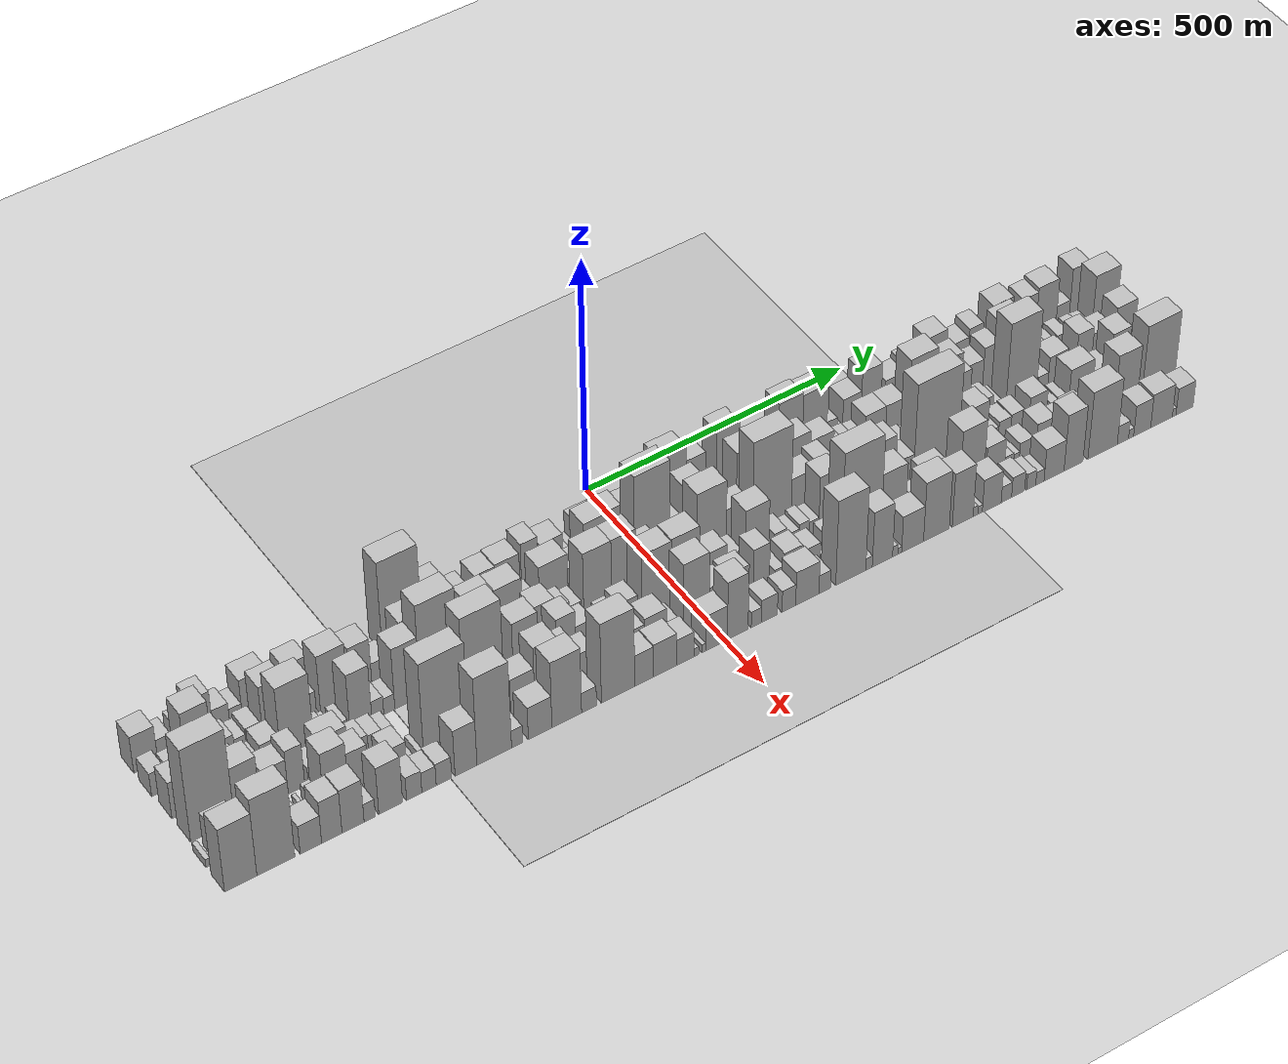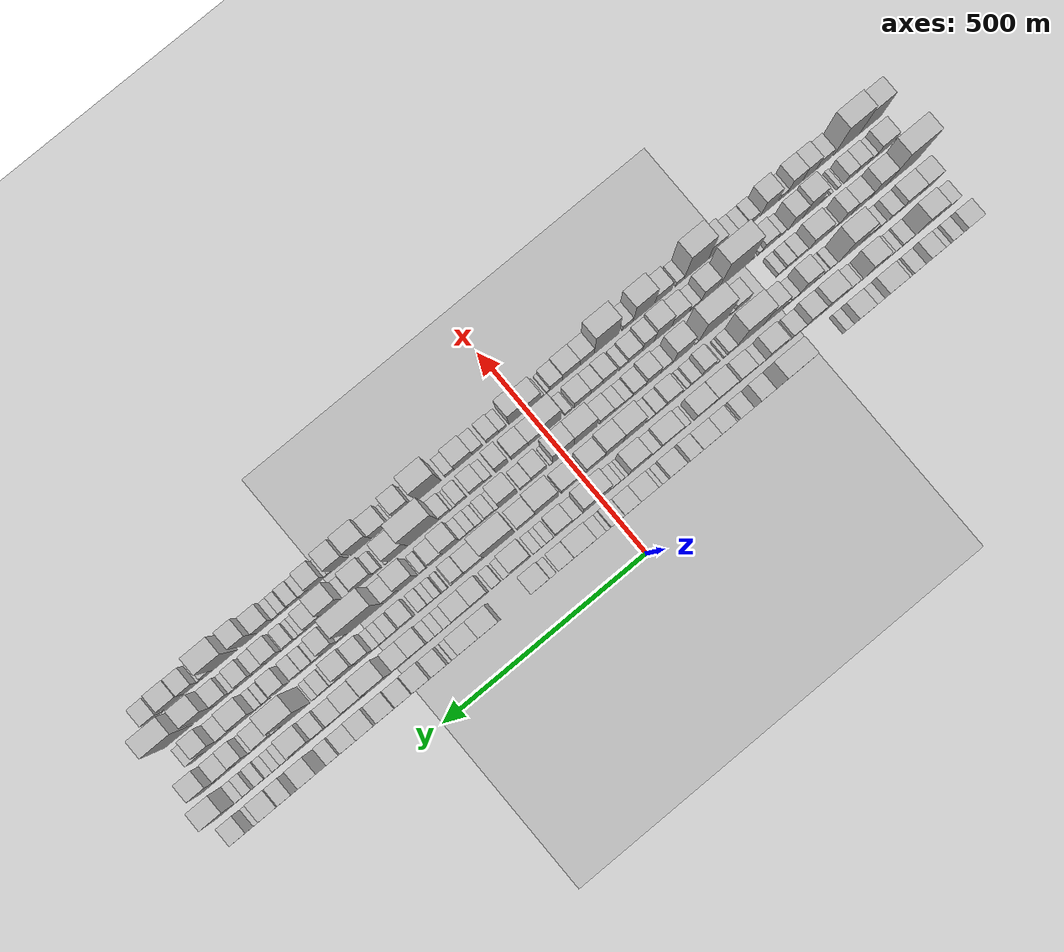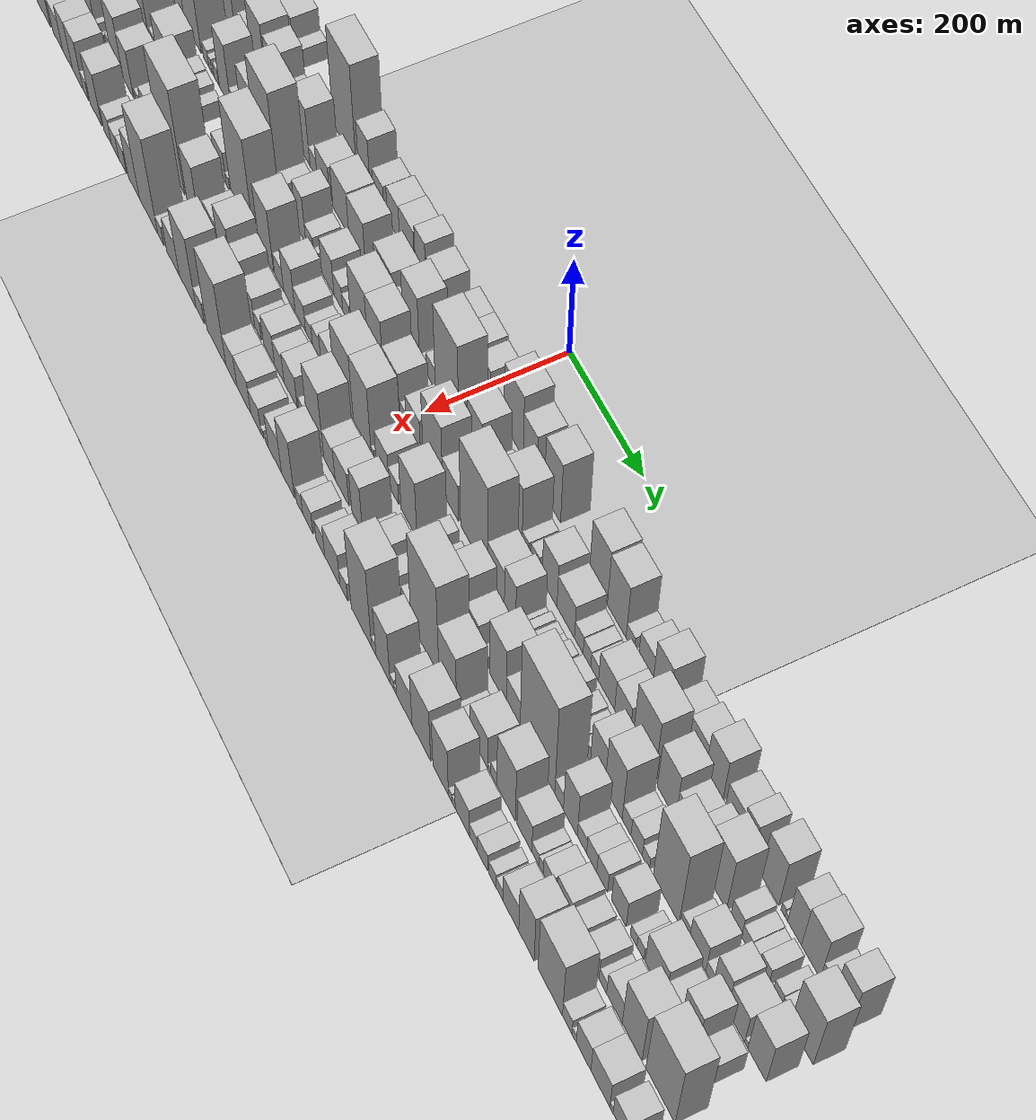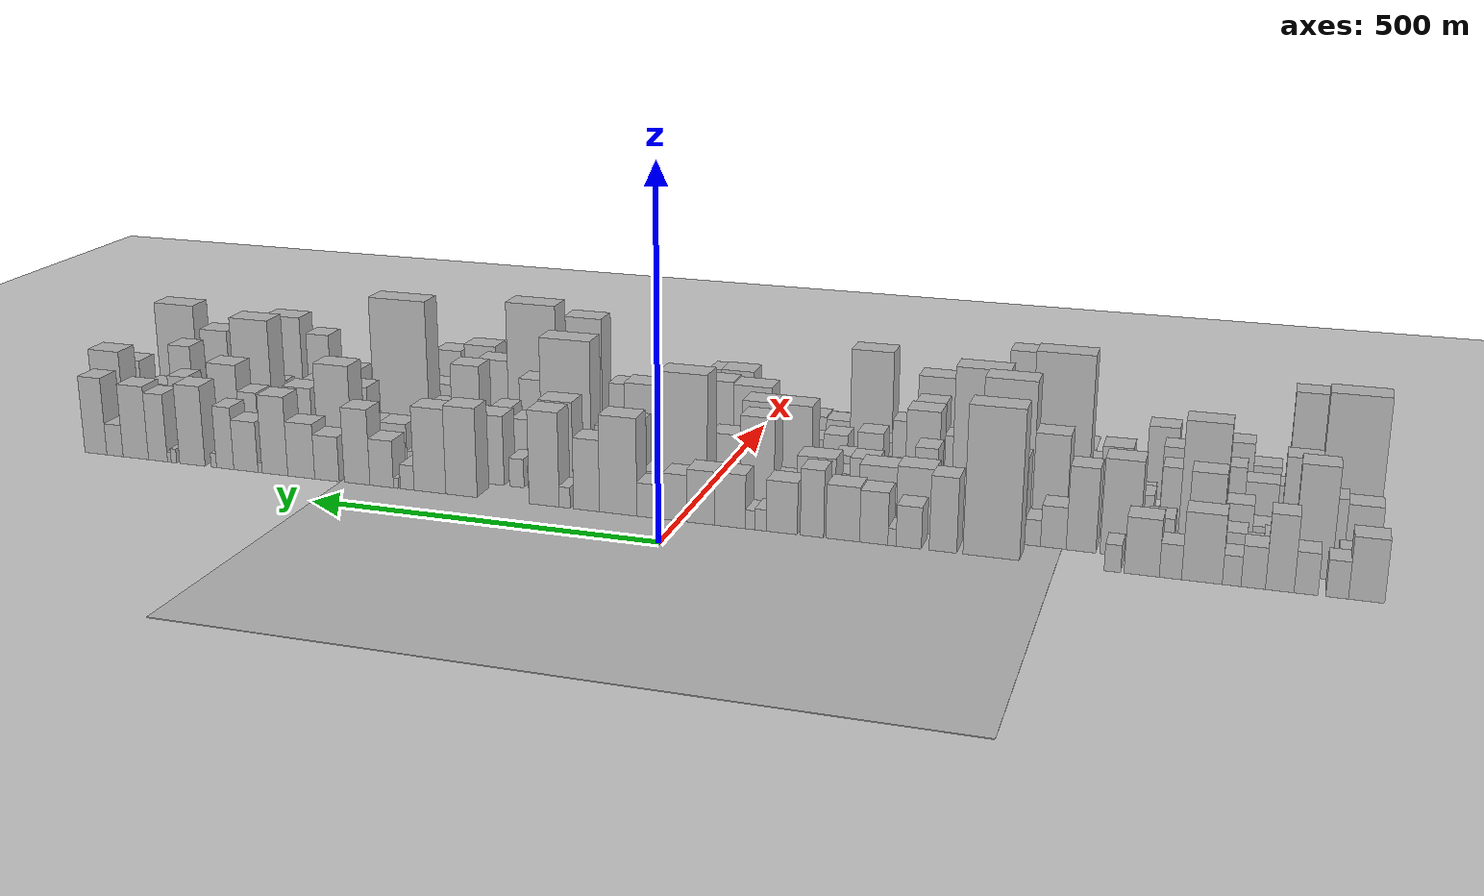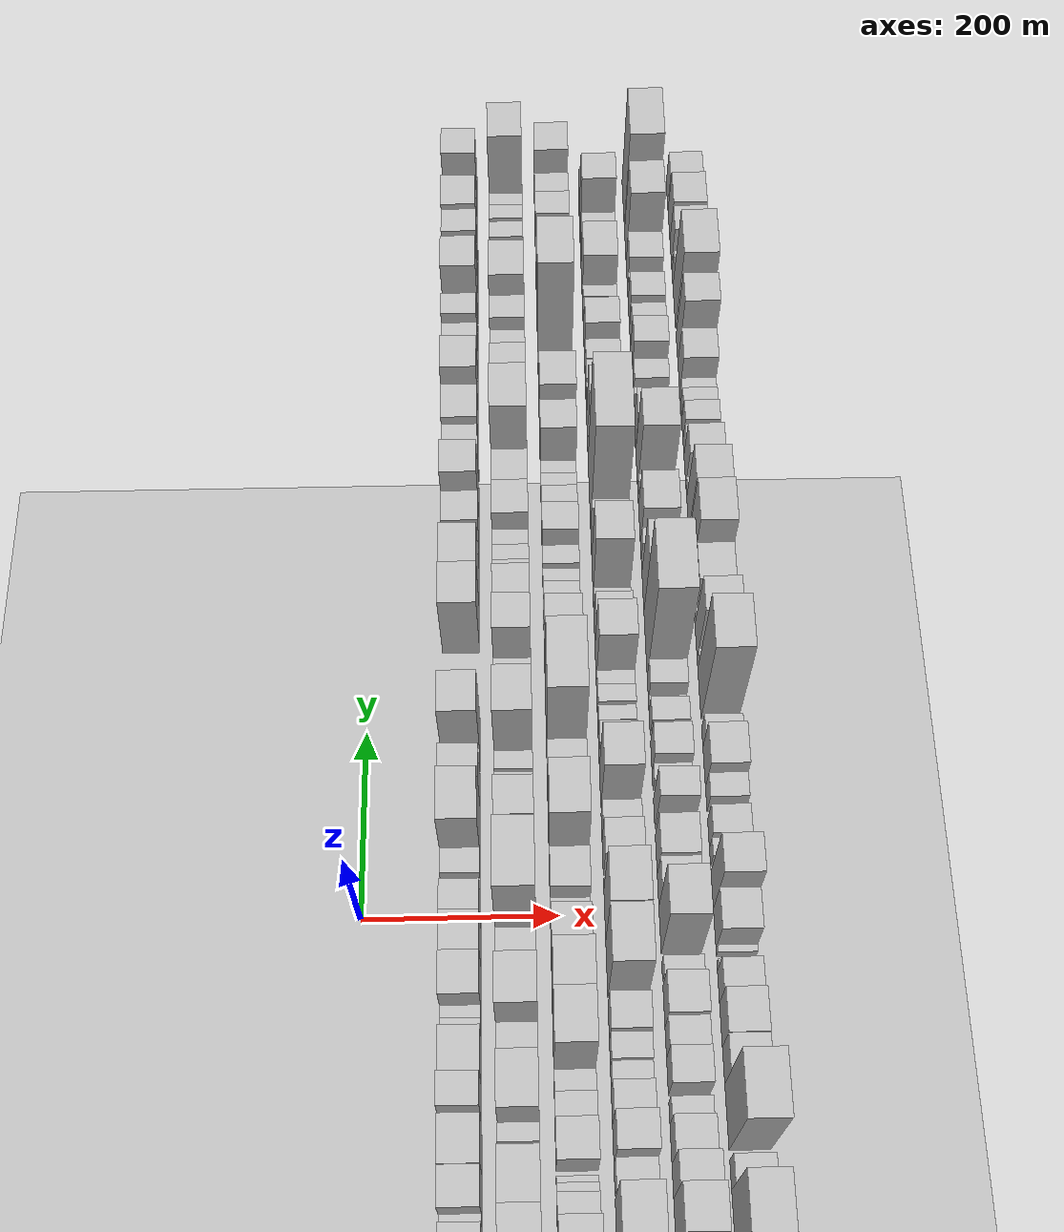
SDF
<?xml version="1.0" encoding="utf-8"?>

<sdf version="1.6">

   <world name="default">

      <gui fullscreen="0">

         <camera name="user_camera">

            <pose>-15 0 4.57585 0 0 0</pose>

            <view_controller>orbit</view_controller>

         </camera>

      </gui>

      <scene>

         <sky>

           <clouds>

             <speed>12</speed>

           </clouds>

         </sky>

         <ambient>0.4 0.4 0.4 1</ambient>

         <background>0.7 0.7 0.7 1</background>

         <shadows>1</shadows>

      </scene>

      <gravity>0 0 -9.8066</gravity>

      <magnetic_field>6e-06 2.3e-05 -4.2e-05</magnetic_field>

      <physics default="0" name="default_physics" type="ode">

         <ode>

            <solver>

               <type>quick</type>

               <iters>10</iters>

               <sor>1.0</sor>

               <use_dynamic_moi_rescaling>0</use_dynamic_moi_rescaling>

            </solver>

            <constraints>

               <cfm>0</cfm>

               <erp>0.2</erp>

               <contact_max_correcting_vel>100</contact_max_correcting_vel>

               <contact_surface_layer>0.001</contact_surface_layer>

            </constraints>

         </ode>

         <max_step_size>0.004</max_step_size>

         <real_time_factor>1</real_time_factor>

         <real_time_update_rate>250</real_time_update_rate>

      </physics>

      <light name="sun" type="directional">

         <cast_shadows>1</cast_shadows>

         <pose>0 0 10 0 0 0</pose>

         <diffuse>0.8 0.8 0.8 1</diffuse>

         <specular>0.2 0.2 0.2 1</specular>

         <attenuation>

            <range>1000</range>

            <constant>0.9</constant>

            <linear>0.01</linear>

            <quadratic>0.001</quadratic>

         </attenuation>

         <direction>-0.5 0.1 -0.9</direction>

      </light>

      <include>

         <name>ground_plane_1</name>

         <uri>model://HANNAS_ground_plane</uri>

         <pose>0 0 0  0 0 0</pose>

      </include>

      <include>

         <name>ground_plane_2</name>

         <uri>model://HANNAS_ground_plane</uri>

         <pose>100 0 0  0 0 0</pose>

      </include>

      <model name="building_1">

         <static>1</static>

         <pose frame="">100.0000 -869.3339 0 0.000000 0.000000 0.000000</pose>

         <link name="link">

            <pose frame="">0 0 40.50 0 0 0</pose>

            <collision name="collision">

               <geometry>

                  <box>

                     <size>40.0000 41.3322 81.0000</size>

                  </box>

               </geometry>

               <max_contacts>10</max_contacts>

               <surface>

                  <contact>

                     <ode/>

                  </contact>

                  <bounce/>

                  <friction>

                     <torsional>

                        <ode/>

                     </torsional>

                     <ode/>

                  </friction>

               </surface>

            </collision>

            <visual name="visual">

               <cast_shadows>0</cast_shadows>

               <geometry>

                  <box>

                     <size>40.0000 41.3322 81.0000</size>

                  </box>

               </geometry>

               <material>

                  <script>

                     <uri>model://HANNAS_wall/materials/scripts</uri>

                     <uri>model://HANNAS_wall/materials/textures</uri>

                     <name>vrc/HANNAS_wall</name>

                  </script>

               </material>

            </visual>

            <self_collide>0</self_collide>

            <enable_wind>0</enable_wind>

            <kinematic>0</kinematic>

         </link>

      </model>

      <model name="building_2">

         <static>1</static>

         <pose frame="">100.0000 -835.6946 0 0.000000 0.000000 0.000000</pose>

         <link name="link">

            <pose frame="">0 0 24.00 0 0 0</pose>

            <collision name="collision">

               <geometry>

                  <box>

                     <size>40.0000 25.9463 48.0000</size>

                  </box>

               </geometry>

               <max_contacts>10</max_contacts>

               <surface>

                  <contact>

                     <ode/>

                  </contact>

                  <bounce/>

                  <friction>

                     <torsional>

                        <ode/>

                     </torsional>

                     <ode/>

                  </friction>

               </surface>

            </collision>

            <visual name="visual">

               <cast_shadows>0</cast_shadows>

               <geometry>

                  <box>

                     <size>40.0000 25.9463 48.0000</size>

                  </box>

               </geometry>

               <material>

                  <script>

                     <uri>model://HANNAS_wall/materials/scripts</uri>

                     <uri>model://HANNAS_wall/materials/textures</uri>

                     <name>vrc/HANNAS_wall</name>

                  </script>

               </material>

            </visual>

            <self_collide>0</self_collide>

            <enable_wind>0</enable_wind>

            <kinematic>0</kinematic>

         </link>

      </model>

      <model name="building_3">

         <static>1</static>

         <pose frame="">100.0000 -799.8474 0 0.000000 0.000000 0.000000</pose>

         <link name="link">

            <pose frame="">0 0 27.00 0 0 0</pose>

            <collision name="collision">

               <geometry>

                  <box>

                     <size>40.0000 27.7481 54.0000</size>

                  </box>

               </geometry>

               <max_contacts>10</max_contacts>

               <surface>

                  <contact>

                     <ode/>

                  </contact>

                  <bounce/>

                  <friction>

                     <torsional>

                        <ode/>

                     </torsional>

                     <ode/>

                  </friction>

               </surface>

            </collision>

            <visual name="visual">

               <cast_shadows>0</cast_shadows>

               <geometry>

                  <box>

                     <size>40.0000 27.7481 54.0000</size>

                  </box>

               </geometry>

               <material>

                  <script>

                     <uri>model://HANNAS_wall/materials/scripts</uri>

                     <uri>model://HANNAS_wall/materials/textures</uri>

                     <name>vrc/HANNAS_wall</name>

                  </script>

               </material>

            </visual>

            <self_collide>0</self_collide>

            <enable_wind>0</enable_wind>

            <kinematic>0</kinematic>

         </link>

      </model>

      <model name="building_4">

         <static>1</static>

         <pose frame="">100.0000 -769.2376 0 0.000000 0.000000 0.000000</pose>

         <link name="link">

            <pose frame="">0 0 49.50 0 0 0</pose>

            <collision name="collision">

               <geometry>

                  <box>

                     <size>40.0000 33.4713 99.0000</size>

                  </box>

               </geometry>

               <max_contacts>10</max_contacts>

               <surface>

                  <contact>

                     <ode/>

                  </contact>

                  <bounce/>

                  <friction>

                     <torsional>

                        <ode/>

                     </torsional>

                     <ode/>

                  </friction>

               </surface>

            </collision>

            <visual name="visual">

               <cast_shadows>0</cast_shadows>

               <geometry>

                  <box>

                     <size>40.0000 33.4713 99.0000</size>

                  </box>

               </geometry>

               <material>

                  <script>

                     <uri>model://HANNAS_wall/materials/scripts</uri>

                     <uri>model://HANNAS_wall/materials/textures</uri>

                     <name>vrc/HANNAS_wall</name>

                  </script>

               </material>

            </visual>

            <self_collide>0</self_collide>

            <enable_wind>0</enable_wind>

            <kinematic>0</kinematic>

         </link>

      </model>

      <model name="building_5">

         <static>1</static>

         <pose frame="">100.0000 -738.1177 0 0.000000 0.000000 0.000000</pose>

         <link name="link">

            <pose frame="">0 0 27.00 0 0 0</pose>

            <collision name="collision">

               <geometry>

                  <box>

                     <size>40.0000 28.7686 54.0000</size>

                  </box>

               </geometry>

               <max_contacts>10</max_contacts>

               <surface>

                  <contact>

                     <ode/>

                  </contact>

                  <bounce/>

                  <friction>

                     <torsional>

                        <ode/>

                     </torsional>

                     <ode/>

                  </friction>

               </surface>

            </collision>

            <visual name="visual">

               <cast_shadows>0</cast_shadows>

               <geometry>

                  <box>

                     <size>40.0000 28.7686 54.0000</size>

                  </box>

               </geometry>

               <material>

                  <script>

                     <uri>model://HANNAS_wall/materials/scripts</uri>

                     <uri>model://HANNAS_wall/materials/textures</uri>

                     <name>vrc/HANNAS_wall</name>

                  </script>

               </material>

            </visual>

            <self_collide>0</self_collide>

            <enable_wind>0</enable_wind>

            <kinematic>0</kinematic>

         </link>

      </model>

      <model name="building_6">

         <static>1</static>

         <pose frame="">100.0000 -712.6709 0 0.000000 0.000000 0.000000</pose>

         <link name="link">

            <pose frame="">0 0 19.50 0 0 0</pose>

            <collision name="collision">

               <geometry>

                  <box>

                     <size>40.0000 22.1250 39.0000</size>

                  </box>

               </geometry>

               <max_contacts>10</max_contacts>

               <surface>

                  <contact>

                     <ode/>

                  </contact>

                  <bounce/>

                  <friction>

                     <torsional>

                        <ode/>

                     </torsional>

                     <ode/>

                  </friction>

               </surface>

            </collision>

            <visual name="visual">

               <cast_shadows>0</cast_shadows>

               <geometry>

                  <box>

                     <size>40.0000 22.1250 39.0000</size>

                  </box>

               </geometry>

               <material>

                  <script>

                     <uri>model://HANNAS_wall/materials/scripts</uri>

                     <uri>model://HANNAS_wall/materials/textures</uri>

                     <name>vrc/HANNAS_wall</name>

                  </script>

               </material>

            </visual>

            <self_collide>0</self_collide>

            <enable_wind>0</enable_wind>

            <kinematic>0</kinematic>

         </link>

      </model>

      <model name="building_7">

         <static>1</static>

         <pose frame="">100.0000 -677.2731 0 0.000000 0.000000 0.000000</pose>

         <link name="link">

            <pose frame="">0 0 45.00 0 0 0</pose>

            <collision name="collision">

               <geometry>

                  <box>

                     <size>40.0000 48.6707 90.0000</size>

                  </box>

               </geometry>

               <max_contacts>10</max_contacts>

               <surface>

                  <contact>

                     <ode/>

                  </contact>

                  <bounce/>

                  <friction>

                     <torsional>

                        <ode/>

                     </torsional>

                     <ode/>

                  </friction>

               </surface>

            </collision>

            <visual name="visual">

               <cast_shadows>0</cast_shadows>

               <geometry>

                  <box>

                     <size>40.0000 48.6707 90.0000</size>

                  </box>

               </geometry>

               <material>

                  <script>

                     <uri>model://HANNAS_wall/materials/scripts</uri>

                     <uri>model://HANNAS_wall/materials/textures</uri>

                     <name>vrc/HANNAS_wall</name>

                  </script>

               </material>

            </visual>

            <self_collide>0</self_collide>

            <enable_wind>0</enable_wind>

            <kinematic>0</kinematic>

         </link>

      </model>

      <model name="building_8">

         <static>1</static>

         <pose frame="">100.0000 -639.5324 0 0.000000 0.000000 0.000000</pose>

         <link name="link">

            <pose frame="">0 0 22.50 0 0 0</pose>

            <collision name="collision">

               <geometry>

                  <box>

                     <size>40.0000 26.8107 45.0000</size>

                  </box>

               </geometry>

               <max_contacts>10</max_contacts>

               <surface>

                  <contact>

                     <ode/>

                  </contact>

                  <bounce/>

                  <friction>

                     <torsional>

                        <ode/>

                     </torsional>

                     <ode/>

                  </friction>

               </surface>

            </collision>

            <visual name="visual">

               <cast_shadows>0</cast_shadows>

               <geometry>

                  <box>

                     <size>40.0000 26.8107 45.0000</size>

                  </box>

               </geometry>

               <material>

                  <script>

                     <uri>model://HANNAS_wall/materials/scripts</uri>

                     <uri>model://HANNAS_wall/materials/textures</uri>

                     <name>vrc/HANNAS_wall</name>

                  </script>

               </material>

            </visual>

            <self_collide>0</self_collide>

            <enable_wind>0</enable_wind>

            <kinematic>0</kinematic>

         </link>

      </model>

      <model name="building_9">

         <static>1</static>

         <pose frame="">100.0000 -604.7382 0 0.000000 0.000000 0.000000</pose>

         <link name="link">

            <pose frame="">0 0 37.50 0 0 0</pose>

            <collision name="collision">

               <geometry>

                  <box>

                     <size>40.0000 42.7776 75.0000</size>

                  </box>

               </geometry>

               <max_contacts>10</max_contacts>

               <surface>

                  <contact>

                     <ode/>

                  </contact>

                  <bounce/>

                  <friction>

                     <torsional>

                        <ode/>

                     </torsional>

                     <ode/>

                  </friction>

               </surface>

            </collision>

            <visual name="visual">

               <cast_shadows>0</cast_shadows>

               <geometry>

                  <box>

                     <size>40.0000 42.7776 75.0000</size>

                  </box>

               </geometry>

               <material>

                  <script>

                     <uri>model://HANNAS_wall/materials/scripts</uri>

                     <uri>model://HANNAS_wall/materials/textures</uri>

                     <name>vrc/HANNAS_wall</name>

                  </script>

               </material>

            </visual>

            <self_collide>0</self_collide>

            <enable_wind>0</enable_wind>

            <kinematic>0</kinematic>

         </link>

      </model>

      <model name="building_10">

         <static>1</static>

         <pose frame="">100.0000 -569.1317 0 0.000000 0.000000 0.000000</pose>

         <link name="link">

            <pose frame="">0 0 18.00 0 0 0</pose>

            <collision name="collision">

               <geometry>

                  <box>

                     <size>40.0000 20.4354 36.0000</size>

                  </box>

               </geometry>

               <max_contacts>10</max_contacts>

               <surface>

                  <contact>

                     <ode/>

                  </contact>

                  <bounce/>

                  <friction>

                     <torsional>

                        <ode/>

                     </torsional>

                     <ode/>

                  </friction>

               </surface>

            </collision>

            <visual name="visual">

               <cast_shadows>0</cast_shadows>

               <geometry>

                  <box>

                     <size>40.0000 20.4354 36.0000</size>

                  </box>

               </geometry>

               <material>

                  <script>

                     <uri>model://HANNAS_wall/materials/scripts</uri>

                     <uri>model://HANNAS_wall/materials/textures</uri>

                     <name>vrc/HANNAS_wall</name>

                  </script>

               </material>

            </visual>

            <self_collide>0</self_collide>

            <enable_wind>0</enable_wind>

            <kinematic>0</kinematic>

         </link>

      </model>

      <model name="building_11">

         <static>1</static>

         <pose frame="">100.0000 -417.7875 0 0.000000 0.000000 0.000000</pose>

         <link name="link">

            <pose frame="">0 0 100.50 0 0 0</pose>

            <collision name="collision">

               <geometry>

                  <box>

                     <size>40.0000 72.0844 201.0000</size>

                  </box>

               </geometry>

               <max_contacts>10</max_contacts>

               <surface>

                  <contact>

                     <ode/>

                  </contact>

                  <bounce/>

                  <friction>

                     <torsional>

                        <ode/>

                     </torsional>

                     <ode/>

                  </friction>

               </surface>

            </collision>

            <visual name="visual">

               <cast_shadows>0</cast_shadows>

               <geometry>

                  <box>

                     <size>40.0000 72.0844 201.0000</size>

                  </box>

               </geometry>

               <material>

                  <script>

                     <uri>model://HANNAS_wall/materials/scripts</uri>

                     <uri>model://HANNAS_wall/materials/textures</uri>

                     <name>vrc/HANNAS_wall</name>

                  </script>

               </material>

            </visual>

            <self_collide>0</self_collide>

            <enable_wind>0</enable_wind>

            <kinematic>0</kinematic>

         </link>

      </model>

      <model name="building_12">

         <static>1</static>

         <pose frame="">100.0000 -355.9250 0 0.000000 0.000000 0.000000</pose>

         <link name="link">

            <pose frame="">0 0 51.00 0 0 0</pose>

            <collision name="collision">

               <geometry>

                  <box>

                     <size>40.0000 35.6405 102.0000</size>

                  </box>

               </geometry>

               <max_contacts>10</max_contacts>

               <surface>

                  <contact>

                     <ode/>

                  </contact>

                  <bounce/>

                  <friction>

                     <torsional>

                        <ode/>

                     </torsional>

                     <ode/>

                  </friction>

               </surface>

            </collision>

            <visual name="visual">

               <cast_shadows>0</cast_shadows>

               <geometry>

                  <box>

                     <size>40.0000 35.6405 102.0000</size>

                  </box>

               </geometry>

               <material>

                  <script>

                     <uri>model://HANNAS_wall/materials/scripts</uri>

                     <uri>model://HANNAS_wall/materials/textures</uri>

                     <name>vrc/HANNAS_wall</name>

                  </script>

               </material>

            </visual>

            <self_collide>0</self_collide>

            <enable_wind>0</enable_wind>

            <kinematic>0</kinematic>

         </link>

      </model>

      <model name="building_13">

         <static>1</static>

         <pose frame="">100.0000 -311.5917 0 0.000000 0.000000 0.000000</pose>

         <link name="link">

            <pose frame="">0 0 28.50 0 0 0</pose>

            <collision name="collision">

               <geometry>

                  <box>

                     <size>40.0000 33.0261 57.0000</size>

                  </box>

               </geometry>

               <max_contacts>10</max_contacts>

               <surface>

                  <contact>

                     <ode/>

                  </contact>

                  <bounce/>

                  <friction>

                     <torsional>

                        <ode/>

                     </torsional>

                     <ode/>

                  </friction>

               </surface>

            </collision>

            <visual name="visual">

               <cast_shadows>0</cast_shadows>

               <geometry>

                  <box>

                     <size>40.0000 33.0261 57.0000</size>

                  </box>

               </geometry>

               <material>

                  <script>

                     <uri>model://HANNAS_wall/materials/scripts</uri>

                     <uri>model://HANNAS_wall/materials/textures</uri>

                     <name>vrc/HANNAS_wall</name>

                  </script>

               </material>

            </visual>

            <self_collide>0</self_collide>

            <enable_wind>0</enable_wind>

            <kinematic>0</kinematic>

         </link>

      </model>

      <model name="building_14">

         <static>1</static>

         <pose frame="">100.0000 -289.7027 0 0.000000 0.000000 0.000000</pose>

         <link name="link">

            <pose frame="">0 0 12.00 0 0 0</pose>

            <collision name="collision">

               <geometry>

                  <box>

                     <size>40.0000 10.7521 24.0000</size>

                  </box>

               </geometry>

               <max_contacts>10</max_contacts>

               <surface>

                  <contact>

                     <ode/>

                  </contact>

                  <bounce/>

                  <friction>

                     <torsional>

                        <ode/>

                     </torsional>

                     <ode/>

                  </friction>

               </surface>

            </collision>

            <visual name="visual">

               <cast_shadows>0</cast_shadows>

               <geometry>

                  <box>

                     <size>40.0000 10.7521 24.0000</size>

                  </box>

               </geometry>

               <material>

                  <script>

                     <uri>model://HANNAS_wall/materials/scripts</uri>

                     <uri>model://HANNAS_wall/materials/textures</uri>

                     <name>vrc/HANNAS_wall</name>

                  </script>

               </material>

            </visual>

            <self_collide>0</self_collide>

            <enable_wind>0</enable_wind>

            <kinematic>0</kinematic>

         </link>

      </model>

      <model name="building_15">

         <static>1</static>

         <pose frame="">100.0000 -265.7249 0 0.000000 0.000000 0.000000</pose>

         <link name="link">

            <pose frame="">0 0 36.00 0 0 0</pose>

            <collision name="collision">

               <geometry>

                  <box>

                     <size>40.0000 37.2034 72.0000</size>

                  </box>

               </geometry>

               <max_contacts>10</max_contacts>

               <surface>

                  <contact>

                     <ode/>

                  </contact>

                  <bounce/>

                  <friction>

                     <torsional>

                        <ode/>

                     </torsional>

                     <ode/>

                  </friction>

               </surface>

            </collision>

            <visual name="visual">

               <cast_shadows>0</cast_shadows>

               <geometry>

                  <box>

                     <size>40.0000 37.2034 72.0000</size>

                  </box>

               </geometry>

               <material>

                  <script>

                     <uri>model://HANNAS_wall/materials/scripts</uri>

                     <uri>model://HANNAS_wall/materials/textures</uri>

                     <name>vrc/HANNAS_wall</name>

                  </script>

               </material>

            </visual>

            <self_collide>0</self_collide>

            <enable_wind>0</enable_wind>

            <kinematic>0</kinematic>

         </link>

      </model>

      <model name="building_16">

         <static>1</static>

         <pose frame="">100.0000 -224.6815 0 0.000000 0.000000 0.000000</pose>

         <link name="link">

            <pose frame="">0 0 37.50 0 0 0</pose>

            <collision name="collision">

               <geometry>

                  <box>

                     <size>40.0000 44.8836 75.0000</size>

                  </box>

               </geometry>

               <max_contacts>10</max_contacts>

               <surface>

                  <contact>

                     <ode/>

                  </contact>

                  <bounce/>

                  <friction>

                     <torsional>

                        <ode/>

                     </torsional>

                     <ode/>

                  </friction>

               </surface>

            </collision>

            <visual name="visual">

               <cast_shadows>0</cast_shadows>

               <geometry>

                  <box>

                     <size>40.0000 44.8836 75.0000</size>

                  </box>

               </geometry>

               <material>

                  <script>

                     <uri>model://HANNAS_wall/materials/scripts</uri>

                     <uri>model://HANNAS_wall/materials/textures</uri>

                     <name>vrc/HANNAS_wall</name>

                  </script>

               </material>

            </visual>

            <self_collide>0</self_collide>

            <enable_wind>0</enable_wind>

            <kinematic>0</kinematic>

         </link>

      </model>

      <model name="building_17">

         <static>1</static>

         <pose frame="">100.0000 -183.5330 0 0.000000 0.000000 0.000000</pose>

         <link name="link">

            <pose frame="">0 0 46.50 0 0 0</pose>

            <collision name="collision">

               <geometry>

                  <box>

                     <size>40.0000 31.4134 93.0000</size>

                  </box>

               </geometry>

               <max_contacts>10</max_contacts>

               <surface>

                  <contact>

                     <ode/>

                  </contact>

                  <bounce/>

                  <friction>

                     <torsional>

                        <ode/>

                     </torsional>

                     <ode/>

                  </friction>

               </surface>

            </collision>

            <visual name="visual">

               <cast_shadows>0</cast_shadows>

               <geometry>

                  <box>

                     <size>40.0000 31.4134 93.0000</size>

                  </box>

               </geometry>

               <material>

                  <script>

                     <uri>model://HANNAS_wall/materials/scripts</uri>

                     <uri>model://HANNAS_wall/materials/textures</uri>

                     <name>vrc/HANNAS_wall</name>

                  </script>

               </material>

            </visual>

            <self_collide>0</self_collide>

            <enable_wind>0</enable_wind>

            <kinematic>0</kinematic>

         </link>

      </model>

      <model name="building_18">

         <static>1</static>

         <pose frame="">100.0000 -142.7192 0 0.000000 0.000000 0.000000</pose>

         <link name="link">

            <pose frame="">0 0 36.00 0 0 0</pose>

            <collision name="collision">

               <geometry>

                  <box>

                     <size>40.0000 42.2141 72.0000</size>

                  </box>

               </geometry>

               <max_contacts>10</max_contacts>

               <surface>

                  <contact>

                     <ode/>

                  </contact>

                  <bounce/>

                  <friction>

                     <torsional>

                        <ode/>

                     </torsional>

                     <ode/>

                  </friction>

               </surface>

            </collision>

            <visual name="visual">

               <cast_shadows>0</cast_shadows>

               <geometry>

                  <box>

                     <size>40.0000 42.2141 72.0000</size>

                  </box>

               </geometry>

               <material>

                  <script>

                     <uri>model://HANNAS_wall/materials/scripts</uri>

                     <uri>model://HANNAS_wall/materials/textures</uri>

                     <name>vrc/HANNAS_wall</name>

                  </script>

               </material>

            </visual>

            <self_collide>0</self_collide>

            <enable_wind>0</enable_wind>

            <kinematic>0</kinematic>

         </link>

      </model>

      <model name="building_19">

         <static>1</static>

         <pose frame="">100.0000 -113.9480 0 0.000000 0.000000 0.000000</pose>

         <link name="link">

            <pose frame="">0 0 15.00 0 0 0</pose>

            <collision name="collision">

               <geometry>

                  <box>

                     <size>40.0000 15.3283 30.0000</size>

                  </box>

               </geometry>

               <max_contacts>10</max_contacts>

               <surface>

                  <contact>

                     <ode/>

                  </contact>

                  <bounce/>

                  <friction>

                     <torsional>

                        <ode/>

                     </torsional>

                     <ode/>

                  </friction>

               </surface>

            </collision>

            <visual name="visual">

               <cast_shadows>0</cast_shadows>

               <geometry>

                  <box>

                     <size>40.0000 15.3283 30.0000</size>

                  </box>

               </geometry>

               <material>

                  <script>

                     <uri>model://HANNAS_wall/materials/scripts</uri>

                     <uri>model://HANNAS_wall/materials/textures</uri>

                     <name>vrc/HANNAS_wall</name>

                  </script>

               </material>

            </visual>

            <self_collide>0</self_collide>

            <enable_wind>0</enable_wind>

            <kinematic>0</kinematic>

         </link>

      </model>

      <model name="building_20">

         <static>1</static>

         <pose frame="">100.0000 -99.8096 0 0.000000 0.000000 0.000000</pose>

         <link name="link">

            <pose frame="">0 0 13.50 0 0 0</pose>

            <collision name="collision">

               <geometry>

                  <box>

                     <size>40.0000 12.9486 27.0000</size>

                  </box>

               </geometry>

               <max_contacts>10</max_contacts>

               <surface>

                  <contact>

                     <ode/>

                  </contact>

                  <bounce/>

                  <friction>

                     <torsional>

                        <ode/>

                     </torsional>

                     <ode/>

                  </friction>

               </surface>

            </collision>

            <visual name="visual">

               <cast_shadows>0</cast_shadows>

               <geometry>

                  <box>

                     <size>40.0000 12.9486 27.0000</size>

                  </box>

               </geometry>

               <material>

                  <script>

                     <uri>model://HANNAS_wall/materials/scripts</uri>

                     <uri>model://HANNAS_wall/materials/textures</uri>

                     <name>vrc/HANNAS_wall</name>

                  </script>

               </material>

            </visual>

            <self_collide>0</self_collide>

            <enable_wind>0</enable_wind>

            <kinematic>0</kinematic>

         </link>

      </model>

      <model name="building_21">

         <static>1</static>

         <pose frame="">100.0000 -72.1973 0 0.000000 0.000000 0.000000</pose>

         <link name="link">

            <pose frame="">0 0 37.50 0 0 0</pose>

            <collision name="collision">

               <geometry>

                  <box>

                     <size>40.0000 42.2760 75.0000</size>

                  </box>

               </geometry>

               <max_contacts>10</max_contacts>

               <surface>

                  <contact>

                     <ode/>

                  </contact>

                  <bounce/>

                  <friction>

                     <torsional>

                        <ode/>

                     </torsional>

                     <ode/>

                  </friction>

               </surface>

            </collision>

            <visual name="visual">

               <cast_shadows>0</cast_shadows>

               <geometry>

                  <box>

                     <size>40.0000 42.2760 75.0000</size>

                  </box>

               </geometry>

               <material>

                  <script>

                     <uri>model://HANNAS_wall/materials/scripts</uri>

                     <uri>model://HANNAS_wall/materials/textures</uri>

                     <name>vrc/HANNAS_wall</name>

                  </script>

               </material>

            </visual>

            <self_collide>0</self_collide>

            <enable_wind>0</enable_wind>

            <kinematic>0</kinematic>

         </link>

      </model>

      <model name="building_22">

         <static>1</static>

         <pose frame="">100.0000 -31.4628 0 0.000000 0.000000 0.000000</pose>

         <link name="link">

            <pose frame="">0 0 37.50 0 0 0</pose>

            <collision name="collision">

               <geometry>

                  <box>

                     <size>40.0000 39.1929 75.0000</size>

                  </box>

               </geometry>

               <max_contacts>10</max_contacts>

               <surface>

                  <contact>

                     <ode/>

                  </contact>

                  <bounce/>

                  <friction>

                     <torsional>

                        <ode/>

                     </torsional>

                     <ode/>

                  </friction>

               </surface>

            </collision>

            <visual name="visual">

               <cast_shadows>0</cast_shadows>

               <geometry>

                  <box>

                     <size>40.0000 39.1929 75.0000</size>

                  </box>

               </geometry>

               <material>

                  <script>

                     <uri>model://HANNAS_wall/materials/scripts</uri>

                     <uri>model://HANNAS_wall/materials/textures</uri>

                     <name>vrc/HANNAS_wall</name>

                  </script>

               </material>

            </visual>

            <self_collide>0</self_collide>

            <enable_wind>0</enable_wind>

            <kinematic>0</kinematic>

         </link>

      </model>

      <model name="building_23">

         <static>1</static>

         <pose frame="">100.0000 4.7394 0 0.000000 0.000000 0.000000</pose>

         <link name="link">

            <pose frame="">0 0 33.00 0 0 0</pose>

            <collision name="collision">

               <geometry>

                  <box>

                     <size>40.0000 33.2117 66.0000</size>

                  </box>

               </geometry>

               <max_contacts>10</max_contacts>

               <surface>

                  <contact>

                     <ode/>

                  </contact>

                  <bounce/>

                  <friction>

                     <torsional>

                        <ode/>

                     </torsional>

                     <ode/>

                  </friction>

               </surface>

            </collision>

            <visual name="visual">

               <cast_shadows>0</cast_shadows>

               <geometry>

                  <box>

                     <size>40.0000 33.2117 66.0000</size>

                  </box>

               </geometry>

               <material>

                  <script>

                     <uri>model://HANNAS_wall/materials/scripts</uri>

                     <uri>model://HANNAS_wall/materials/textures</uri>

                     <name>vrc/HANNAS_wall</name>

                  </script>

               </material>

            </visual>

            <self_collide>0</self_collide>

            <enable_wind>0</enable_wind>

            <kinematic>0</kinematic>

         </link>

      </model>

      <model name="building_24">

         <static>1</static>

         <pose frame="">100.0000 26.8860 0 0.000000 0.000000 0.000000</pose>

         <link name="link">

            <pose frame="">0 0 13.50 0 0 0</pose>

            <collision name="collision">

               <geometry>

                  <box>

                     <size>40.0000 11.0816 27.0000</size>

                  </box>

               </geometry>

               <max_contacts>10</max_contacts>

               <surface>

                  <contact>

                     <ode/>

                  </contact>

                  <bounce/>

                  <friction>

                     <torsional>

                        <ode/>

                     </torsional>

                     <ode/>

                  </friction>

               </surface>

            </collision>

            <visual name="visual">

               <cast_shadows>0</cast_shadows>

               <geometry>

                  <box>

                     <size>40.0000 11.0816 27.0000</size>

                  </box>

               </geometry>

               <material>

                  <script>

                     <uri>model://HANNAS_wall/materials/scripts</uri>

                     <uri>model://HANNAS_wall/materials/textures</uri>

                     <name>vrc/HANNAS_wall</name>

                  </script>

               </material>

            </visual>

            <self_collide>0</self_collide>

            <enable_wind>0</enable_wind>

            <kinematic>0</kinematic>

         </link>

      </model>

      <model name="building_25">

         <static>1</static>

         <pose frame="">100.0000 45.4038 0 0.000000 0.000000 0.000000</pose>

         <link name="link">

            <pose frame="">0 0 24.00 0 0 0</pose>

            <collision name="collision">

               <geometry>

                  <box>

                     <size>40.0000 25.9538 48.0000</size>

                  </box>

               </geometry>

               <max_contacts>10</max_contacts>

               <surface>

                  <contact>

                     <ode/>

                  </contact>

                  <bounce/>

                  <friction>

                     <torsional>

                        <ode/>

                     </torsional>

                     <ode/>

                  </friction>

               </surface>

            </collision>

            <visual name="visual">

               <cast_shadows>0</cast_shadows>

               <geometry>

                  <box>

                     <size>40.0000 25.9538 48.0000</size>

                  </box>

               </geometry>

               <material>

                  <script>

                     <uri>model://HANNAS_wall/materials/scripts</uri>

                     <uri>model://HANNAS_wall/materials/textures</uri>

                     <name>vrc/HANNAS_wall</name>

                  </script>

               </material>

            </visual>

            <self_collide>0</self_collide>

            <enable_wind>0</enable_wind>

            <kinematic>0</kinematic>

         </link>

      </model>

      <model name="building_26">

         <static>1</static>

         <pose frame="">100.0000 85.0655 0 0.000000 0.000000 0.000000</pose>

         <link name="link">

            <pose frame="">0 0 69.00 0 0 0</pose>

            <collision name="collision">

               <geometry>

                  <box>

                     <size>40.0000 53.3696 138.0000</size>

                  </box>

               </geometry>

               <max_contacts>10</max_contacts>

               <surface>

                  <contact>

                     <ode/>

                  </contact>

                  <bounce/>

                  <friction>

                     <torsional>

                        <ode/>

                     </torsional>

                     <ode/>

                  </friction>

               </surface>

            </collision>

            <visual name="visual">

               <cast_shadows>0</cast_shadows>

               <geometry>

                  <box>

                     <size>40.0000 53.3696 138.0000</size>

                  </box>

               </geometry>

               <material>

                  <script>

                     <uri>model://HANNAS_wall/materials/scripts</uri>

                     <uri>model://HANNAS_wall/materials/textures</uri>

                     <name>vrc/HANNAS_wall</name>

                  </script>

               </material>

            </visual>

            <self_collide>0</self_collide>

            <enable_wind>0</enable_wind>

            <kinematic>0</kinematic>

         </link>

      </model>

      <model name="building_27">

         <static>1</static>

         <pose frame="">100.0000 130.4153 0 0.000000 0.000000 0.000000</pose>

         <link name="link">

            <pose frame="">0 0 51.00 0 0 0</pose>

            <collision name="collision">

               <geometry>

                  <box>

                     <size>40.0000 37.3301 102.0000</size>

                  </box>

               </geometry>

               <max_contacts>10</max_contacts>

               <surface>

                  <contact>

                     <ode/>

                  </contact>

                  <bounce/>

                  <friction>

                     <torsional>

                        <ode/>

                     </torsional>

                     <ode/>

                  </friction>

               </surface>

            </collision>

            <visual name="visual">

               <cast_shadows>0</cast_shadows>

               <geometry>

                  <box>

                     <size>40.0000 37.3301 102.0000</size>

                  </box>

               </geometry>

               <material>

                  <script>

                     <uri>model://HANNAS_wall/materials/scripts</uri>

                     <uri>model://HANNAS_wall/materials/textures</uri>

                     <name>vrc/HANNAS_wall</name>

                  </script>

               </material>

            </visual>

            <self_collide>0</self_collide>

            <enable_wind>0</enable_wind>

            <kinematic>0</kinematic>

         </link>

      </model>

      <model name="building_28">

         <static>1</static>

         <pose frame="">100.0000 162.0472 0 0.000000 0.000000 0.000000</pose>

         <link name="link">

            <pose frame="">0 0 15.00 0 0 0</pose>

            <collision name="collision">

               <geometry>

                  <box>

                     <size>40.0000 15.9336 30.0000</size>

                  </box>

               </geometry>

               <max_contacts>10</max_contacts>

               <surface>

                  <contact>

                     <ode/>

                  </contact>

                  <bounce/>

                  <friction>

                     <torsional>

                        <ode/>

                     </torsional>

                     <ode/>

                  </friction>

               </surface>

            </collision>

            <visual name="visual">

               <cast_shadows>0</cast_shadows>

               <geometry>

                  <box>

                     <size>40.0000 15.9336 30.0000</size>

                  </box>

               </geometry>

               <material>

                  <script>

                     <uri>model://HANNAS_wall/materials/scripts</uri>

                     <uri>model://HANNAS_wall/materials/textures</uri>

                     <name>vrc/HANNAS_wall</name>

                  </script>

               </material>

            </visual>

            <self_collide>0</self_collide>

            <enable_wind>0</enable_wind>

            <kinematic>0</kinematic>

         </link>

      </model>

      <model name="building_29">

         <static>1</static>

         <pose frame="">100.0000 191.9779 0 0.000000 0.000000 0.000000</pose>

         <link name="link">

            <pose frame="">0 0 67.50 0 0 0</pose>

            <collision name="collision">

               <geometry>

                  <box>

                     <size>40.0000 43.9278 135.0000</size>

                  </box>

               </geometry>

               <max_contacts>10</max_contacts>

               <surface>

                  <contact>

                     <ode/>

                  </contact>

                  <bounce/>

                  <friction>

                     <torsional>

                        <ode/>

                     </torsional>

                     <ode/>

                  </friction>

               </surface>

            </collision>

            <visual name="visual">

               <cast_shadows>0</cast_shadows>

               <geometry>

                  <box>

                     <size>40.0000 43.9278 135.0000</size>

                  </box>

               </geometry>

               <material>

                  <script>

                     <uri>model://HANNAS_wall/materials/scripts</uri>

                     <uri>model://HANNAS_wall/materials/textures</uri>

                     <name>vrc/HANNAS_wall</name>

                  </script>

               </material>

            </visual>

            <self_collide>0</self_collide>

            <enable_wind>0</enable_wind>

            <kinematic>0</kinematic>

         </link>

      </model>

      <model name="building_30">

         <static>1</static>

         <pose frame="">100.0000 314.6319 0 0.000000 0.000000 0.000000</pose>

         <link name="link">

            <pose frame="">0 0 64.50 0 0 0</pose>

            <collision name="collision">

               <geometry>

                  <box>

                     <size>40.0000 47.1267 129.0000</size>

                  </box>

               </geometry>

               <max_contacts>10</max_contacts>

               <surface>

                  <contact>

                     <ode/>

                  </contact>

                  <bounce/>

                  <friction>

                     <torsional>

                        <ode/>

                     </torsional>

                     <ode/>

                  </friction>

               </surface>

            </collision>

            <visual name="visual">

               <cast_shadows>0</cast_shadows>

               <geometry>

                  <box>

                     <size>40.0000 47.1267 129.0000</size>

                  </box>

               </geometry>

               <material>

                  <script>

                     <uri>model://HANNAS_wall/materials/scripts</uri>

                     <uri>model://HANNAS_wall/materials/textures</uri>

                     <name>vrc/HANNAS_wall</name>

                  </script>

               </material>

            </visual>

            <self_collide>0</self_collide>

            <enable_wind>0</enable_wind>

            <kinematic>0</kinematic>

         </link>

      </model>

      <model name="building_31">

         <static>1</static>

         <pose frame="">100.0000 362.3752 0 0.000000 0.000000 0.000000</pose>

         <link name="link">

            <pose frame="">0 0 61.50 0 0 0</pose>

            <collision name="collision">

               <geometry>

                  <box>

                     <size>40.0000 48.3600 123.0000</size>

                  </box>

               </geometry>

               <max_contacts>10</max_contacts>

               <surface>

                  <contact>

                     <ode/>

                  </contact>

                  <bounce/>

                  <friction>

                     <torsional>

                        <ode/>

                     </torsional>

                     <ode/>

                  </friction>

               </surface>

            </collision>

            <visual name="visual">

               <cast_shadows>0</cast_shadows>

               <geometry>

                  <box>

                     <size>40.0000 48.3600 123.0000</size>

                  </box>

               </geometry>

               <material>

                  <script>

                     <uri>model://HANNAS_wall/materials/scripts</uri>

                     <uri>model://HANNAS_wall/materials/textures</uri>

                     <name>vrc/HANNAS_wall</name>

                  </script>

               </material>

            </visual>

            <self_collide>0</self_collide>

            <enable_wind>0</enable_wind>

            <kinematic>0</kinematic>

         </link>

      </model>

      <model name="building_32">

         <static>1</static>

         <pose frame="">100.0000 397.0829 0 0.000000 0.000000 0.000000</pose>

         <link name="link">

            <pose frame="">0 0 18.00 0 0 0</pose>

            <collision name="collision">

               <geometry>

                  <box>

                     <size>40.0000 21.0553 36.0000</size>

                  </box>

               </geometry>

               <max_contacts>10</max_contacts>

               <surface>

                  <contact>

                     <ode/>

                  </contact>

                  <bounce/>

                  <friction>

                     <torsional>

                        <ode/>

                     </torsional>

                     <ode/>

                  </friction>

               </surface>

            </collision>

            <visual name="visual">

               <cast_shadows>0</cast_shadows>

               <geometry>

                  <box>

                     <size>40.0000 21.0553 36.0000</size>

                  </box>

               </geometry>

               <material>

                  <script>

                     <uri>model://HANNAS_wall/materials/scripts</uri>

                     <uri>model://HANNAS_wall/materials/textures</uri>

                     <name>vrc/HANNAS_wall</name>

                  </script>

               </material>

            </visual>

            <self_collide>0</self_collide>

            <enable_wind>0</enable_wind>

            <kinematic>0</kinematic>

         </link>

      </model>

      <model name="building_33">

         <static>1</static>

         <pose frame="">100.0000 414.3294 0 0.000000 0.000000 0.000000</pose>

         <link name="link">

            <pose frame="">0 0 7.50 0 0 0</pose>

            <collision name="collision">

               <geometry>

                  <box>

                     <size>40.0000 7.4376 15.0000</size>

                  </box>

               </geometry>

               <max_contacts>10</max_contacts>

               <surface>

                  <contact>

                     <ode/>

                  </contact>

                  <bounce/>

                  <friction>

                     <torsional>

                        <ode/>

                     </torsional>

                     <ode/>

                  </friction>

               </surface>

            </collision>

            <visual name="visual">

               <cast_shadows>0</cast_shadows>

               <geometry>

                  <box>

                     <size>40.0000 7.4376 15.0000</size>

                  </box>

               </geometry>

               <material>

                  <script>

                     <uri>model://HANNAS_wall/materials/scripts</uri>

                     <uri>model://HANNAS_wall/materials/textures</uri>

                     <name>vrc/HANNAS_wall</name>

                  </script>

               </material>

            </visual>

            <self_collide>0</self_collide>

            <enable_wind>0</enable_wind>

            <kinematic>0</kinematic>

         </link>

      </model>

      <model name="building_34">

         <static>1</static>

         <pose frame="">100.0000 436.3212 0 0.000000 0.000000 0.000000</pose>

         <link name="link">

            <pose frame="">0 0 34.50 0 0 0</pose>

            <collision name="collision">

               <geometry>

                  <box>

                     <size>40.0000 36.5459 69.0000</size>

                  </box>

               </geometry>

               <max_contacts>10</max_contacts>

               <surface>

                  <contact>

                     <ode/>

                  </contact>

                  <bounce/>

                  <friction>

                     <torsional>

                        <ode/>

                     </torsional>

                     <ode/>

                  </friction>

               </surface>

            </collision>

            <visual name="visual">

               <cast_shadows>0</cast_shadows>

               <geometry>

                  <box>

                     <size>40.0000 36.5459 69.0000</size>

                  </box>

               </geometry>

               <material>

                  <script>

                     <uri>model://HANNAS_wall/materials/scripts</uri>

                     <uri>model://HANNAS_wall/materials/textures</uri>

                     <name>vrc/HANNAS_wall</name>

                  </script>

               </material>

            </visual>

            <self_collide>0</self_collide>

            <enable_wind>0</enable_wind>

            <kinematic>0</kinematic>

         </link>

      </model>

      <model name="building_35">

         <static>1</static>

         <pose frame="">100.0000 474.5273 0 0.000000 0.000000 0.000000</pose>

         <link name="link">

            <pose frame="">0 0 55.50 0 0 0</pose>

            <collision name="collision">

               <geometry>

                  <box>

                     <size>40.0000 39.8662 111.0000</size>

                  </box>

               </geometry>

               <max_contacts>10</max_contacts>

               <surface>

                  <contact>

                     <ode/>

                  </contact>

                  <bounce/>

                  <friction>

                     <torsional>

                        <ode/>

                     </torsional>

                     <ode/>

                  </friction>

               </surface>

            </collision>

            <visual name="visual">

               <cast_shadows>0</cast_shadows>

               <geometry>

                  <box>

                     <size>40.0000 39.8662 111.0000</size>

                  </box>

               </geometry>

               <material>

                  <script>

                     <uri>model://HANNAS_wall/materials/scripts</uri>

                     <uri>model://HANNAS_wall/materials/textures</uri>

                     <name>vrc/HANNAS_wall</name>

                  </script>

               </material>

            </visual>

            <self_collide>0</self_collide>

            <enable_wind>0</enable_wind>

            <kinematic>0</kinematic>

         </link>

      </model>

      <model name="building_36">

         <static>1</static>

         <pose frame="">100.0000 521.7533 0 0.000000 0.000000 0.000000</pose>

         <link name="link">

            <pose frame="">0 0 33.00 0 0 0</pose>

            <collision name="collision">

               <geometry>

                  <box>

                     <size>40.0000 38.5858 66.0000</size>

                  </box>

               </geometry>

               <max_contacts>10</max_contacts>

               <surface>

                  <contact>

                     <ode/>

                  </contact>

                  <bounce/>

                  <friction>

                     <torsional>

                        <ode/>

                     </torsional>

                     <ode/>

                  </friction>

               </surface>

            </collision>

            <visual name="visual">

               <cast_shadows>0</cast_shadows>

               <geometry>

                  <box>

                     <size>40.0000 38.5858 66.0000</size>

                  </box>

               </geometry>

               <material>

                  <script>

                     <uri>model://HANNAS_wall/materials/scripts</uri>

                     <uri>model://HANNAS_wall/materials/textures</uri>

                     <name>vrc/HANNAS_wall</name>

                  </script>

               </material>

            </visual>

            <self_collide>0</self_collide>

            <enable_wind>0</enable_wind>

            <kinematic>0</kinematic>

         </link>

      </model>

      <model name="building_37">

         <static>1</static>

         <pose frame="">100.0000 562.4092 0 0.000000 0.000000 0.000000</pose>

         <link name="link">

            <pose frame="">0 0 40.50 0 0 0</pose>

            <collision name="collision">

               <geometry>

                  <box>

                     <size>40.0000 42.7259 81.0000</size>

                  </box>

               </geometry>

               <max_contacts>10</max_contacts>

               <surface>

                  <contact>

                     <ode/>

                  </contact>

                  <bounce/>

                  <friction>

                     <torsional>

                        <ode/>

                     </torsional>

                     <ode/>

                  </friction>

               </surface>

            </collision>

            <visual name="visual">

               <cast_shadows>0</cast_shadows>

               <geometry>

                  <box>

                     <size>40.0000 42.7259 81.0000</size>

                  </box>

               </geometry>

               <material>

                  <script>

                     <uri>model://HANNAS_wall/materials/scripts</uri>

                     <uri>model://HANNAS_wall/materials/textures</uri>

                     <name>vrc/HANNAS_wall</name>

                  </script>

               </material>

            </visual>

            <self_collide>0</self_collide>

            <enable_wind>0</enable_wind>

            <kinematic>0</kinematic>

         </link>

      </model>

      <model name="building_38">

         <static>1</static>

         <pose frame="">100.0000 604.3563 0 0.000000 0.000000 0.000000</pose>

         <link name="link">

            <pose frame="">0 0 58.50 0 0 0</pose>

            <collision name="collision">

               <geometry>

                  <box>

                     <size>40.0000 41.1685 117.0000</size>

                  </box>

               </geometry>

               <max_contacts>10</max_contacts>

               <surface>

                  <contact>

                     <ode/>

                  </contact>

                  <bounce/>

                  <friction>

                     <torsional>

                        <ode/>

                     </torsional>

                     <ode/>

                  </friction>

               </surface>

            </collision>

            <visual name="visual">

               <cast_shadows>0</cast_shadows>

               <geometry>

                  <box>

                     <size>40.0000 41.1685 117.0000</size>

                  </box>

               </geometry>

               <material>

                  <script>

                     <uri>model://HANNAS_wall/materials/scripts</uri>

                     <uri>model://HANNAS_wall/materials/textures</uri>

                     <name>vrc/HANNAS_wall</name>

                  </script>

               </material>

            </visual>

            <self_collide>0</self_collide>

            <enable_wind>0</enable_wind>

            <kinematic>0</kinematic>

         </link>

      </model>

      <model name="building_39">

         <static>1</static>

         <pose frame="">100.0000 628.2709 0 0.000000 0.000000 0.000000</pose>

         <link name="link">

            <pose frame="">0 0 7.50 0 0 0</pose>

            <collision name="collision">

               <geometry>

                  <box>

                     <size>40.0000 6.6607 15.0000</size>

                  </box>

               </geometry>

               <max_contacts>10</max_contacts>

               <surface>

                  <contact>

                     <ode/>

                  </contact>

                  <bounce/>

                  <friction>

                     <torsional>

                        <ode/>

                     </torsional>

                     <ode/>

                  </friction>

               </surface>

            </collision>

            <visual name="visual">

               <cast_shadows>0</cast_shadows>

               <geometry>

                  <box>

                     <size>40.0000 6.6607 15.0000</size>

                  </box>

               </geometry>

               <material>

                  <script>

                     <uri>model://HANNAS_wall/materials/scripts</uri>

                     <uri>model://HANNAS_wall/materials/textures</uri>

                     <name>vrc/HANNAS_wall</name>

                  </script>

               </material>

            </visual>

            <self_collide>0</self_collide>

            <enable_wind>0</enable_wind>

            <kinematic>0</kinematic>

         </link>

      </model>

      <model name="building_40">

         <static>1</static>

         <pose frame="">100.0000 651.1680 0 0.000000 0.000000 0.000000</pose>

         <link name="link">

            <pose frame="">0 0 37.50 0 0 0</pose>

            <collision name="collision">

               <geometry>

                  <box>

                     <size>40.0000 39.1335 75.0000</size>

                  </box>

               </geometry>

               <max_contacts>10</max_contacts>

               <surface>

                  <contact>

                     <ode/>

                  </contact>

                  <bounce/>

                  <friction>

                     <torsional>

                        <ode/>

                     </torsional>

                     <ode/>

                  </friction>

               </surface>

            </collision>

            <visual name="visual">

               <cast_shadows>0</cast_shadows>

               <geometry>

                  <box>

                     <size>40.0000 39.1335 75.0000</size>

                  </box>

               </geometry>

               <material>

                  <script>

                     <uri>model://HANNAS_wall/materials/scripts</uri>

                     <uri>model://HANNAS_wall/materials/textures</uri>

                     <name>vrc/HANNAS_wall</name>

                  </script>

               </material>

            </visual>

            <self_collide>0</self_collide>

            <enable_wind>0</enable_wind>

            <kinematic>0</kinematic>

         </link>

      </model>

      <model name="building_41">

         <static>1</static>

         <pose frame="">100.0000 684.8733 0 0.000000 0.000000 0.000000</pose>

         <link name="link">

            <pose frame="">0 0 46.50 0 0 0</pose>

            <collision name="collision">

               <geometry>

                  <box>

                     <size>40.0000 28.2772 93.0000</size>

                  </box>

               </geometry>

               <max_contacts>10</max_contacts>

               <surface>

                  <contact>

                     <ode/>

                  </contact>

                  <bounce/>

                  <friction>

                     <torsional>

                        <ode/>

                     </torsional>

                     <ode/>

                  </friction>

               </surface>

            </collision>

            <visual name="visual">

               <cast_shadows>0</cast_shadows>

               <geometry>

                  <box>

                     <size>40.0000 28.2772 93.0000</size>

                  </box>

               </geometry>

               <material>

                  <script>

                     <uri>model://HANNAS_wall/materials/scripts</uri>

                     <uri>model://HANNAS_wall/materials/textures</uri>

                     <name>vrc/HANNAS_wall</name>

                  </script>

               </material>

            </visual>

            <self_collide>0</self_collide>

            <enable_wind>0</enable_wind>

            <kinematic>0</kinematic>

         </link>

      </model>

      <model name="building_42">

         <static>1</static>

         <pose frame="">100.0000 703.3284 0 0.000000 0.000000 0.000000</pose>

         <link name="link">

            <pose frame="">0 0 10.50 0 0 0</pose>

            <collision name="collision">

               <geometry>

                  <box>

                     <size>40.0000 8.6330 21.0000</size>

                  </box>

               </geometry>

               <max_contacts>10</max_contacts>

               <surface>

                  <contact>

                     <ode/>

                  </contact>

                  <bounce/>

                  <friction>

                     <torsional>

                        <ode/>

                     </torsional>

                     <ode/>

                  </friction>

               </surface>

            </collision>

            <visual name="visual">

               <cast_shadows>0</cast_shadows>

               <geometry>

                  <box>

                     <size>40.0000 8.6330 21.0000</size>

                  </box>

               </geometry>

               <material>

                  <script>

                     <uri>model://HANNAS_wall/materials/scripts</uri>

                     <uri>model://HANNAS_wall/materials/textures</uri>

                     <name>vrc/HANNAS_wall</name>

                  </script>

               </material>

            </visual>

            <self_collide>0</self_collide>

            <enable_wind>0</enable_wind>

            <kinematic>0</kinematic>

         </link>

      </model>

      <model name="building_43">

         <static>1</static>

         <pose frame="">100.0000 738.5542 0 0.000000 0.000000 0.000000</pose>

         <link name="link">

            <pose frame="">0 0 60.00 0 0 0</pose>

            <collision name="collision">

               <geometry>

                  <box>

                     <size>40.0000 41.8185 120.0000</size>

                  </box>

               </geometry>

               <max_contacts>10</max_contacts>

               <surface>

                  <contact>

                     <ode/>

                  </contact>

                  <bounce/>

                  <friction>

                     <torsional>

                        <ode/>

                     </torsional>

                     <ode/>

                  </friction>

               </surface>

            </collision>

            <visual name="visual">

               <cast_shadows>0</cast_shadows>

               <geometry>

                  <box>

                     <size>40.0000 41.8185 120.0000</size>

                  </box>

               </geometry>

               <material>

                  <script>

                     <uri>model://HANNAS_wall/materials/scripts</uri>

                     <uri>model://HANNAS_wall/materials/textures</uri>

                     <name>vrc/HANNAS_wall</name>

                  </script>

               </material>

            </visual>

            <self_collide>0</self_collide>

            <enable_wind>0</enable_wind>

            <kinematic>0</kinematic>

         </link>

      </model>

      <model name="building_44">

         <static>1</static>

         <pose frame="">100.0000 769.0754 0 0.000000 0.000000 0.000000</pose>

         <link name="link">

            <pose frame="">0 0 10.50 0 0 0</pose>

            <collision name="collision">

               <geometry>

                  <box>

                     <size>40.0000 9.2239 21.0000</size>

                  </box>

               </geometry>

               <max_contacts>10</max_contacts>

               <surface>

                  <contact>

                     <ode/>

                  </contact>

                  <bounce/>

                  <friction>

                     <torsional>

                        <ode/>

                     </torsional>

                     <ode/>

                  </friction>

               </surface>

            </collision>

            <visual name="visual">

               <cast_shadows>0</cast_shadows>

               <geometry>

                  <box>

                     <size>40.0000 9.2239 21.0000</size>

                  </box>

               </geometry>

               <material>

                  <script>

                     <uri>model://HANNAS_wall/materials/scripts</uri>

                     <uri>model://HANNAS_wall/materials/textures</uri>

                     <name>vrc/HANNAS_wall</name>

                  </script>

               </material>

            </visual>

            <self_collide>0</self_collide>

            <enable_wind>0</enable_wind>

            <kinematic>0</kinematic>

         </link>

      </model>

      <model name="building_45">

         <static>1</static>

         <pose frame="">100.0000 776.7231 0 0.000000 0.000000 0.000000</pose>

         <link name="link">

            <pose frame="">0 0 7.50 0 0 0</pose>

            <collision name="collision">

               <geometry>

                  <box>

                     <size>40.0000 6.0716 15.0000</size>

                  </box>

               </geometry>

               <max_contacts>10</max_contacts>

               <surface>

                  <contact>

                     <ode/>

                  </contact>

                  <bounce/>

                  <friction>

                     <torsional>

                        <ode/>

                     </torsional>

                     <ode/>

                  </friction>

               </surface>

            </collision>

            <visual name="visual">

               <cast_shadows>0</cast_shadows>

               <geometry>

                  <box>

                     <size>40.0000 6.0716 15.0000</size>

                  </box>

               </geometry>

               <material>

                  <script>

                     <uri>model://HANNAS_wall/materials/scripts</uri>

                     <uri>model://HANNAS_wall/materials/textures</uri>

                     <name>vrc/HANNAS_wall</name>

                  </script>

               </material>

            </visual>

            <self_collide>0</self_collide>

            <enable_wind>0</enable_wind>

            <kinematic>0</kinematic>

         </link>

      </model>

      <model name="building_46">

         <static>1</static>

         <pose frame="">100.0000 795.5923 0 0.000000 0.000000 0.000000</pose>

         <link name="link">

            <pose frame="">0 0 51.00 0 0 0</pose>

            <collision name="collision">

               <geometry>

                  <box>

                     <size>40.0000 31.6668 102.0000</size>

                  </box>

               </geometry>

               <max_contacts>10</max_contacts>

               <surface>

                  <contact>

                     <ode/>

                  </contact>

                  <bounce/>

                  <friction>

                     <torsional>

                        <ode/>

                     </torsional>

                     <ode/>

                  </friction>

               </surface>

            </collision>

            <visual name="visual">

               <cast_shadows>0</cast_shadows>

               <geometry>

                  <box>

                     <size>40.0000 31.6668 102.0000</size>

                  </box>

               </geometry>

               <material>

                  <script>

                     <uri>model://HANNAS_wall/materials/scripts</uri>

                     <uri>model://HANNAS_wall/materials/textures</uri>

                     <name>vrc/HANNAS_wall</name>

                  </script>

               </material>

            </visual>

            <self_collide>0</self_collide>

            <enable_wind>0</enable_wind>

            <kinematic>0</kinematic>

         </link>

      </model>

      <model name="building_47">

         <static>1</static>

         <pose frame="">100.0000 832.7759 0 0.000000 0.000000 0.000000</pose>

         <link name="link">

            <pose frame="">0 0 55.50 0 0 0</pose>

            <collision name="collision">

               <geometry>

                  <box>

                     <size>40.0000 42.7002 111.0000</size>

                  </box>

               </geometry>

               <max_contacts>10</max_contacts>

               <surface>

                  <contact>

                     <ode/>

                  </contact>

                  <bounce/>

                  <friction>

                     <torsional>

                        <ode/>

                     </torsional>

                     <ode/>

                  </friction>

               </surface>

            </collision>

            <visual name="visual">

               <cast_shadows>0</cast_shadows>

               <geometry>

                  <box>

                     <size>40.0000 42.7002 111.0000</size>

                  </box>

               </geometry>

               <material>

                  <script>

                     <uri>model://HANNAS_wall/materials/scripts</uri>

                     <uri>model://HANNAS_wall/materials/textures</uri>

                     <name>vrc/HANNAS_wall</name>

                  </script>

               </material>

            </visual>

            <self_collide>0</self_collide>

            <enable_wind>0</enable_wind>

            <kinematic>0</kinematic>

         </link>

      </model>

      <model name="building_48">

         <static>1</static>

         <pose frame="">100.0000 867.8961 0 0.000000 0.000000 0.000000</pose>

         <link name="link">

            <pose frame="">0 0 24.00 0 0 0</pose>

            <collision name="collision">

               <geometry>

                  <box>

                     <size>40.0000 27.5403 48.0000</size>

                  </box>

               </geometry>

               <max_contacts>10</max_contacts>

               <surface>

                  <contact>

                     <ode/>

                  </contact>

                  <bounce/>

                  <friction>

                     <torsional>

                        <ode/>

                     </torsional>

                     <ode/>

                  </friction>

               </surface>

            </collision>

            <visual name="visual">

               <cast_shadows>0</cast_shadows>

               <geometry>

                  <box>

                     <size>40.0000 27.5403 48.0000</size>

                  </box>

               </geometry>

               <material>

                  <script>

                     <uri>model://HANNAS_wall/materials/scripts</uri>

                     <uri>model://HANNAS_wall/materials/textures</uri>

                     <name>vrc/HANNAS_wall</name>

                  </script>

               </material>

            </visual>

            <self_collide>0</self_collide>

            <enable_wind>0</enable_wind>

            <kinematic>0</kinematic>

         </link>

      </model>

      <model name="building_49">

         <static>1</static>

         <pose frame="">100.0000 900.2619 0 0.000000 0.000000 0.000000</pose>

         <link name="link">

            <pose frame="">0 0 58.50 0 0 0</pose>

            <collision name="collision">

               <geometry>

                  <box>

                     <size>40.0000 37.1913 117.0000</size>

                  </box>

               </geometry>

               <max_contacts>10</max_contacts>

               <surface>

                  <contact>

                     <ode/>

                  </contact>

                  <bounce/>

                  <friction>

                     <torsional>

                        <ode/>

                     </torsional>

                     <ode/>

                  </friction>

               </surface>

            </collision>

            <visual name="visual">

               <cast_shadows>0</cast_shadows>

               <geometry>

                  <box>

                     <size>40.0000 37.1913 117.0000</size>

                  </box>

               </geometry>

               <material>

                  <script>

                     <uri>model://HANNAS_wall/materials/scripts</uri>

                     <uri>model://HANNAS_wall/materials/textures</uri>

                     <name>vrc/HANNAS_wall</name>

                  </script>

               </material>

            </visual>

            <self_collide>0</self_collide>

            <enable_wind>0</enable_wind>

            <kinematic>0</kinematic>

         </link>

      </model>

      <model name="building_50">

         <static>1</static>

         <pose frame="">155.0000 -876.7752 0 0.000000 0.000000 0.000000</pose>

         <link name="link">

            <pose frame="">0 0 25.50 0 0 0</pose>

            <collision name="collision">

               <geometry>

                  <box>

                     <size>40.0000 26.4496 51.0000</size>

                  </box>

               </geometry>

               <max_contacts>10</max_contacts>

               <surface>

                  <contact>

                     <ode/>

                  </contact>

                  <bounce/>

                  <friction>

                     <torsional>

                        <ode/>

                     </torsional>

                     <ode/>

                  </friction>

               </surface>

            </collision>

            <visual name="visual">

               <cast_shadows>0</cast_shadows>

               <geometry>

                  <box>

                     <size>40.0000 26.4496 51.0000</size>

                  </box>

               </geometry>

               <material>

                  <script>

                     <uri>model://HANNAS_wall/materials/scripts</uri>

                     <uri>model://HANNAS_wall/materials/textures</uri>

                     <name>vrc/HANNAS_wall</name>

                  </script>

               </material>

            </visual>

            <self_collide>0</self_collide>

            <enable_wind>0</enable_wind>

            <kinematic>0</kinematic>

         </link>

      </model>

      <model name="building_51">

         <static>1</static>

         <pose frame="">155.0000 -846.1441 0 0.000000 0.000000 0.000000</pose>

         <link name="link">

            <pose frame="">0 0 19.50 0 0 0</pose>

            <collision name="collision">

               <geometry>

                  <box>

                     <size>40.0000 20.8128 39.0000</size>

                  </box>

               </geometry>

               <max_contacts>10</max_contacts>

               <surface>

                  <contact>

                     <ode/>

                  </contact>

                  <bounce/>

                  <friction>

                     <torsional>

                        <ode/>

                     </torsional>

                     <ode/>

                  </friction>

               </surface>

            </collision>

            <visual name="visual">

               <cast_shadows>0</cast_shadows>

               <geometry>

                  <box>

                     <size>40.0000 20.8128 39.0000</size>

                  </box>

               </geometry>

               <material>

                  <script>

                     <uri>model://HANNAS_wall/materials/scripts</uri>

                     <uri>model://HANNAS_wall/materials/textures</uri>

                     <name>vrc/HANNAS_wall</name>

                  </script>

               </material>

            </visual>

            <self_collide>0</self_collide>

            <enable_wind>0</enable_wind>

            <kinematic>0</kinematic>

         </link>

      </model>

      <model name="building_52">

         <static>1</static>

         <pose frame="">155.0000 -805.7249 0 0.000000 0.000000 0.000000</pose>

         <link name="link">

            <pose frame="">0 0 73.50 0 0 0</pose>

            <collision name="collision">

               <geometry>

                  <box>

                     <size>40.0000 46.0255 147.0000</size>

                  </box>

               </geometry>

               <max_contacts>10</max_contacts>

               <surface>

                  <contact>

                     <ode/>

                  </contact>

                  <bounce/>

                  <friction>

                     <torsional>

                        <ode/>

                     </torsional>

                     <ode/>

                  </friction>

               </surface>

            </collision>

            <visual name="visual">

               <cast_shadows>0</cast_shadows>

               <geometry>

                  <box>

                     <size>40.0000 46.0255 147.0000</size>

                  </box>

               </geometry>

               <material>

                  <script>

                     <uri>model://HANNAS_wall/materials/scripts</uri>

                     <uri>model://HANNAS_wall/materials/textures</uri>

                     <name>vrc/HANNAS_wall</name>

                  </script>

               </material>

            </visual>

            <self_collide>0</self_collide>

            <enable_wind>0</enable_wind>

            <kinematic>0</kinematic>

         </link>

      </model>

      <model name="building_53">

         <static>1</static>

         <pose frame="">155.0000 -760.4808 0 0.000000 0.000000 0.000000</pose>

         <link name="link">

            <pose frame="">0 0 24.00 0 0 0</pose>

            <collision name="collision">

               <geometry>

                  <box>

                     <size>40.0000 28.4627 48.0000</size>

                  </box>

               </geometry>

               <max_contacts>10</max_contacts>

               <surface>

                  <contact>

                     <ode/>

                  </contact>

                  <bounce/>

                  <friction>

                     <torsional>

                        <ode/>

                     </torsional>

                     <ode/>

                  </friction>

               </surface>

            </collision>

            <visual name="visual">

               <cast_shadows>0</cast_shadows>

               <geometry>

                  <box>

                     <size>40.0000 28.4627 48.0000</size>

                  </box>

               </geometry>

               <material>

                  <script>

                     <uri>model://HANNAS_wall/materials/scripts</uri>

                     <uri>model://HANNAS_wall/materials/textures</uri>

                     <name>vrc/HANNAS_wall</name>

                  </script>

               </material>

            </visual>

            <self_collide>0</self_collide>

            <enable_wind>0</enable_wind>

            <kinematic>0</kinematic>

         </link>

      </model>

      <model name="building_54">

         <static>1</static>

         <pose frame="">155.0000 -736.1135 0 0.000000 0.000000 0.000000</pose>

         <link name="link">

            <pose frame="">0 0 18.00 0 0 0</pose>

            <collision name="collision">

               <geometry>

                  <box>

                     <size>40.0000 20.2720 36.0000</size>

                  </box>

               </geometry>

               <max_contacts>10</max_contacts>

               <surface>

                  <contact>

                     <ode/>

                  </contact>

                  <bounce/>

                  <friction>

                     <torsional>

                        <ode/>

                     </torsional>

                     <ode/>

                  </friction>

               </surface>

            </collision>

            <visual name="visual">

               <cast_shadows>0</cast_shadows>

               <geometry>

                  <box>

                     <size>40.0000 20.2720 36.0000</size>

                  </box>

               </geometry>

               <material>

                  <script>

                     <uri>model://HANNAS_wall/materials/scripts</uri>

                     <uri>model://HANNAS_wall/materials/textures</uri>

                     <name>vrc/HANNAS_wall</name>

                  </script>

               </material>

            </visual>

            <self_collide>0</self_collide>

            <enable_wind>0</enable_wind>

            <kinematic>0</kinematic>

         </link>

      </model>

      <model name="building_55">

         <static>1</static>

         <pose frame="">155.0000 -712.9634 0 0.000000 0.000000 0.000000</pose>

         <link name="link">

            <pose frame="">0 0 24.00 0 0 0</pose>

            <collision name="collision">

               <geometry>

                  <box>

                     <size>40.0000 26.0280 48.0000</size>

                  </box>

               </geometry>

               <max_contacts>10</max_contacts>

               <surface>

                  <contact>

                     <ode/>

                  </contact>

                  <bounce/>

                  <friction>

                     <torsional>

                        <ode/>

                     </torsional>

                     <ode/>

                  </friction>

               </surface>

            </collision>

            <visual name="visual">

               <cast_shadows>0</cast_shadows>

               <geometry>

                  <box>

                     <size>40.0000 26.0280 48.0000</size>

                  </box>

               </geometry>

               <material>

                  <script>

                     <uri>model://HANNAS_wall/materials/scripts</uri>

                     <uri>model://HANNAS_wall/materials/textures</uri>

                     <name>vrc/HANNAS_wall</name>

                  </script>

               </material>

            </visual>

            <self_collide>0</self_collide>

            <enable_wind>0</enable_wind>

            <kinematic>0</kinematic>

         </link>

      </model>

      <model name="building_56">

         <static>1</static>

         <pose frame="">155.0000 -675.3948 0 0.000000 0.000000 0.000000</pose>

         <link name="link">

            <pose frame="">0 0 61.50 0 0 0</pose>

            <collision name="collision">

               <geometry>

                  <box>

                     <size>40.0000 43.1092 123.0000</size>

                  </box>

               </geometry>

               <max_contacts>10</max_contacts>

               <surface>

                  <contact>

                     <ode/>

                  </contact>

                  <bounce/>

                  <friction>

                     <torsional>

                        <ode/>

                     </torsional>

                     <ode/>

                  </friction>

               </surface>

            </collision>

            <visual name="visual">

               <cast_shadows>0</cast_shadows>

               <geometry>

                  <box>

                     <size>40.0000 43.1092 123.0000</size>

                  </box>

               </geometry>

               <material>

                  <script>

                     <uri>model://HANNAS_wall/materials/scripts</uri>

                     <uri>model://HANNAS_wall/materials/textures</uri>

                     <name>vrc/HANNAS_wall</name>

                  </script>

               </material>

            </visual>

            <self_collide>0</self_collide>

            <enable_wind>0</enable_wind>

            <kinematic>0</kinematic>

         </link>

      </model>

      <model name="building_57">

         <static>1</static>

         <pose frame="">155.0000 -649.8340 0 0.000000 0.000000 0.000000</pose>

         <link name="link">

            <pose frame="">0 0 9.00 0 0 0</pose>

            <collision name="collision">

               <geometry>

                  <box>

                     <size>40.0000 8.0123 18.0000</size>

                  </box>

               </geometry>

               <max_contacts>10</max_contacts>

               <surface>

                  <contact>

                     <ode/>

                  </contact>

                  <bounce/>

                  <friction>

                     <torsional>

                        <ode/>

                     </torsional>

                     <ode/>

                  </friction>

               </surface>

            </collision>

            <visual name="visual">

               <cast_shadows>0</cast_shadows>

               <geometry>

                  <box>

                     <size>40.0000 8.0123 18.0000</size>

                  </box>

               </geometry>

               <material>

                  <script>

                     <uri>model://HANNAS_wall/materials/scripts</uri>

                     <uri>model://HANNAS_wall/materials/textures</uri>

                     <name>vrc/HANNAS_wall</name>

                  </script>

               </material>

            </visual>

            <self_collide>0</self_collide>

            <enable_wind>0</enable_wind>

            <kinematic>0</kinematic>

         </link>

      </model>

      <model name="building_58">

         <static>1</static>

         <pose frame="">155.0000 -620.7300 0 0.000000 0.000000 0.000000</pose>

         <link name="link">

            <pose frame="">0 0 28.50 0 0 0</pose>

            <collision name="collision">

               <geometry>

                  <box>

                     <size>40.0000 34.1958 57.0000</size>

                  </box>

               </geometry>

               <max_contacts>10</max_contacts>

               <surface>

                  <contact>

                     <ode/>

                  </contact>

                  <bounce/>

                  <friction>

                     <torsional>

                        <ode/>

                     </torsional>

                     <ode/>

                  </friction>

               </surface>

            </collision>

            <visual name="visual">

               <cast_shadows>0</cast_shadows>

               <geometry>

                  <box>

                     <size>40.0000 34.1958 57.0000</size>

                  </box>

               </geometry>

               <material>

                  <script>

                     <uri>model://HANNAS_wall/materials/scripts</uri>

                     <uri>model://HANNAS_wall/materials/textures</uri>

                     <name>vrc/HANNAS_wall</name>

                  </script>

               </material>

            </visual>

            <self_collide>0</self_collide>

            <enable_wind>0</enable_wind>

            <kinematic>0</kinematic>

         </link>

      </model>

      <model name="building_59">

         <static>1</static>

         <pose frame="">155.0000 -572.2278 0 0.000000 0.000000 0.000000</pose>

         <link name="link">

            <pose frame="">0 0 64.50 0 0 0</pose>

            <collision name="collision">

               <geometry>

                  <box>

                     <size>40.0000 48.8085 129.0000</size>

                  </box>

               </geometry>

               <max_contacts>10</max_contacts>

               <surface>

                  <contact>

                     <ode/>

                  </contact>

                  <bounce/>

                  <friction>

                     <torsional>

                        <ode/>

                     </torsional>

                     <ode/>

                  </friction>

               </surface>

            </collision>

            <visual name="visual">

               <cast_shadows>0</cast_shadows>

               <geometry>

                  <box>

                     <size>40.0000 48.8085 129.0000</size>

                  </box>

               </geometry>

               <material>

                  <script>

                     <uri>model://HANNAS_wall/materials/scripts</uri>

                     <uri>model://HANNAS_wall/materials/textures</uri>

                     <name>vrc/HANNAS_wall</name>

                  </script>

               </material>

            </visual>

            <self_collide>0</self_collide>

            <enable_wind>0</enable_wind>

            <kinematic>0</kinematic>

         </link>

      </model>

      <model name="building_60">

         <static>1</static>

         <pose frame="">155.0000 -523.9782 0 0.000000 0.000000 0.000000</pose>

         <link name="link">

            <pose frame="">0 0 57.00 0 0 0</pose>

            <collision name="collision">

               <geometry>

                  <box>

                     <size>40.0000 37.6906 114.0000</size>

                  </box>

               </geometry>

               <max_contacts>10</max_contacts>

               <surface>

                  <contact>

                     <ode/>

                  </contact>

                  <bounce/>

                  <friction>

                     <torsional>

                        <ode/>

                     </torsional>

                     <ode/>

                  </friction>

               </surface>

            </collision>

            <visual name="visual">

               <cast_shadows>0</cast_shadows>

               <geometry>

                  <box>

                     <size>40.0000 37.6906 114.0000</size>

                  </box>

               </geometry>

               <material>

                  <script>

                     <uri>model://HANNAS_wall/materials/scripts</uri>

                     <uri>model://HANNAS_wall/materials/textures</uri>

                     <name>vrc/HANNAS_wall</name>

                  </script>

               </material>

            </visual>

            <self_collide>0</self_collide>

            <enable_wind>0</enable_wind>

            <kinematic>0</kinematic>

         </link>

      </model>

      <model name="building_61">

         <static>1</static>

         <pose frame="">155.0000 -488.7438 0 0.000000 0.000000 0.000000</pose>

         <link name="link">

            <pose frame="">0 0 28.50 0 0 0</pose>

            <collision name="collision">

               <geometry>

                  <box>

                     <size>40.0000 32.7782 57.0000</size>

                  </box>

               </geometry>

               <max_contacts>10</max_contacts>

               <surface>

                  <contact>

                     <ode/>

                  </contact>

                  <bounce/>

                  <friction>

                     <torsional>

                        <ode/>

                     </torsional>

                     <ode/>

                  </friction>

               </surface>

            </collision>

            <visual name="visual">

               <cast_shadows>0</cast_shadows>

               <geometry>

                  <box>

                     <size>40.0000 32.7782 57.0000</size>

                  </box>

               </geometry>

               <material>

                  <script>

                     <uri>model://HANNAS_wall/materials/scripts</uri>

                     <uri>model://HANNAS_wall/materials/textures</uri>

                     <name>vrc/HANNAS_wall</name>

                  </script>

               </material>

            </visual>

            <self_collide>0</self_collide>

            <enable_wind>0</enable_wind>

            <kinematic>0</kinematic>

         </link>

      </model>

      <model name="building_62">

         <static>1</static>

         <pose frame="">155.0000 -462.2147 0 0.000000 0.000000 0.000000</pose>

         <link name="link">

            <pose frame="">0 0 18.00 0 0 0</pose>

            <collision name="collision">

               <geometry>

                  <box>

                     <size>40.0000 20.2800 36.0000</size>

                  </box>

               </geometry>

               <max_contacts>10</max_contacts>

               <surface>

                  <contact>

                     <ode/>

                  </contact>

                  <bounce/>

                  <friction>

                     <torsional>

                        <ode/>

                     </torsional>

                     <ode/>

                  </friction>

               </surface>

            </collision>

            <visual name="visual">

               <cast_shadows>0</cast_shadows>

               <geometry>

                  <box>

                     <size>40.0000 20.2800 36.0000</size>

                  </box>

               </geometry>

               <material>

                  <script>

                     <uri>model://HANNAS_wall/materials/scripts</uri>

                     <uri>model://HANNAS_wall/materials/textures</uri>

                     <name>vrc/HANNAS_wall</name>

                  </script>

               </material>

            </visual>

            <self_collide>0</self_collide>

            <enable_wind>0</enable_wind>

            <kinematic>0</kinematic>

         </link>

      </model>

      <model name="building_63">

         <static>1</static>

         <pose frame="">155.0000 -429.1006 0 0.000000 0.000000 0.000000</pose>

         <link name="link">

            <pose frame="">0 0 58.50 0 0 0</pose>

            <collision name="collision">

               <geometry>

                  <box>

                     <size>40.0000 45.9483 117.0000</size>

                  </box>

               </geometry>

               <max_contacts>10</max_contacts>

               <surface>

                  <contact>

                     <ode/>

                  </contact>

                  <bounce/>

                  <friction>

                     <torsional>

                        <ode/>

                     </torsional>

                     <ode/>

                  </friction>

               </surface>

            </collision>

            <visual name="visual">

               <cast_shadows>0</cast_shadows>

               <geometry>

                  <box>

                     <size>40.0000 45.9483 117.0000</size>

                  </box>

               </geometry>

               <material>

                  <script>

                     <uri>model://HANNAS_wall/materials/scripts</uri>

                     <uri>model://HANNAS_wall/materials/textures</uri>

                     <name>vrc/HANNAS_wall</name>

                  </script>

               </material>

            </visual>

            <self_collide>0</self_collide>

            <enable_wind>0</enable_wind>

            <kinematic>0</kinematic>

         </link>

      </model>

      <model name="building_64">

         <static>1</static>

         <pose frame="">155.0000 -394.5628 0 0.000000 0.000000 0.000000</pose>

         <link name="link">

            <pose frame="">0 0 21.00 0 0 0</pose>

            <collision name="collision">

               <geometry>

                  <box>

                     <size>40.0000 23.1272 42.0000</size>

                  </box>

               </geometry>

               <max_contacts>10</max_contacts>

               <surface>

                  <contact>

                     <ode/>

                  </contact>

                  <bounce/>

                  <friction>

                     <torsional>

                        <ode/>

                     </torsional>

                     <ode/>

                  </friction>

               </surface>

            </collision>

            <visual name="visual">

               <cast_shadows>0</cast_shadows>

               <geometry>

                  <box>

                     <size>40.0000 23.1272 42.0000</size>

                  </box>

               </geometry>

               <material>

                  <script>

                     <uri>model://HANNAS_wall/materials/scripts</uri>

                     <uri>model://HANNAS_wall/materials/textures</uri>

                     <name>vrc/HANNAS_wall</name>

                  </script>

               </material>

            </visual>

            <self_collide>0</self_collide>

            <enable_wind>0</enable_wind>

            <kinematic>0</kinematic>

         </link>

      </model>

      <model name="building_65">

         <static>1</static>

         <pose frame="">155.0000 -362.5040 0 0.000000 0.000000 0.000000</pose>

         <link name="link">

            <pose frame="">0 0 36.00 0 0 0</pose>

            <collision name="collision">

               <geometry>

                  <box>

                     <size>40.0000 40.9906 72.0000</size>

                  </box>

               </geometry>

               <max_contacts>10</max_contacts>

               <surface>

                  <contact>

                     <ode/>

                  </contact>

                  <bounce/>

                  <friction>

                     <torsional>

                        <ode/>

                     </torsional>

                     <ode/>

                  </friction>

               </surface>

            </collision>

            <visual name="visual">

               <cast_shadows>0</cast_shadows>

               <geometry>

                  <box>

                     <size>40.0000 40.9906 72.0000</size>

                  </box>

               </geometry>

               <material>

                  <script>

                     <uri>model://HANNAS_wall/materials/scripts</uri>

                     <uri>model://HANNAS_wall/materials/textures</uri>

                     <name>vrc/HANNAS_wall</name>

                  </script>

               </material>

            </visual>

            <self_collide>0</self_collide>

            <enable_wind>0</enable_wind>

            <kinematic>0</kinematic>

         </link>

      </model>

      <model name="building_66">

         <static>1</static>

         <pose frame="">155.0000 -308.1487 0 0.000000 0.000000 0.000000</pose>

         <link name="link">

            <pose frame="">0 0 45.00 0 0 0</pose>

            <collision name="collision">

               <geometry>

                  <box>

                     <size>40.0000 49.7200 90.0000</size>

                  </box>

               </geometry>

               <max_contacts>10</max_contacts>

               <surface>

                  <contact>

                     <ode/>

                  </contact>

                  <bounce/>

                  <friction>

                     <torsional>

                        <ode/>

                     </torsional>

                     <ode/>

                  </friction>

               </surface>

            </collision>

            <visual name="visual">

               <cast_shadows>0</cast_shadows>

               <geometry>

                  <box>

                     <size>40.0000 49.7200 90.0000</size>

                  </box>

               </geometry>

               <material>

                  <script>

                     <uri>model://HANNAS_wall/materials/scripts</uri>

                     <uri>model://HANNAS_wall/materials/textures</uri>

                     <name>vrc/HANNAS_wall</name>

                  </script>

               </material>

            </visual>

            <self_collide>0</self_collide>

            <enable_wind>0</enable_wind>

            <kinematic>0</kinematic>

         </link>

      </model>

      <model name="building_67">

         <static>1</static>

         <pose frame="">155.0000 -258.0169 0 0.000000 0.000000 0.000000</pose>

         <link name="link">

            <pose frame="">0 0 43.50 0 0 0</pose>

            <collision name="collision">

               <geometry>

                  <box>

                     <size>40.0000 50.5435 87.0000</size>

                  </box>

               </geometry>

               <max_contacts>10</max_contacts>

               <surface>

                  <contact>

                     <ode/>

                  </contact>

                  <bounce/>

                  <friction>

                     <torsional>

                        <ode/>

                     </torsional>

                     <ode/>

                  </friction>

               </surface>

            </collision>

            <visual name="visual">

               <cast_shadows>0</cast_shadows>

               <geometry>

                  <box>

                     <size>40.0000 50.5435 87.0000</size>

                  </box>

               </geometry>

               <material>

                  <script>

                     <uri>model://HANNAS_wall/materials/scripts</uri>

                     <uri>model://HANNAS_wall/materials/textures</uri>

                     <name>vrc/HANNAS_wall</name>

                  </script>

               </material>

            </visual>

            <self_collide>0</self_collide>

            <enable_wind>0</enable_wind>

            <kinematic>0</kinematic>

         </link>

      </model>

      <model name="building_68">

         <static>1</static>

         <pose frame="">155.0000 -213.8691 0 0.000000 0.000000 0.000000</pose>

         <link name="link">

            <pose frame="">0 0 16.50 0 0 0</pose>

            <collision name="collision">

               <geometry>

                  <box>

                     <size>40.0000 17.7522 33.0000</size>

                  </box>

               </geometry>

               <max_contacts>10</max_contacts>

               <surface>

                  <contact>

                     <ode/>

                  </contact>

                  <bounce/>

                  <friction>

                     <torsional>

                        <ode/>

                     </torsional>

                     <ode/>

                  </friction>

               </surface>

            </collision>

            <visual name="visual">

               <cast_shadows>0</cast_shadows>

               <geometry>

                  <box>

                     <size>40.0000 17.7522 33.0000</size>

                  </box>

               </geometry>

               <material>

                  <script>

                     <uri>model://HANNAS_wall/materials/scripts</uri>

                     <uri>model://HANNAS_wall/materials/textures</uri>

                     <name>vrc/HANNAS_wall</name>

                  </script>

               </material>

            </visual>

            <self_collide>0</self_collide>

            <enable_wind>0</enable_wind>

            <kinematic>0</kinematic>

         </link>

      </model>

      <model name="building_69">

         <static>1</static>

         <pose frame="">155.0000 -174.5108 0 0.000000 0.000000 0.000000</pose>

         <link name="link">

            <pose frame="">0 0 45.00 0 0 0</pose>

            <collision name="collision">

               <geometry>

                  <box>

                     <size>40.0000 52.9642 90.0000</size>

                  </box>

               </geometry>

               <max_contacts>10</max_contacts>

               <surface>

                  <contact>

                     <ode/>

                  </contact>

                  <bounce/>

                  <friction>

                     <torsional>

                        <ode/>

                     </torsional>

                     <ode/>

                  </friction>

               </surface>

            </collision>

            <visual name="visual">

               <cast_shadows>0</cast_shadows>

               <geometry>

                  <box>

                     <size>40.0000 52.9642 90.0000</size>

                  </box>

               </geometry>

               <material>

                  <script>

                     <uri>model://HANNAS_wall/materials/scripts</uri>

                     <uri>model://HANNAS_wall/materials/textures</uri>

                     <name>vrc/HANNAS_wall</name>

                  </script>

               </material>

            </visual>

            <self_collide>0</self_collide>

            <enable_wind>0</enable_wind>

            <kinematic>0</kinematic>

         </link>

      </model>

      <model name="building_70">

         <static>1</static>

         <pose frame="">155.0000 -132.5153 0 0.000000 0.000000 0.000000</pose>

         <link name="link">

            <pose frame="">0 0 28.50 0 0 0</pose>

            <collision name="collision">

               <geometry>

                  <box>

                     <size>40.0000 31.0269 57.0000</size>

                  </box>

               </geometry>

               <max_contacts>10</max_contacts>

               <surface>

                  <contact>

                     <ode/>

                  </contact>

                  <bounce/>

                  <friction>

                     <torsional>

                        <ode/>

                     </torsional>

                     <ode/>

                  </friction>

               </surface>

            </collision>

            <visual name="visual">

               <cast_shadows>0</cast_shadows>

               <geometry>

                  <box>

                     <size>40.0000 31.0269 57.0000</size>

                  </box>

               </geometry>

               <material>

                  <script>

                     <uri>model://HANNAS_wall/materials/scripts</uri>

                     <uri>model://HANNAS_wall/materials/textures</uri>

                     <name>vrc/HANNAS_wall</name>

                  </script>

               </material>

            </visual>

            <self_collide>0</self_collide>

            <enable_wind>0</enable_wind>

            <kinematic>0</kinematic>

         </link>

      </model>

      <model name="building_71">

         <static>1</static>

         <pose frame="">155.0000 -93.2026 0 0.000000 0.000000 0.000000</pose>

         <link name="link">

            <pose frame="">0 0 69.00 0 0 0</pose>

            <collision name="collision">

               <geometry>

                  <box>

                     <size>40.0000 47.5985 138.0000</size>

                  </box>

               </geometry>

               <max_contacts>10</max_contacts>

               <surface>

                  <contact>

                     <ode/>

                  </contact>

                  <bounce/>

                  <friction>

                     <torsional>

                        <ode/>

                     </torsional>

                     <ode/>

                  </friction>

               </surface>

            </collision>

            <visual name="visual">

               <cast_shadows>0</cast_shadows>

               <geometry>

                  <box>

                     <size>40.0000 47.5985 138.0000</size>

                  </box>

               </geometry>

               <material>

                  <script>

                     <uri>model://HANNAS_wall/materials/scripts</uri>

                     <uri>model://HANNAS_wall/materials/textures</uri>

                     <name>vrc/HANNAS_wall</name>

                  </script>

               </material>

            </visual>

            <self_collide>0</self_collide>

            <enable_wind>0</enable_wind>

            <kinematic>0</kinematic>

         </link>

      </model>

      <model name="building_72">

         <static>1</static>

         <pose frame="">155.0000 -65.1442 0 0.000000 0.000000 0.000000</pose>

         <link name="link">

            <pose frame="">0 0 9.00 0 0 0</pose>

            <collision name="collision">

               <geometry>

                  <box>

                     <size>40.0000 8.5184 18.0000</size>

                  </box>

               </geometry>

               <max_contacts>10</max_contacts>

               <surface>

                  <contact>

                     <ode/>

                  </contact>

                  <bounce/>

                  <friction>

                     <torsional>

                        <ode/>

                     </torsional>

                     <ode/>

                  </friction>

               </surface>

            </collision>

            <visual name="visual">

               <cast_shadows>0</cast_shadows>

               <geometry>

                  <box>

                     <size>40.0000 8.5184 18.0000</size>

                  </box>

               </geometry>

               <material>

                  <script>

                     <uri>model://HANNAS_wall/materials/scripts</uri>

                     <uri>model://HANNAS_wall/materials/textures</uri>

                     <name>vrc/HANNAS_wall</name>

                  </script>

               </material>

            </visual>

            <self_collide>0</self_collide>

            <enable_wind>0</enable_wind>

            <kinematic>0</kinematic>

         </link>

      </model>

      <model name="building_73">

         <static>1</static>

         <pose frame="">155.0000 -55.2796 0 0.000000 0.000000 0.000000</pose>

         <link name="link">

            <pose frame="">0 0 12.00 0 0 0</pose>

            <collision name="collision">

               <geometry>

                  <box>

                     <size>40.0000 11.2107 24.0000</size>

                  </box>

               </geometry>

               <max_contacts>10</max_contacts>

               <surface>

                  <contact>

                     <ode/>

                  </contact>

                  <bounce/>

                  <friction>

                     <torsional>

                        <ode/>

                     </torsional>

                     <ode/>

                  </friction>

               </surface>

            </collision>

            <visual name="visual">

               <cast_shadows>0</cast_shadows>

               <geometry>

                  <box>

                     <size>40.0000 11.2107 24.0000</size>

                  </box>

               </geometry>

               <material>

                  <script>

                     <uri>model://HANNAS_wall/materials/scripts</uri>

                     <uri>model://HANNAS_wall/materials/textures</uri>

                     <name>vrc/HANNAS_wall</name>

                  </script>

               </material>

            </visual>

            <self_collide>0</self_collide>

            <enable_wind>0</enable_wind>

            <kinematic>0</kinematic>

         </link>

      </model>

      <model name="building_74">

         <static>1</static>

         <pose frame="">155.0000 -36.5506 0 0.000000 0.000000 0.000000</pose>

         <link name="link">

            <pose frame="">0 0 24.00 0 0 0</pose>

            <collision name="collision">

               <geometry>

                  <box>

                     <size>40.0000 26.2474 48.0000</size>

                  </box>

               </geometry>

               <max_contacts>10</max_contacts>

               <surface>

                  <contact>

                     <ode/>

                  </contact>

                  <bounce/>

                  <friction>

                     <torsional>

                        <ode/>

                     </torsional>

                     <ode/>

                  </friction>

               </surface>

            </collision>

            <visual name="visual">

               <cast_shadows>0</cast_shadows>

               <geometry>

                  <box>

                     <size>40.0000 26.2474 48.0000</size>

                  </box>

               </geometry>

               <material>

                  <script>

                     <uri>model://HANNAS_wall/materials/scripts</uri>

                     <uri>model://HANNAS_wall/materials/textures</uri>

                     <name>vrc/HANNAS_wall</name>

                  </script>

               </material>

            </visual>

            <self_collide>0</self_collide>

            <enable_wind>0</enable_wind>

            <kinematic>0</kinematic>

         </link>

      </model>

      <model name="building_75">

         <static>1</static>

         <pose frame="">155.0000 10.3982 0 0.000000 0.000000 0.000000</pose>

         <link name="link">

            <pose frame="">0 0 94.50 0 0 0</pose>

            <collision name="collision">

               <geometry>

                  <box>

                     <size>40.0000 67.6501 189.0000</size>

                  </box>

               </geometry>

               <max_contacts>10</max_contacts>

               <surface>

                  <contact>

                     <ode/>

                  </contact>

                  <bounce/>

                  <friction>

                     <torsional>

                        <ode/>

                     </torsional>

                     <ode/>

                  </friction>

               </surface>

            </collision>

            <visual name="visual">

               <cast_shadows>0</cast_shadows>

               <geometry>

                  <box>

                     <size>40.0000 67.6501 189.0000</size>

                  </box>

               </geometry>

               <material>

                  <script>

                     <uri>model://HANNAS_wall/materials/scripts</uri>

                     <uri>model://HANNAS_wall/materials/textures</uri>

                     <name>vrc/HANNAS_wall</name>

                  </script>

               </material>

            </visual>

            <self_collide>0</self_collide>

            <enable_wind>0</enable_wind>

            <kinematic>0</kinematic>

         </link>

      </model>

      <model name="building_76">

         <static>1</static>

         <pose frame="">155.0000 57.1042 0 0.000000 0.000000 0.000000</pose>

         <link name="link">

            <pose frame="">0 0 22.50 0 0 0</pose>

            <collision name="collision">

               <geometry>

                  <box>

                     <size>40.0000 25.7621 45.0000</size>

                  </box>

               </geometry>

               <max_contacts>10</max_contacts>

               <surface>

                  <contact>

                     <ode/>

                  </contact>

                  <bounce/>

                  <friction>

                     <torsional>

                        <ode/>

                     </torsional>

                     <ode/>

                  </friction>

               </surface>

            </collision>

            <visual name="visual">

               <cast_shadows>0</cast_shadows>

               <geometry>

                  <box>

                     <size>40.0000 25.7621 45.0000</size>

                  </box>

               </geometry>

               <material>

                  <script>

                     <uri>model://HANNAS_wall/materials/scripts</uri>

                     <uri>model://HANNAS_wall/materials/textures</uri>

                     <name>vrc/HANNAS_wall</name>

                  </script>

               </material>

            </visual>

            <self_collide>0</self_collide>

            <enable_wind>0</enable_wind>

            <kinematic>0</kinematic>

         </link>

      </model>

      <model name="building_77">

         <static>1</static>

         <pose frame="">155.0000 90.2830 0 0.000000 0.000000 0.000000</pose>

         <link name="link">

            <pose frame="">0 0 57.00 0 0 0</pose>

            <collision name="collision">

               <geometry>

                  <box>

                     <size>40.0000 40.5954 114.0000</size>

                  </box>

               </geometry>

               <max_contacts>10</max_contacts>

               <surface>

                  <contact>

                     <ode/>

                  </contact>

                  <bounce/>

                  <friction>

                     <torsional>

                        <ode/>

                     </torsional>

                     <ode/>

                  </friction>

               </surface>

            </collision>

            <visual name="visual">

               <cast_shadows>0</cast_shadows>

               <geometry>

                  <box>

                     <size>40.0000 40.5954 114.0000</size>

                  </box>

               </geometry>

               <material>

                  <script>

                     <uri>model://HANNAS_wall/materials/scripts</uri>

                     <uri>model://HANNAS_wall/materials/textures</uri>

                     <name>vrc/HANNAS_wall</name>

                  </script>

               </material>

            </visual>

            <self_collide>0</self_collide>

            <enable_wind>0</enable_wind>

            <kinematic>0</kinematic>

         </link>

      </model>

      <model name="building_78">

         <static>1</static>

         <pose frame="">155.0000 123.9114 0 0.000000 0.000000 0.000000</pose>

         <link name="link">

            <pose frame="">0 0 18.00 0 0 0</pose>

            <collision name="collision">

               <geometry>

                  <box>

                     <size>40.0000 18.6615 36.0000</size>

                  </box>

               </geometry>

               <max_contacts>10</max_contacts>

               <surface>

                  <contact>

                     <ode/>

                  </contact>

                  <bounce/>

                  <friction>

                     <torsional>

                        <ode/>

                     </torsional>

                     <ode/>

                  </friction>

               </surface>

            </collision>

            <visual name="visual">

               <cast_shadows>0</cast_shadows>

               <geometry>

                  <box>

                     <size>40.0000 18.6615 36.0000</size>

                  </box>

               </geometry>

               <material>

                  <script>

                     <uri>model://HANNAS_wall/materials/scripts</uri>

                     <uri>model://HANNAS_wall/materials/textures</uri>

                     <name>vrc/HANNAS_wall</name>

                  </script>

               </material>

            </visual>

            <self_collide>0</self_collide>

            <enable_wind>0</enable_wind>

            <kinematic>0</kinematic>

         </link>

      </model>

      <model name="building_79">

         <static>1</static>

         <pose frame="">155.0000 139.1063 0 0.000000 0.000000 0.000000</pose>

         <link name="link">

            <pose frame="">0 0 13.50 0 0 0</pose>

            <collision name="collision">

               <geometry>

                  <box>

                     <size>40.0000 11.7283 27.0000</size>

                  </box>

               </geometry>

               <max_contacts>10</max_contacts>

               <surface>

                  <contact>

                     <ode/>

                  </contact>

                  <bounce/>

                  <friction>

                     <torsional>

                        <ode/>

                     </torsional>

                     <ode/>

                  </friction>

               </surface>

            </collision>

            <visual name="visual">

               <cast_shadows>0</cast_shadows>

               <geometry>

                  <box>

                     <size>40.0000 11.7283 27.0000</size>

                  </box>

               </geometry>

               <material>

                  <script>

                     <uri>model://HANNAS_wall/materials/scripts</uri>

                     <uri>model://HANNAS_wall/materials/textures</uri>

                     <name>vrc/HANNAS_wall</name>

                  </script>

               </material>

            </visual>

            <self_collide>0</self_collide>

            <enable_wind>0</enable_wind>

            <kinematic>0</kinematic>

         </link>

      </model>

      <model name="building_80">

         <static>1</static>

         <pose frame="">155.0000 154.9879 0 0.000000 0.000000 0.000000</pose>

         <link name="link">

            <pose frame="">0 0 18.00 0 0 0</pose>

            <collision name="collision">

               <geometry>

                  <box>

                     <size>40.0000 20.0349 36.0000</size>

                  </box>

               </geometry>

               <max_contacts>10</max_contacts>

               <surface>

                  <contact>

                     <ode/>

                  </contact>

                  <bounce/>

                  <friction>

                     <torsional>

                        <ode/>

                     </torsional>

                     <ode/>

                  </friction>

               </surface>

            </collision>

            <visual name="visual">

               <cast_shadows>0</cast_shadows>

               <geometry>

                  <box>

                     <size>40.0000 20.0349 36.0000</size>

                  </box>

               </geometry>

               <material>

                  <script>

                     <uri>model://HANNAS_wall/materials/scripts</uri>

                     <uri>model://HANNAS_wall/materials/textures</uri>

                     <name>vrc/HANNAS_wall</name>

                  </script>

               </material>

            </visual>

            <self_collide>0</self_collide>

            <enable_wind>0</enable_wind>

            <kinematic>0</kinematic>

         </link>

      </model>

      <model name="building_81">

         <static>1</static>

         <pose frame="">155.0000 195.7702 0 0.000000 0.000000 0.000000</pose>

         <link name="link">

            <pose frame="">0 0 66.00 0 0 0</pose>

            <collision name="collision">

               <geometry>

                  <box>

                     <size>40.0000 49.5297 132.0000</size>

                  </box>

               </geometry>

               <max_contacts>10</max_contacts>

               <surface>

                  <contact>

                     <ode/>

                  </contact>

                  <bounce/>

                  <friction>

                     <torsional>

                        <ode/>

                     </torsional>

                     <ode/>

                  </friction>

               </surface>

            </collision>

            <visual name="visual">

               <cast_shadows>0</cast_shadows>

               <geometry>

                  <box>

                     <size>40.0000 49.5297 132.0000</size>

                  </box>

               </geometry>

               <material>

                  <script>

                     <uri>model://HANNAS_wall/materials/scripts</uri>

                     <uri>model://HANNAS_wall/materials/textures</uri>

                     <name>vrc/HANNAS_wall</name>

                  </script>

               </material>

            </visual>

            <self_collide>0</self_collide>

            <enable_wind>0</enable_wind>

            <kinematic>0</kinematic>

         </link>

      </model>

      <model name="building_82">

         <static>1</static>

         <pose frame="">155.0000 229.5223 0 0.000000 0.000000 0.000000</pose>

         <link name="link">

            <pose frame="">0 0 16.50 0 0 0</pose>

            <collision name="collision">

               <geometry>

                  <box>

                     <size>40.0000 17.9745 33.0000</size>

                  </box>

               </geometry>

               <max_contacts>10</max_contacts>

               <surface>

                  <contact>

                     <ode/>

                  </contact>

                  <bounce/>

                  <friction>

                     <torsional>

                        <ode/>

                     </torsional>

                     <ode/>

                  </friction>

               </surface>

            </collision>

            <visual name="visual">

               <cast_shadows>0</cast_shadows>

               <geometry>

                  <box>

                     <size>40.0000 17.9745 33.0000</size>

                  </box>

               </geometry>

               <material>

                  <script>

                     <uri>model://HANNAS_wall/materials/scripts</uri>

                     <uri>model://HANNAS_wall/materials/textures</uri>

                     <name>vrc/HANNAS_wall</name>

                  </script>

               </material>

            </visual>

            <self_collide>0</self_collide>

            <enable_wind>0</enable_wind>

            <kinematic>0</kinematic>

         </link>

      </model>

      <model name="building_83">

         <static>1</static>

         <pose frame="">155.0000 255.4973 0 0.000000 0.000000 0.000000</pose>

         <link name="link">

            <pose frame="">0 0 21.00 0 0 0</pose>

            <collision name="collision">

               <geometry>

                  <box>

                     <size>40.0000 21.9755 42.0000</size>

                  </box>

               </geometry>

               <max_contacts>10</max_contacts>

               <surface>

                  <contact>

                     <ode/>

                  </contact>

                  <bounce/>

                  <friction>

                     <torsional>

                        <ode/>

                     </torsional>

                     <ode/>

                  </friction>

               </surface>

            </collision>

            <visual name="visual">

               <cast_shadows>0</cast_shadows>

               <geometry>

                  <box>

                     <size>40.0000 21.9755 42.0000</size>

                  </box>

               </geometry>

               <material>

                  <script>

                     <uri>model://HANNAS_wall/materials/scripts</uri>

                     <uri>model://HANNAS_wall/materials/textures</uri>

                     <name>vrc/HANNAS_wall</name>

                  </script>

               </material>

            </visual>

            <self_collide>0</self_collide>

            <enable_wind>0</enable_wind>

            <kinematic>0</kinematic>

         </link>

      </model>

      <model name="building_84">

         <static>1</static>

         <pose frame="">155.0000 294.4919 0 0.000000 0.000000 0.000000</pose>

         <link name="link">

            <pose frame="">0 0 51.00 0 0 0</pose>

            <collision name="collision">

               <geometry>

                  <box>

                     <size>40.0000 40.0136 102.0000</size>

                  </box>

               </geometry>

               <max_contacts>10</max_contacts>

               <surface>

                  <contact>

                     <ode/>

                  </contact>

                  <bounce/>

                  <friction>

                     <torsional>

                        <ode/>

                     </torsional>

                     <ode/>

                  </friction>

               </surface>

            </collision>

            <visual name="visual">

               <cast_shadows>0</cast_shadows>

               <geometry>

                  <box>

                     <size>40.0000 40.0136 102.0000</size>

                  </box>

               </geometry>

               <material>

                  <script>

                     <uri>model://HANNAS_wall/materials/scripts</uri>

                     <uri>model://HANNAS_wall/materials/textures</uri>

                     <name>vrc/HANNAS_wall</name>

                  </script>

               </material>

            </visual>

            <self_collide>0</self_collide>

            <enable_wind>0</enable_wind>

            <kinematic>0</kinematic>

         </link>

      </model>

      <model name="building_85">

         <static>1</static>

         <pose frame="">155.0000 337.5068 0 0.000000 0.000000 0.000000</pose>

         <link name="link">

            <pose frame="">0 0 39.00 0 0 0</pose>

            <collision name="collision">

               <geometry>

                  <box>

                     <size>40.0000 46.0161 78.0000</size>

                  </box>

               </geometry>

               <max_contacts>10</max_contacts>

               <surface>

                  <contact>

                     <ode/>

                  </contact>

                  <bounce/>

                  <friction>

                     <torsional>

                        <ode/>

                     </torsional>

                     <ode/>

                  </friction>

               </surface>

            </collision>

            <visual name="visual">

               <cast_shadows>0</cast_shadows>

               <geometry>

                  <box>

                     <size>40.0000 46.0161 78.0000</size>

                  </box>

               </geometry>

               <material>

                  <script>

                     <uri>model://HANNAS_wall/materials/scripts</uri>

                     <uri>model://HANNAS_wall/materials/textures</uri>

                     <name>vrc/HANNAS_wall</name>

                  </script>

               </material>

            </visual>

            <self_collide>0</self_collide>

            <enable_wind>0</enable_wind>

            <kinematic>0</kinematic>

         </link>

      </model>

      <model name="building_86">

         <static>1</static>

         <pose frame="">155.0000 371.8762 0 0.000000 0.000000 0.000000</pose>

         <link name="link">

            <pose frame="">0 0 21.00 0 0 0</pose>

            <collision name="collision">

               <geometry>

                  <box>

                     <size>40.0000 22.7227 42.0000</size>

                  </box>

               </geometry>

               <max_contacts>10</max_contacts>

               <surface>

                  <contact>

                     <ode/>

                  </contact>

                  <bounce/>

                  <friction>

                     <torsional>

                        <ode/>

                     </torsional>

                     <ode/>

                  </friction>

               </surface>

            </collision>

            <visual name="visual">

               <cast_shadows>0</cast_shadows>

               <geometry>

                  <box>

                     <size>40.0000 22.7227 42.0000</size>

                  </box>

               </geometry>

               <material>

                  <script>

                     <uri>model://HANNAS_wall/materials/scripts</uri>

                     <uri>model://HANNAS_wall/materials/textures</uri>

                     <name>vrc/HANNAS_wall</name>

                  </script>

               </material>

            </visual>

            <self_collide>0</self_collide>

            <enable_wind>0</enable_wind>

            <kinematic>0</kinematic>

         </link>

      </model>

      <model name="building_87">

         <static>1</static>

         <pose frame="">155.0000 393.2218 0 0.000000 0.000000 0.000000</pose>

         <link name="link">

            <pose frame="">0 0 19.50 0 0 0</pose>

            <collision name="collision">

               <geometry>

                  <box>

                     <size>40.0000 19.9685 39.0000</size>

                  </box>

               </geometry>

               <max_contacts>10</max_contacts>

               <surface>

                  <contact>

                     <ode/>

                  </contact>

                  <bounce/>

                  <friction>

                     <torsional>

                        <ode/>

                     </torsional>

                     <ode/>

                  </friction>

               </surface>

            </collision>

            <visual name="visual">

               <cast_shadows>0</cast_shadows>

               <geometry>

                  <box>

                     <size>40.0000 19.9685 39.0000</size>

                  </box>

               </geometry>

               <material>

                  <script>

                     <uri>model://HANNAS_wall/materials/scripts</uri>

                     <uri>model://HANNAS_wall/materials/textures</uri>

                     <name>vrc/HANNAS_wall</name>

                  </script>

               </material>

            </visual>

            <self_collide>0</self_collide>

            <enable_wind>0</enable_wind>

            <kinematic>0</kinematic>

         </link>

      </model>

      <model name="building_88">

         <static>1</static>

         <pose frame="">155.0000 413.1202 0 0.000000 0.000000 0.000000</pose>

         <link name="link">

            <pose frame="">0 0 18.00 0 0 0</pose>

            <collision name="collision">

               <geometry>

                  <box>

                     <size>40.0000 19.8284 36.0000</size>

                  </box>

               </geometry>

               <max_contacts>10</max_contacts>

               <surface>

                  <contact>

                     <ode/>

                  </contact>

                  <bounce/>

                  <friction>

                     <torsional>

                        <ode/>

                     </torsional>

                     <ode/>

                  </friction>

               </surface>

            </collision>

            <visual name="visual">

               <cast_shadows>0</cast_shadows>

               <geometry>

                  <box>

                     <size>40.0000 19.8284 36.0000</size>

                  </box>

               </geometry>

               <material>

                  <script>

                     <uri>model://HANNAS_wall/materials/scripts</uri>

                     <uri>model://HANNAS_wall/materials/textures</uri>

                     <name>vrc/HANNAS_wall</name>

                  </script>

               </material>

            </visual>

            <self_collide>0</self_collide>

            <enable_wind>0</enable_wind>

            <kinematic>0</kinematic>

         </link>

      </model>

      <model name="building_89">

         <static>1</static>

         <pose frame="">155.0000 443.6452 0 0.000000 0.000000 0.000000</pose>

         <link name="link">

            <pose frame="">0 0 37.50 0 0 0</pose>

            <collision name="collision">

               <geometry>

                  <box>

                     <size>40.0000 41.2216 75.0000</size>

                  </box>

               </geometry>

               <max_contacts>10</max_contacts>

               <surface>

                  <contact>

                     <ode/>

                  </contact>

                  <bounce/>

                  <friction>

                     <torsional>

                        <ode/>

                     </torsional>

                     <ode/>

                  </friction>

               </surface>

            </collision>

            <visual name="visual">

               <cast_shadows>0</cast_shadows>

               <geometry>

                  <box>

                     <size>40.0000 41.2216 75.0000</size>

                  </box>

               </geometry>

               <material>

                  <script>

                     <uri>model://HANNAS_wall/materials/scripts</uri>

                     <uri>model://HANNAS_wall/materials/textures</uri>

                     <name>vrc/HANNAS_wall</name>

                  </script>

               </material>

            </visual>

            <self_collide>0</self_collide>

            <enable_wind>0</enable_wind>

            <kinematic>0</kinematic>

         </link>

      </model>

      <model name="building_90">

         <static>1</static>

         <pose frame="">155.0000 483.4719 0 0.000000 0.000000 0.000000</pose>

         <link name="link">

            <pose frame="">0 0 37.50 0 0 0</pose>

            <collision name="collision">

               <geometry>

                  <box>

                     <size>40.0000 38.4318 75.0000</size>

                  </box>

               </geometry>

               <max_contacts>10</max_contacts>

               <surface>

                  <contact>

                     <ode/>

                  </contact>

                  <bounce/>

                  <friction>

                     <torsional>

                        <ode/>

                     </torsional>

                     <ode/>

                  </friction>

               </surface>

            </collision>

            <visual name="visual">

               <cast_shadows>0</cast_shadows>

               <geometry>

                  <box>

                     <size>40.0000 38.4318 75.0000</size>

                  </box>

               </geometry>

               <material>

                  <script>

                     <uri>model://HANNAS_wall/materials/scripts</uri>

                     <uri>model://HANNAS_wall/materials/textures</uri>

                     <name>vrc/HANNAS_wall</name>

                  </script>

               </material>

            </visual>

            <self_collide>0</self_collide>

            <enable_wind>0</enable_wind>

            <kinematic>0</kinematic>

         </link>

      </model>

      <model name="building_91">

         <static>1</static>

         <pose frame="">155.0000 537.0962 0 0.000000 0.000000 0.000000</pose>

         <link name="link">

            <pose frame="">0 0 76.50 0 0 0</pose>

            <collision name="collision">

               <geometry>

                  <box>

                     <size>40.0000 54.8168 153.0000</size>

                  </box>

               </geometry>

               <max_contacts>10</max_contacts>

               <surface>

                  <contact>

                     <ode/>

                  </contact>

                  <bounce/>

                  <friction>

                     <torsional>

                        <ode/>

                     </torsional>

                     <ode/>

                  </friction>

               </surface>

            </collision>

            <visual name="visual">

               <cast_shadows>0</cast_shadows>

               <geometry>

                  <box>

                     <size>40.0000 54.8168 153.0000</size>

                  </box>

               </geometry>

               <material>

                  <script>

                     <uri>model://HANNAS_wall/materials/scripts</uri>

                     <uri>model://HANNAS_wall/materials/textures</uri>

                     <name>vrc/HANNAS_wall</name>

                  </script>

               </material>

            </visual>

            <self_collide>0</self_collide>

            <enable_wind>0</enable_wind>

            <kinematic>0</kinematic>

         </link>

      </model>

      <model name="building_92">

         <static>1</static>

         <pose frame="">155.0000 593.9766 0 0.000000 0.000000 0.000000</pose>

         <link name="link">

            <pose frame="">0 0 57.00 0 0 0</pose>

            <collision name="collision">

               <geometry>

                  <box>

                     <size>40.0000 44.9442 114.0000</size>

                  </box>

               </geometry>

               <max_contacts>10</max_contacts>

               <surface>

                  <contact>

                     <ode/>

                  </contact>

                  <bounce/>

                  <friction>

                     <torsional>

                        <ode/>

                     </torsional>

                     <ode/>

                  </friction>

               </surface>

            </collision>

            <visual name="visual">

               <cast_shadows>0</cast_shadows>

               <geometry>

                  <box>

                     <size>40.0000 44.9442 114.0000</size>

                  </box>

               </geometry>

               <material>

                  <script>

                     <uri>model://HANNAS_wall/materials/scripts</uri>

                     <uri>model://HANNAS_wall/materials/textures</uri>

                     <name>vrc/HANNAS_wall</name>

                  </script>

               </material>

            </visual>

            <self_collide>0</self_collide>

            <enable_wind>0</enable_wind>

            <kinematic>0</kinematic>

         </link>

      </model>

      <model name="building_93">

         <static>1</static>

         <pose frame="">155.0000 638.2554 0 0.000000 0.000000 0.000000</pose>

         <link name="link">

            <pose frame="">0 0 37.50 0 0 0</pose>

            <collision name="collision">

               <geometry>

                  <box>

                     <size>40.0000 43.6133 75.0000</size>

                  </box>

               </geometry>

               <max_contacts>10</max_contacts>

               <surface>

                  <contact>

                     <ode/>

                  </contact>

                  <bounce/>

                  <friction>

                     <torsional>

                        <ode/>

                     </torsional>

                     <ode/>

                  </friction>

               </surface>

            </collision>

            <visual name="visual">

               <cast_shadows>0</cast_shadows>

               <geometry>

                  <box>

                     <size>40.0000 43.6133 75.0000</size>

                  </box>

               </geometry>

               <material>

                  <script>

                     <uri>model://HANNAS_wall/materials/scripts</uri>

                     <uri>model://HANNAS_wall/materials/textures</uri>

                     <name>vrc/HANNAS_wall</name>

                  </script>

               </material>

            </visual>

            <self_collide>0</self_collide>

            <enable_wind>0</enable_wind>

            <kinematic>0</kinematic>

         </link>

      </model>

      <model name="building_94">

         <static>1</static>

         <pose frame="">155.0000 675.5193 0 0.000000 0.000000 0.000000</pose>

         <link name="link">

            <pose frame="">0 0 49.50 0 0 0</pose>

            <collision name="collision">

               <geometry>

                  <box>

                     <size>40.0000 30.9146 99.0000</size>

                  </box>

               </geometry>

               <max_contacts>10</max_contacts>

               <surface>

                  <contact>

                     <ode/>

                  </contact>

                  <bounce/>

                  <friction>

                     <torsional>

                        <ode/>

                     </torsional>

                     <ode/>

                  </friction>

               </surface>

            </collision>

            <visual name="visual">

               <cast_shadows>0</cast_shadows>

               <geometry>

                  <box>

                     <size>40.0000 30.9146 99.0000</size>

                  </box>

               </geometry>

               <material>

                  <script>

                     <uri>model://HANNAS_wall/materials/scripts</uri>

                     <uri>model://HANNAS_wall/materials/textures</uri>

                     <name>vrc/HANNAS_wall</name>

                  </script>

               </material>

            </visual>

            <self_collide>0</self_collide>

            <enable_wind>0</enable_wind>

            <kinematic>0</kinematic>

         </link>

      </model>

      <model name="building_95">

         <static>1</static>

         <pose frame="">155.0000 714.7334 0 0.000000 0.000000 0.000000</pose>

         <link name="link">

            <pose frame="">0 0 69.00 0 0 0</pose>

            <collision name="collision">

               <geometry>

                  <box>

                     <size>40.0000 47.5135 138.0000</size>

                  </box>

               </geometry>

               <max_contacts>10</max_contacts>

               <surface>

                  <contact>

                     <ode/>

                  </contact>

                  <bounce/>

                  <friction>

                     <torsional>

                        <ode/>

                     </torsional>

                     <ode/>

                  </friction>

               </surface>

            </collision>

            <visual name="visual">

               <cast_shadows>0</cast_shadows>

               <geometry>

                  <box>

                     <size>40.0000 47.5135 138.0000</size>

                  </box>

               </geometry>

               <material>

                  <script>

                     <uri>model://HANNAS_wall/materials/scripts</uri>

                     <uri>model://HANNAS_wall/materials/textures</uri>

                     <name>vrc/HANNAS_wall</name>

                  </script>

               </material>

            </visual>

            <self_collide>0</self_collide>

            <enable_wind>0</enable_wind>

            <kinematic>0</kinematic>

         </link>

      </model>

      <model name="building_96">

         <static>1</static>

         <pose frame="">155.0000 760.6409 0 0.000000 0.000000 0.000000</pose>

         <link name="link">

            <pose frame="">0 0 25.50 0 0 0</pose>

            <collision name="collision">

               <geometry>

                  <box>

                     <size>40.0000 26.3016 51.0000</size>

                  </box>

               </geometry>

               <max_contacts>10</max_contacts>

               <surface>

                  <contact>

                     <ode/>

                  </contact>

                  <bounce/>

                  <friction>

                     <torsional>

                        <ode/>

                     </torsional>

                     <ode/>

                  </friction>

               </surface>

            </collision>

            <visual name="visual">

               <cast_shadows>0</cast_shadows>

               <geometry>

                  <box>

                     <size>40.0000 26.3016 51.0000</size>

                  </box>

               </geometry>

               <material>

                  <script>

                     <uri>model://HANNAS_wall/materials/scripts</uri>

                     <uri>model://HANNAS_wall/materials/textures</uri>

                     <name>vrc/HANNAS_wall</name>

                  </script>

               </material>

            </visual>

            <self_collide>0</self_collide>

            <enable_wind>0</enable_wind>

            <kinematic>0</kinematic>

         </link>

      </model>

      <model name="building_97">

         <static>1</static>

         <pose frame="">155.0000 784.4863 0 0.000000 0.000000 0.000000</pose>

         <link name="link">

            <pose frame="">0 0 18.00 0 0 0</pose>

            <collision name="collision">

               <geometry>

                  <box>

                     <size>40.0000 21.3894 36.0000</size>

                  </box>

               </geometry>

               <max_contacts>10</max_contacts>

               <surface>

                  <contact>

                     <ode/>

                  </contact>

                  <bounce/>

                  <friction>

                     <torsional>

                        <ode/>

                     </torsional>

                     <ode/>

                  </friction>

               </surface>

            </collision>

            <visual name="visual">

               <cast_shadows>0</cast_shadows>

               <geometry>

                  <box>

                     <size>40.0000 21.3894 36.0000</size>

                  </box>

               </geometry>

               <material>

                  <script>

                     <uri>model://HANNAS_wall/materials/scripts</uri>

                     <uri>model://HANNAS_wall/materials/textures</uri>

                     <name>vrc/HANNAS_wall</name>

                  </script>

               </material>

            </visual>

            <self_collide>0</self_collide>

            <enable_wind>0</enable_wind>

            <kinematic>0</kinematic>

         </link>

      </model>

      <model name="building_98">

         <static>1</static>

         <pose frame="">155.0000 804.2698 0 0.000000 0.000000 0.000000</pose>

         <link name="link">

            <pose frame="">0 0 16.50 0 0 0</pose>

            <collision name="collision">

               <geometry>

                  <box>

                     <size>40.0000 18.1776 33.0000</size>

                  </box>

               </geometry>

               <max_contacts>10</max_contacts>

               <surface>

                  <contact>

                     <ode/>

                  </contact>

                  <bounce/>

                  <friction>

                     <torsional>

                        <ode/>

                     </torsional>

                     <ode/>

                  </friction>

               </surface>

            </collision>

            <visual name="visual">

               <cast_shadows>0</cast_shadows>

               <geometry>

                  <box>

                     <size>40.0000 18.1776 33.0000</size>

                  </box>

               </geometry>

               <material>

                  <script>

                     <uri>model://HANNAS_wall/materials/scripts</uri>

                     <uri>model://HANNAS_wall/materials/textures</uri>

                     <name>vrc/HANNAS_wall</name>

                  </script>

               </material>

            </visual>

            <self_collide>0</self_collide>

            <enable_wind>0</enable_wind>

            <kinematic>0</kinematic>

         </link>

      </model>

      <model name="building_99">

         <static>1</static>

         <pose frame="">155.0000 824.8394 0 0.000000 0.000000 0.000000</pose>

         <link name="link">

            <pose frame="">0 0 22.50 0 0 0</pose>

            <collision name="collision">

               <geometry>

                  <box>

                     <size>40.0000 22.9616 45.0000</size>

                  </box>

               </geometry>

               <max_contacts>10</max_contacts>

               <surface>

                  <contact>

                     <ode/>

                  </contact>

                  <bounce/>

                  <friction>

                     <torsional>

                        <ode/>

                     </torsional>

                     <ode/>

                  </friction>

               </surface>

            </collision>

            <visual name="visual">

               <cast_shadows>0</cast_shadows>

               <geometry>

                  <box>

                     <size>40.0000 22.9616 45.0000</size>

                  </box>

               </geometry>

               <material>

                  <script>

                     <uri>model://HANNAS_wall/materials/scripts</uri>

                     <uri>model://HANNAS_wall/materials/textures</uri>

                     <name>vrc/HANNAS_wall</name>

                  </script>

               </material>

            </visual>

            <self_collide>0</self_collide>

            <enable_wind>0</enable_wind>

            <kinematic>0</kinematic>

         </link>

      </model>

      <model name="building_100">

         <static>1</static>

         <pose frame="">155.0000 855.4230 0 0.000000 0.000000 0.000000</pose>

         <link name="link">

            <pose frame="">0 0 19.50 0 0 0</pose>

            <collision name="collision">

               <geometry>

                  <box>

                     <size>40.0000 20.2055 39.0000</size>

                  </box>

               </geometry>

               <max_contacts>10</max_contacts>

               <surface>

                  <contact>

                     <ode/>

                  </contact>

                  <bounce/>

                  <friction>

                     <torsional>

                        <ode/>

                     </torsional>

                     <ode/>

                  </friction>

               </surface>

            </collision>

            <visual name="visual">

               <cast_shadows>0</cast_shadows>

               <geometry>

                  <box>

                     <size>40.0000 20.2055 39.0000</size>

                  </box>

               </geometry>

               <material>

                  <script>

                     <uri>model://HANNAS_wall/materials/scripts</uri>

                     <uri>model://HANNAS_wall/materials/textures</uri>

                     <name>vrc/HANNAS_wall</name>

                  </script>

               </material>

            </visual>

            <self_collide>0</self_collide>

            <enable_wind>0</enable_wind>

            <kinematic>0</kinematic>

         </link>

      </model>

      <model name="building_101">

         <static>1</static>

         <pose frame="">155.0000 875.5136 0 0.000000 0.000000 0.000000</pose>

         <link name="link">

            <pose frame="">0 0 18.00 0 0 0</pose>

            <collision name="collision">

               <geometry>

                  <box>

                     <size>40.0000 19.9756 36.0000</size>

                  </box>

               </geometry>

               <max_contacts>10</max_contacts>

               <surface>

                  <contact>

                     <ode/>

                  </contact>

                  <bounce/>

                  <friction>

                     <torsional>

                        <ode/>

                     </torsional>

                     <ode/>

                  </friction>

               </surface>

            </collision>

            <visual name="visual">

               <cast_shadows>0</cast_shadows>

               <geometry>

                  <box>

                     <size>40.0000 19.9756 36.0000</size>

                  </box>

               </geometry>

               <material>

                  <script>

                     <uri>model://HANNAS_wall/materials/scripts</uri>

                     <uri>model://HANNAS_wall/materials/textures</uri>

                     <name>vrc/HANNAS_wall</name>

                  </script>

               </material>

            </visual>

            <self_collide>0</self_collide>

            <enable_wind>0</enable_wind>

            <kinematic>0</kinematic>

         </link>

      </model>

      <model name="building_102">

         <static>1</static>

         <pose frame="">155.0000 911.1218 0 0.000000 0.000000 0.000000</pose>

         <link name="link">

            <pose frame="">0 0 70.50 0 0 0</pose>

            <collision name="collision">

               <geometry>

                  <box>

                     <size>40.0000 51.2408 141.0000</size>

                  </box>

               </geometry>

               <max_contacts>10</max_contacts>

               <surface>

                  <contact>

                     <ode/>

                  </contact>

                  <bounce/>

                  <friction>

                     <torsional>

                        <ode/>

                     </torsional>

                     <ode/>

                  </friction>

               </surface>

            </collision>

            <visual name="visual">

               <cast_shadows>0</cast_shadows>

               <geometry>

                  <box>

                     <size>40.0000 51.2408 141.0000</size>

                  </box>

               </geometry>

               <material>

                  <script>

                     <uri>model://HANNAS_wall/materials/scripts</uri>

                     <uri>model://HANNAS_wall/materials/textures</uri>

                     <name>vrc/HANNAS_wall</name>

                  </script>

               </material>

            </visual>

            <self_collide>0</self_collide>

            <enable_wind>0</enable_wind>

            <kinematic>0</kinematic>

         </link>

      </model>

      <model name="building_103">

         <static>1</static>

         <pose frame="">210.0000 -864.6971 0 0.000000 0.000000 0.000000</pose>

         <link name="link">

            <pose frame="">0 0 40.50 0 0 0</pose>

            <collision name="collision">

               <geometry>

                  <box>

                     <size>40.0000 42.6057 81.0000</size>

                  </box>

               </geometry>

               <max_contacts>10</max_contacts>

               <surface>

                  <contact>

                     <ode/>

                  </contact>

                  <bounce/>

                  <friction>

                     <torsional>

                        <ode/>

                     </torsional>

                     <ode/>

                  </friction>

               </surface>

            </collision>

            <visual name="visual">

               <cast_shadows>0</cast_shadows>

               <geometry>

                  <box>

                     <size>40.0000 42.6057 81.0000</size>

                  </box>

               </geometry>

               <material>

                  <script>

                     <uri>model://HANNAS_wall/materials/scripts</uri>

                     <uri>model://HANNAS_wall/materials/textures</uri>

                     <name>vrc/HANNAS_wall</name>

                  </script>

               </material>

            </visual>

            <self_collide>0</self_collide>

            <enable_wind>0</enable_wind>

            <kinematic>0</kinematic>

         </link>

      </model>

      <model name="building_104">

         <static>1</static>

         <pose frame="">210.0000 -818.5354 0 0.000000 0.000000 0.000000</pose>

         <link name="link">

            <pose frame="">0 0 43.50 0 0 0</pose>

            <collision name="collision">

               <geometry>

                  <box>

                     <size>40.0000 49.7177 87.0000</size>

                  </box>

               </geometry>

               <max_contacts>10</max_contacts>

               <surface>

                  <contact>

                     <ode/>

                  </contact>

                  <bounce/>

                  <friction>

                     <torsional>

                        <ode/>

                     </torsional>

                     <ode/>

                  </friction>

               </surface>

            </collision>

            <visual name="visual">

               <cast_shadows>0</cast_shadows>

               <geometry>

                  <box>

                     <size>40.0000 49.7177 87.0000</size>

                  </box>

               </geometry>

               <material>

                  <script>

                     <uri>model://HANNAS_wall/materials/scripts</uri>

                     <uri>model://HANNAS_wall/materials/textures</uri>

                     <name>vrc/HANNAS_wall</name>

                  </script>

               </material>

            </visual>

            <self_collide>0</self_collide>

            <enable_wind>0</enable_wind>

            <kinematic>0</kinematic>

         </link>

      </model>

      <model name="building_105">

         <static>1</static>

         <pose frame="">210.0000 -778.3862 0 0.000000 0.000000 0.000000</pose>

         <link name="link">

            <pose frame="">0 0 27.00 0 0 0</pose>

            <collision name="collision">

               <geometry>

                  <box>

                     <size>40.0000 30.5807 54.0000</size>

                  </box>

               </geometry>

               <max_contacts>10</max_contacts>

               <surface>

                  <contact>

                     <ode/>

                  </contact>

                  <bounce/>

                  <friction>

                     <torsional>

                        <ode/>

                     </torsional>

                     <ode/>

                  </friction>

               </surface>

            </collision>

            <visual name="visual">

               <cast_shadows>0</cast_shadows>

               <geometry>

                  <box>

                     <size>40.0000 30.5807 54.0000</size>

                  </box>

               </geometry>

               <material>

                  <script>

                     <uri>model://HANNAS_wall/materials/scripts</uri>

                     <uri>model://HANNAS_wall/materials/textures</uri>

                     <name>vrc/HANNAS_wall</name>

                  </script>

               </material>

            </visual>

            <self_collide>0</self_collide>

            <enable_wind>0</enable_wind>

            <kinematic>0</kinematic>

         </link>

      </model>

      <model name="building_106">

         <static>1</static>

         <pose frame="">210.0000 -742.6951 0 0.000000 0.000000 0.000000</pose>

         <link name="link">

            <pose frame="">0 0 19.50 0 0 0</pose>

            <collision name="collision">

               <geometry>

                  <box>

                     <size>40.0000 22.8016 39.0000</size>

                  </box>

               </geometry>

               <max_contacts>10</max_contacts>

               <surface>

                  <contact>

                     <ode/>

                  </contact>

                  <bounce/>

                  <friction>

                     <torsional>

                        <ode/>

                     </torsional>

                     <ode/>

                  </friction>

               </surface>

            </collision>

            <visual name="visual">

               <cast_shadows>0</cast_shadows>

               <geometry>

                  <box>

                     <size>40.0000 22.8016 39.0000</size>

                  </box>

               </geometry>

               <material>

                  <script>

                     <uri>model://HANNAS_wall/materials/scripts</uri>

                     <uri>model://HANNAS_wall/materials/textures</uri>

                     <name>vrc/HANNAS_wall</name>

                  </script>

               </material>

            </visual>

            <self_collide>0</self_collide>

            <enable_wind>0</enable_wind>

            <kinematic>0</kinematic>

         </link>

      </model>

      <model name="building_107">

         <static>1</static>

         <pose frame="">210.0000 -714.2467 0 0.000000 0.000000 0.000000</pose>

         <link name="link">

            <pose frame="">0 0 33.00 0 0 0</pose>

            <collision name="collision">

               <geometry>

                  <box>

                     <size>40.0000 34.0951 66.0000</size>

                  </box>

               </geometry>

               <max_contacts>10</max_contacts>

               <surface>

                  <contact>

                     <ode/>

                  </contact>

                  <bounce/>

                  <friction>

                     <torsional>

                        <ode/>

                     </torsional>

                     <ode/>

                  </friction>

               </surface>

            </collision>

            <visual name="visual">

               <cast_shadows>0</cast_shadows>

               <geometry>

                  <box>

                     <size>40.0000 34.0951 66.0000</size>

                  </box>

               </geometry>

               <material>

                  <script>

                     <uri>model://HANNAS_wall/materials/scripts</uri>

                     <uri>model://HANNAS_wall/materials/textures</uri>

                     <name>vrc/HANNAS_wall</name>

                  </script>

               </material>

            </visual>

            <self_collide>0</self_collide>

            <enable_wind>0</enable_wind>

            <kinematic>0</kinematic>

         </link>

      </model>

      <model name="building_108">

         <static>1</static>

         <pose frame="">210.0000 -668.6219 0 0.000000 0.000000 0.000000</pose>

         <link name="link">

            <pose frame="">0 0 85.50 0 0 0</pose>

            <collision name="collision">

               <geometry>

                  <box>

                     <size>40.0000 57.1545 171.0000</size>

                  </box>

               </geometry>

               <max_contacts>10</max_contacts>

               <surface>

                  <contact>

                     <ode/>

                  </contact>

                  <bounce/>

                  <friction>

                     <torsional>

                        <ode/>

                     </torsional>

                     <ode/>

                  </friction>

               </surface>

            </collision>

            <visual name="visual">

               <cast_shadows>0</cast_shadows>

               <geometry>

                  <box>

                     <size>40.0000 57.1545 171.0000</size>

                  </box>

               </geometry>

               <material>

                  <script>

                     <uri>model://HANNAS_wall/materials/scripts</uri>

                     <uri>model://HANNAS_wall/materials/textures</uri>

                     <name>vrc/HANNAS_wall</name>

                  </script>

               </material>

            </visual>

            <self_collide>0</self_collide>

            <enable_wind>0</enable_wind>

            <kinematic>0</kinematic>

         </link>

      </model>

      <model name="building_109">

         <static>1</static>

         <pose frame="">210.0000 -623.7508 0 0.000000 0.000000 0.000000</pose>

         <link name="link">

            <pose frame="">0 0 16.50 0 0 0</pose>

            <collision name="collision">

               <geometry>

                  <box>

                     <size>40.0000 18.5876 33.0000</size>

                  </box>

               </geometry>

               <max_contacts>10</max_contacts>

               <surface>

                  <contact>

                     <ode/>

                  </contact>

                  <bounce/>

                  <friction>

                     <torsional>

                        <ode/>

                     </torsional>

                     <ode/>

                  </friction>

               </surface>

            </collision>

            <visual name="visual">

               <cast_shadows>0</cast_shadows>

               <geometry>

                  <box>

                     <size>40.0000 18.5876 33.0000</size>

                  </box>

               </geometry>

               <material>

                  <script>

                     <uri>model://HANNAS_wall/materials/scripts</uri>

                     <uri>model://HANNAS_wall/materials/textures</uri>

                     <name>vrc/HANNAS_wall</name>

                  </script>

               </material>

            </visual>

            <self_collide>0</self_collide>

            <enable_wind>0</enable_wind>

            <kinematic>0</kinematic>

         </link>

      </model>

      <model name="building_110">

         <static>1</static>

         <pose frame="">210.0000 -609.0195 0 0.000000 0.000000 0.000000</pose>

         <link name="link">

            <pose frame="">0 0 13.50 0 0 0</pose>

            <collision name="collision">

               <geometry>

                  <box>

                     <size>40.0000 10.8750 27.0000</size>

                  </box>

               </geometry>

               <max_contacts>10</max_contacts>

               <surface>

                  <contact>

                     <ode/>

                  </contact>

                  <bounce/>

                  <friction>

                     <torsional>

                        <ode/>

                     </torsional>

                     <ode/>

                  </friction>

               </surface>

            </collision>

            <visual name="visual">

               <cast_shadows>0</cast_shadows>

               <geometry>

                  <box>

                     <size>40.0000 10.8750 27.0000</size>

                  </box>

               </geometry>

               <material>

                  <script>

                     <uri>model://HANNAS_wall/materials/scripts</uri>

                     <uri>model://HANNAS_wall/materials/textures</uri>

                     <name>vrc/HANNAS_wall</name>

                  </script>

               </material>

            </visual>

            <self_collide>0</self_collide>

            <enable_wind>0</enable_wind>

            <kinematic>0</kinematic>

         </link>

      </model>

      <model name="building_111">

         <static>1</static>

         <pose frame="">210.0000 -599.9531 0 0.000000 0.000000 0.000000</pose>

         <link name="link">

            <pose frame="">0 0 7.50 0 0 0</pose>

            <collision name="collision">

               <geometry>

                  <box>

                     <size>40.0000 7.2579 15.0000</size>

                  </box>

               </geometry>

               <max_contacts>10</max_contacts>

               <surface>

                  <contact>

                     <ode/>

                  </contact>

                  <bounce/>

                  <friction>

                     <torsional>

                        <ode/>

                     </torsional>

                     <ode/>

                  </friction>

               </surface>

            </collision>

            <visual name="visual">

               <cast_shadows>0</cast_shadows>

               <geometry>

                  <box>

                     <size>40.0000 7.2579 15.0000</size>

                  </box>

               </geometry>

               <material>

                  <script>

                     <uri>model://HANNAS_wall/materials/scripts</uri>

                     <uri>model://HANNAS_wall/materials/textures</uri>

                     <name>vrc/HANNAS_wall</name>

                  </script>

               </material>

            </visual>

            <self_collide>0</self_collide>

            <enable_wind>0</enable_wind>

            <kinematic>0</kinematic>

         </link>

      </model>

      <model name="building_112">

         <static>1</static>

         <pose frame="">210.0000 -588.4898 0 0.000000 0.000000 0.000000</pose>

         <link name="link">

            <pose frame="">0 0 15.00 0 0 0</pose>

            <collision name="collision">

               <geometry>

                  <box>

                     <size>40.0000 15.6687 30.0000</size>

                  </box>

               </geometry>

               <max_contacts>10</max_contacts>

               <surface>

                  <contact>

                     <ode/>

                  </contact>

                  <bounce/>

                  <friction>

                     <torsional>

                        <ode/>

                     </torsional>

                     <ode/>

                  </friction>

               </surface>

            </collision>

            <visual name="visual">

               <cast_shadows>0</cast_shadows>

               <geometry>

                  <box>

                     <size>40.0000 15.6687 30.0000</size>

                  </box>

               </geometry>

               <material>

                  <script>

                     <uri>model://HANNAS_wall/materials/scripts</uri>

                     <uri>model://HANNAS_wall/materials/textures</uri>

                     <name>vrc/HANNAS_wall</name>

                  </script>

               </material>

            </visual>

            <self_collide>0</self_collide>

            <enable_wind>0</enable_wind>

            <kinematic>0</kinematic>

         </link>

      </model>

      <model name="building_113">

         <static>1</static>

         <pose frame="">210.0000 -558.2159 0 0.000000 0.000000 0.000000</pose>

         <link name="link">

            <pose frame="">0 0 63.00 0 0 0</pose>

            <collision name="collision">

               <geometry>

                  <box>

                     <size>40.0000 38.8792 126.0000</size>

                  </box>

               </geometry>

               <max_contacts>10</max_contacts>

               <surface>

                  <contact>

                     <ode/>

                  </contact>

                  <bounce/>

                  <friction>

                     <torsional>

                        <ode/>

                     </torsional>

                     <ode/>

                  </friction>

               </surface>

            </collision>

            <visual name="visual">

               <cast_shadows>0</cast_shadows>

               <geometry>

                  <box>

                     <size>40.0000 38.8792 126.0000</size>

                  </box>

               </geometry>

               <material>

                  <script>

                     <uri>model://HANNAS_wall/materials/scripts</uri>

                     <uri>model://HANNAS_wall/materials/textures</uri>

                     <name>vrc/HANNAS_wall</name>

                  </script>

               </material>

            </visual>

            <self_collide>0</self_collide>

            <enable_wind>0</enable_wind>

            <kinematic>0</kinematic>

         </link>

      </model>

      <model name="building_114">

         <static>1</static>

         <pose frame="">210.0000 -528.2683 0 0.000000 0.000000 0.000000</pose>

         <link name="link">

            <pose frame="">0 0 21.00 0 0 0</pose>

            <collision name="collision">

               <geometry>

                  <box>

                     <size>40.0000 21.0158 42.0000</size>

                  </box>

               </geometry>

               <max_contacts>10</max_contacts>

               <surface>

                  <contact>

                     <ode/>

                  </contact>

                  <bounce/>

                  <friction>

                     <torsional>

                        <ode/>

                     </torsional>

                     <ode/>

                  </friction>

               </surface>

            </collision>

            <visual name="visual">

               <cast_shadows>0</cast_shadows>

               <geometry>

                  <box>

                     <size>40.0000 21.0158 42.0000</size>

                  </box>

               </geometry>

               <material>

                  <script>

                     <uri>model://HANNAS_wall/materials/scripts</uri>

                     <uri>model://HANNAS_wall/materials/textures</uri>

                     <name>vrc/HANNAS_wall</name>

                  </script>

               </material>

            </visual>

            <self_collide>0</self_collide>

            <enable_wind>0</enable_wind>

            <kinematic>0</kinematic>

         </link>

      </model>

      <model name="building_115">

         <static>1</static>

         <pose frame="">210.0000 -507.9227 0 0.000000 0.000000 0.000000</pose>

         <link name="link">

            <pose frame="">0 0 18.00 0 0 0</pose>

            <collision name="collision">

               <geometry>

                  <box>

                     <size>40.0000 19.6754 36.0000</size>

                  </box>

               </geometry>

               <max_contacts>10</max_contacts>

               <surface>

                  <contact>

                     <ode/>

                  </contact>

                  <bounce/>

                  <friction>

                     <torsional>

                        <ode/>

                     </torsional>

                     <ode/>

                  </friction>

               </surface>

            </collision>

            <visual name="visual">

               <cast_shadows>0</cast_shadows>

               <geometry>

                  <box>

                     <size>40.0000 19.6754 36.0000</size>

                  </box>

               </geometry>

               <material>

                  <script>

                     <uri>model://HANNAS_wall/materials/scripts</uri>

                     <uri>model://HANNAS_wall/materials/textures</uri>

                     <name>vrc/HANNAS_wall</name>

                  </script>

               </material>

            </visual>

            <self_collide>0</self_collide>

            <enable_wind>0</enable_wind>

            <kinematic>0</kinematic>

         </link>

      </model>

      <model name="building_116">

         <static>1</static>

         <pose frame="">210.0000 -475.3395 0 0.000000 0.000000 0.000000</pose>

         <link name="link">

            <pose frame="">0 0 67.50 0 0 0</pose>

            <collision name="collision">

               <geometry>

                  <box>

                     <size>40.0000 45.4910 135.0000</size>

                  </box>

               </geometry>

               <max_contacts>10</max_contacts>

               <surface>

                  <contact>

                     <ode/>

                  </contact>

                  <bounce/>

                  <friction>

                     <torsional>

                        <ode/>

                     </torsional>

                     <ode/>

                  </friction>

               </surface>

            </collision>

            <visual name="visual">

               <cast_shadows>0</cast_shadows>

               <geometry>

                  <box>

                     <size>40.0000 45.4910 135.0000</size>

                  </box>

               </geometry>

               <material>

                  <script>

                     <uri>model://HANNAS_wall/materials/scripts</uri>

                     <uri>model://HANNAS_wall/materials/textures</uri>

                     <name>vrc/HANNAS_wall</name>

                  </script>

               </material>

            </visual>

            <self_collide>0</self_collide>

            <enable_wind>0</enable_wind>

            <kinematic>0</kinematic>

         </link>

      </model>

      <model name="building_117">

         <static>1</static>

         <pose frame="">210.0000 -418.0287 0 0.000000 0.000000 0.000000</pose>

         <link name="link">

            <pose frame="">0 0 102.00 0 0 0</pose>

            <collision name="collision">

               <geometry>

                  <box>

                     <size>40.0000 69.1306 204.0000</size>

                  </box>

               </geometry>

               <max_contacts>10</max_contacts>

               <surface>

                  <contact>

                     <ode/>

                  </contact>

                  <bounce/>

                  <friction>

                     <torsional>

                        <ode/>

                     </torsional>

                     <ode/>

                  </friction>

               </surface>

            </collision>

            <visual name="visual">

               <cast_shadows>0</cast_shadows>

               <geometry>

                  <box>

                     <size>40.0000 69.1306 204.0000</size>

                  </box>

               </geometry>

               <material>

                  <script>

                     <uri>model://HANNAS_wall/materials/scripts</uri>

                     <uri>model://HANNAS_wall/materials/textures</uri>

                     <name>vrc/HANNAS_wall</name>

                  </script>

               </material>

            </visual>

            <self_collide>0</self_collide>

            <enable_wind>0</enable_wind>

            <kinematic>0</kinematic>

         </link>

      </model>

      <model name="building_118">

         <static>1</static>

         <pose frame="">210.0000 -371.8410 0 0.000000 0.000000 0.000000</pose>

         <link name="link">

            <pose frame="">0 0 22.50 0 0 0</pose>

            <collision name="collision">

               <geometry>

                  <box>

                     <size>40.0000 23.2447 45.0000</size>

                  </box>

               </geometry>

               <max_contacts>10</max_contacts>

               <surface>

                  <contact>

                     <ode/>

                  </contact>

                  <bounce/>

                  <friction>

                     <torsional>

                        <ode/>

                     </torsional>

                     <ode/>

                  </friction>

               </surface>

            </collision>

            <visual name="visual">

               <cast_shadows>0</cast_shadows>

               <geometry>

                  <box>

                     <size>40.0000 23.2447 45.0000</size>

                  </box>

               </geometry>

               <material>

                  <script>

                     <uri>model://HANNAS_wall/materials/scripts</uri>

                     <uri>model://HANNAS_wall/materials/textures</uri>

                     <name>vrc/HANNAS_wall</name>

                  </script>

               </material>

            </visual>

            <self_collide>0</self_collide>

            <enable_wind>0</enable_wind>

            <kinematic>0</kinematic>

         </link>

      </model>

      <model name="building_119">

         <static>1</static>

         <pose frame="">210.0000 -356.6154 0 0.000000 0.000000 0.000000</pose>

         <link name="link">

            <pose frame="">0 0 9.00 0 0 0</pose>

            <collision name="collision">

               <geometry>

                  <box>

                     <size>40.0000 7.2066 18.0000</size>

                  </box>

               </geometry>

               <max_contacts>10</max_contacts>

               <surface>

                  <contact>

                     <ode/>

                  </contact>

                  <bounce/>

                  <friction>

                     <torsional>

                        <ode/>

                     </torsional>

                     <ode/>

                  </friction>

               </surface>

            </collision>

            <visual name="visual">

               <cast_shadows>0</cast_shadows>

               <geometry>

                  <box>

                     <size>40.0000 7.2066 18.0000</size>

                  </box>

               </geometry>

               <material>

                  <script>

                     <uri>model://HANNAS_wall/materials/scripts</uri>

                     <uri>model://HANNAS_wall/materials/textures</uri>

                     <name>vrc/HANNAS_wall</name>

                  </script>

               </material>

            </visual>

            <self_collide>0</self_collide>

            <enable_wind>0</enable_wind>

            <kinematic>0</kinematic>

         </link>

      </model>

      <model name="building_120">

         <static>1</static>

         <pose frame="">210.0000 -339.5552 0 0.000000 0.000000 0.000000</pose>

         <link name="link">

            <pose frame="">0 0 7.50 0 0 0</pose>

            <collision name="collision">

               <geometry>

                  <box>

                     <size>40.0000 6.9137 15.0000</size>

                  </box>

               </geometry>

               <max_contacts>10</max_contacts>

               <surface>

                  <contact>

                     <ode/>

                  </contact>

                  <bounce/>

                  <friction>

                     <torsional>

                        <ode/>

                     </torsional>

                     <ode/>

                  </friction>

               </surface>

            </collision>

            <visual name="visual">

               <cast_shadows>0</cast_shadows>

               <geometry>

                  <box>

                     <size>40.0000 6.9137 15.0000</size>

                  </box>

               </geometry>

               <material>

                  <script>

                     <uri>model://HANNAS_wall/materials/scripts</uri>

                     <uri>model://HANNAS_wall/materials/textures</uri>

                     <name>vrc/HANNAS_wall</name>

                  </script>

               </material>

            </visual>

            <self_collide>0</self_collide>

            <enable_wind>0</enable_wind>

            <kinematic>0</kinematic>

         </link>

      </model>

      <model name="building_121">

         <static>1</static>

         <pose frame="">210.0000 -310.5676 0 0.000000 0.000000 0.000000</pose>

         <link name="link">

            <pose frame="">0 0 49.50 0 0 0</pose>

            <collision name="collision">

               <geometry>

                  <box>

                     <size>40.0000 31.0616 99.0000</size>

                  </box>

               </geometry>

               <max_contacts>10</max_contacts>

               <surface>

                  <contact>

                     <ode/>

                  </contact>

                  <bounce/>

                  <friction>

                     <torsional>

                        <ode/>

                     </torsional>

                     <ode/>

                  </friction>

               </surface>

            </collision>

            <visual name="visual">

               <cast_shadows>0</cast_shadows>

               <geometry>

                  <box>

                     <size>40.0000 31.0616 99.0000</size>

                  </box>

               </geometry>

               <material>

                  <script>

                     <uri>model://HANNAS_wall/materials/scripts</uri>

                     <uri>model://HANNAS_wall/materials/textures</uri>

                     <name>vrc/HANNAS_wall</name>

                  </script>

               </material>

            </visual>

            <self_collide>0</self_collide>

            <enable_wind>0</enable_wind>

            <kinematic>0</kinematic>

         </link>

      </model>

      <model name="building_122">

         <static>1</static>

         <pose frame="">210.0000 -282.2930 0 0.000000 0.000000 0.000000</pose>

         <link name="link">

            <pose frame="">0 0 22.50 0 0 0</pose>

            <collision name="collision">

               <geometry>

                  <box>

                     <size>40.0000 25.4875 45.0000</size>

                  </box>

               </geometry>

               <max_contacts>10</max_contacts>

               <surface>

                  <contact>

                     <ode/>

                  </contact>

                  <bounce/>

                  <friction>

                     <torsional>

                        <ode/>

                     </torsional>

                     <ode/>

                  </friction>

               </surface>

            </collision>

            <visual name="visual">

               <cast_shadows>0</cast_shadows>

               <geometry>

                  <box>

                     <size>40.0000 25.4875 45.0000</size>

                  </box>

               </geometry>

               <material>

                  <script>

                     <uri>model://HANNAS_wall/materials/scripts</uri>

                     <uri>model://HANNAS_wall/materials/textures</uri>

                     <name>vrc/HANNAS_wall</name>

                  </script>

               </material>

            </visual>

            <self_collide>0</self_collide>

            <enable_wind>0</enable_wind>

            <kinematic>0</kinematic>

         </link>

      </model>

      <model name="building_123">

         <static>1</static>

         <pose frame="">210.0000 -264.1106 0 0.000000 0.000000 0.000000</pose>

         <link name="link">

            <pose frame="">0 0 12.00 0 0 0</pose>

            <collision name="collision">

               <geometry>

                  <box>

                     <size>40.0000 10.8773 24.0000</size>

                  </box>

               </geometry>

               <max_contacts>10</max_contacts>

               <surface>

                  <contact>

                     <ode/>

                  </contact>

                  <bounce/>

                  <friction>

                     <torsional>

                        <ode/>

                     </torsional>

                     <ode/>

                  </friction>

               </surface>

            </collision>

            <visual name="visual">

               <cast_shadows>0</cast_shadows>

               <geometry>

                  <box>

                     <size>40.0000 10.8773 24.0000</size>

                  </box>

               </geometry>

               <material>

                  <script>

                     <uri>model://HANNAS_wall/materials/scripts</uri>

                     <uri>model://HANNAS_wall/materials/textures</uri>

                     <name>vrc/HANNAS_wall</name>

                  </script>

               </material>

            </visual>

            <self_collide>0</self_collide>

            <enable_wind>0</enable_wind>

            <kinematic>0</kinematic>

         </link>

      </model>

      <model name="building_124">

         <static>1</static>

         <pose frame="">210.0000 -255.1590 0 0.000000 0.000000 0.000000</pose>

         <link name="link">

            <pose frame="">0 0 7.50 0 0 0</pose>

            <collision name="collision">

               <geometry>

                  <box>

                     <size>40.0000 7.0258 15.0000</size>

                  </box>

               </geometry>

               <max_contacts>10</max_contacts>

               <surface>

                  <contact>

                     <ode/>

                  </contact>

                  <bounce/>

                  <friction>

                     <torsional>

                        <ode/>

                     </torsional>

                     <ode/>

                  </friction>

               </surface>

            </collision>

            <visual name="visual">

               <cast_shadows>0</cast_shadows>

               <geometry>

                  <box>

                     <size>40.0000 7.0258 15.0000</size>

                  </box>

               </geometry>

               <material>

                  <script>

                     <uri>model://HANNAS_wall/materials/scripts</uri>

                     <uri>model://HANNAS_wall/materials/textures</uri>

                     <name>vrc/HANNAS_wall</name>

                  </script>

               </material>

            </visual>

            <self_collide>0</self_collide>

            <enable_wind>0</enable_wind>

            <kinematic>0</kinematic>

         </link>

      </model>

      <model name="building_125">

         <static>1</static>

         <pose frame="">210.0000 -226.5296 0 0.000000 0.000000 0.000000</pose>

         <link name="link">

            <pose frame="">0 0 37.50 0 0 0</pose>

            <collision name="collision">

               <geometry>

                  <box>

                     <size>40.0000 38.2331 75.0000</size>

                  </box>

               </geometry>

               <max_contacts>10</max_contacts>

               <surface>

                  <contact>

                     <ode/>

                  </contact>

                  <bounce/>

                  <friction>

                     <torsional>

                        <ode/>

                     </torsional>

                     <ode/>

                  </friction>

               </surface>

            </collision>

            <visual name="visual">

               <cast_shadows>0</cast_shadows>

               <geometry>

                  <box>

                     <size>40.0000 38.2331 75.0000</size>

                  </box>

               </geometry>

               <material>

                  <script>

                     <uri>model://HANNAS_wall/materials/scripts</uri>

                     <uri>model://HANNAS_wall/materials/textures</uri>

                     <name>vrc/HANNAS_wall</name>

                  </script>

               </material>

            </visual>

            <self_collide>0</self_collide>

            <enable_wind>0</enable_wind>

            <kinematic>0</kinematic>

         </link>

      </model>

      <model name="building_126">

         <static>1</static>

         <pose frame="">210.0000 -194.0156 0 0.000000 0.000000 0.000000</pose>

         <link name="link">

            <pose frame="">0 0 25.50 0 0 0</pose>

            <collision name="collision">

               <geometry>

                  <box>

                     <size>40.0000 26.7947 51.0000</size>

                  </box>

               </geometry>

               <max_contacts>10</max_contacts>

               <surface>

                  <contact>

                     <ode/>

                  </contact>

                  <bounce/>

                  <friction>

                     <torsional>

                        <ode/>

                     </torsional>

                     <ode/>

                  </friction>

               </surface>

            </collision>

            <visual name="visual">

               <cast_shadows>0</cast_shadows>

               <geometry>

                  <box>

                     <size>40.0000 26.7947 51.0000</size>

                  </box>

               </geometry>

               <material>

                  <script>

                     <uri>model://HANNAS_wall/materials/scripts</uri>

                     <uri>model://HANNAS_wall/materials/textures</uri>

                     <name>vrc/HANNAS_wall</name>

                  </script>

               </material>

            </visual>

            <self_collide>0</self_collide>

            <enable_wind>0</enable_wind>

            <kinematic>0</kinematic>

         </link>

      </model>

      <model name="building_127">

         <static>1</static>

         <pose frame="">210.0000 -169.5033 0 0.000000 0.000000 0.000000</pose>

         <link name="link">

            <pose frame="">0 0 19.50 0 0 0</pose>

            <collision name="collision">

               <geometry>

                  <box>

                     <size>40.0000 22.2299 39.0000</size>

                  </box>

               </geometry>

               <max_contacts>10</max_contacts>

               <surface>

                  <contact>

                     <ode/>

                  </contact>

                  <bounce/>

                  <friction>

                     <torsional>

                        <ode/>

                     </torsional>

                     <ode/>

                  </friction>

               </surface>

            </collision>

            <visual name="visual">

               <cast_shadows>0</cast_shadows>

               <geometry>

                  <box>

                     <size>40.0000 22.2299 39.0000</size>

                  </box>

               </geometry>

               <material>

                  <script>

                     <uri>model://HANNAS_wall/materials/scripts</uri>

                     <uri>model://HANNAS_wall/materials/textures</uri>

                     <name>vrc/HANNAS_wall</name>

                  </script>

               </material>

            </visual>

            <self_collide>0</self_collide>

            <enable_wind>0</enable_wind>

            <kinematic>0</kinematic>

         </link>

      </model>

      <model name="building_128">

         <static>1</static>

         <pose frame="">210.0000 -128.3970 0 0.000000 0.000000 0.000000</pose>

         <link name="link">

            <pose frame="">0 0 70.50 0 0 0</pose>

            <collision name="collision">

               <geometry>

                  <box>

                     <size>40.0000 51.9827 141.0000</size>

                  </box>

               </geometry>

               <max_contacts>10</max_contacts>

               <surface>

                  <contact>

                     <ode/>

                  </contact>

                  <bounce/>

                  <friction>

                     <torsional>

                        <ode/>

                     </torsional>

                     <ode/>

                  </friction>

               </surface>

            </collision>

            <visual name="visual">

               <cast_shadows>0</cast_shadows>

               <geometry>

                  <box>

                     <size>40.0000 51.9827 141.0000</size>

                  </box>

               </geometry>

               <material>

                  <script>

                     <uri>model://HANNAS_wall/materials/scripts</uri>

                     <uri>model://HANNAS_wall/materials/textures</uri>

                     <name>vrc/HANNAS_wall</name>

                  </script>

               </material>

            </visual>

            <self_collide>0</self_collide>

            <enable_wind>0</enable_wind>

            <kinematic>0</kinematic>

         </link>

      </model>

      <model name="building_129">

         <static>1</static>

         <pose frame="">210.0000 -79.5325 0 0.000000 0.000000 0.000000</pose>

         <link name="link">

            <pose frame="">0 0 70.50 0 0 0</pose>

            <collision name="collision">

               <geometry>

                  <box>

                     <size>40.0000 45.7464 141.0000</size>

                  </box>

               </geometry>

               <max_contacts>10</max_contacts>

               <surface>

                  <contact>

                     <ode/>

                  </contact>

                  <bounce/>

                  <friction>

                     <torsional>

                        <ode/>

                     </torsional>

                     <ode/>

                  </friction>

               </surface>

            </collision>

            <visual name="visual">

               <cast_shadows>0</cast_shadows>

               <geometry>

                  <box>

                     <size>40.0000 45.7464 141.0000</size>

                  </box>

               </geometry>

               <material>

                  <script>

                     <uri>model://HANNAS_wall/materials/scripts</uri>

                     <uri>model://HANNAS_wall/materials/textures</uri>

                     <name>vrc/HANNAS_wall</name>

                  </script>

               </material>

            </visual>

            <self_collide>0</self_collide>

            <enable_wind>0</enable_wind>

            <kinematic>0</kinematic>

         </link>

      </model>

      <model name="building_130">

         <static>1</static>

         <pose frame="">210.0000 -33.7293 0 0.000000 0.000000 0.000000</pose>

         <link name="link">

            <pose frame="">0 0 45.00 0 0 0</pose>

            <collision name="collision">

               <geometry>

                  <box>

                     <size>40.0000 45.8599 90.0000</size>

                  </box>

               </geometry>

               <max_contacts>10</max_contacts>

               <surface>

                  <contact>

                     <ode/>

                  </contact>

                  <bounce/>

                  <friction>

                     <torsional>

                        <ode/>

                     </torsional>

                     <ode/>

                  </friction>

               </surface>

            </collision>

            <visual name="visual">

               <cast_shadows>0</cast_shadows>

               <geometry>

                  <box>

                     <size>40.0000 45.8599 90.0000</size>

                  </box>

               </geometry>

               <material>

                  <script>

                     <uri>model://HANNAS_wall/materials/scripts</uri>

                     <uri>model://HANNAS_wall/materials/textures</uri>

                     <name>vrc/HANNAS_wall</name>

                  </script>

               </material>

            </visual>

            <self_collide>0</self_collide>

            <enable_wind>0</enable_wind>

            <kinematic>0</kinematic>

         </link>

      </model>

      <model name="building_131">

         <static>1</static>

         <pose frame="">210.0000 0.8746 0 0.000000 0.000000 0.000000</pose>

         <link name="link">

            <pose frame="">0 0 16.50 0 0 0</pose>

            <collision name="collision">

               <geometry>

                  <box>

                     <size>40.0000 17.3480 33.0000</size>

                  </box>

               </geometry>

               <max_contacts>10</max_contacts>

               <surface>

                  <contact>

                     <ode/>

                  </contact>

                  <bounce/>

                  <friction>

                     <torsional>

                        <ode/>

                     </torsional>

                     <ode/>

                  </friction>

               </surface>

            </collision>

            <visual name="visual">

               <cast_shadows>0</cast_shadows>

               <geometry>

                  <box>

                     <size>40.0000 17.3480 33.0000</size>

                  </box>

               </geometry>

               <material>

                  <script>

                     <uri>model://HANNAS_wall/materials/scripts</uri>

                     <uri>model://HANNAS_wall/materials/textures</uri>

                     <name>vrc/HANNAS_wall</name>

                  </script>

               </material>

            </visual>

            <self_collide>0</self_collide>

            <enable_wind>0</enable_wind>

            <kinematic>0</kinematic>

         </link>

      </model>

      <model name="building_132">

         <static>1</static>

         <pose frame="">210.0000 30.0001 0 0.000000 0.000000 0.000000</pose>

         <link name="link">

            <pose frame="">0 0 36.00 0 0 0</pose>

            <collision name="collision">

               <geometry>

                  <box>

                     <size>40.0000 40.9029 72.0000</size>

                  </box>

               </geometry>

               <max_contacts>10</max_contacts>

               <surface>

                  <contact>

                     <ode/>

                  </contact>

                  <bounce/>

                  <friction>

                     <torsional>

                        <ode/>

                     </torsional>

                     <ode/>

                  </friction>

               </surface>

            </collision>

            <visual name="visual">

               <cast_shadows>0</cast_shadows>

               <geometry>

                  <box>

                     <size>40.0000 40.9029 72.0000</size>

                  </box>

               </geometry>

               <material>

                  <script>

                     <uri>model://HANNAS_wall/materials/scripts</uri>

                     <uri>model://HANNAS_wall/materials/textures</uri>

                     <name>vrc/HANNAS_wall</name>

                  </script>

               </material>

            </visual>

            <self_collide>0</self_collide>

            <enable_wind>0</enable_wind>

            <kinematic>0</kinematic>

         </link>

      </model>

      <model name="building_133">

         <static>1</static>

         <pose frame="">210.0000 86.3339 0 0.000000 0.000000 0.000000</pose>

         <link name="link">

            <pose frame="">0 0 75.00 0 0 0</pose>

            <collision name="collision">

               <geometry>

                  <box>

                     <size>40.0000 55.7647 150.0000</size>

                  </box>

               </geometry>

               <max_contacts>10</max_contacts>

               <surface>

                  <contact>

                     <ode/>

                  </contact>

                  <bounce/>

                  <friction>

                     <torsional>

                        <ode/>

                     </torsional>

                     <ode/>

                  </friction>

               </surface>

            </collision>

            <visual name="visual">

               <cast_shadows>0</cast_shadows>

               <geometry>

                  <box>

                     <size>40.0000 55.7647 150.0000</size>

                  </box>

               </geometry>

               <material>

                  <script>

                     <uri>model://HANNAS_wall/materials/scripts</uri>

                     <uri>model://HANNAS_wall/materials/textures</uri>

                     <name>vrc/HANNAS_wall</name>

                  </script>

               </material>

            </visual>

            <self_collide>0</self_collide>

            <enable_wind>0</enable_wind>

            <kinematic>0</kinematic>

         </link>

      </model>

      <model name="building_134">

         <static>1</static>

         <pose frame="">210.0000 136.3790 0 0.000000 0.000000 0.000000</pose>

         <link name="link">

            <pose frame="">0 0 42.00 0 0 0</pose>

            <collision name="collision">

               <geometry>

                  <box>

                     <size>40.0000 44.3255 84.0000</size>

                  </box>

               </geometry>

               <max_contacts>10</max_contacts>

               <surface>

                  <contact>

                     <ode/>

                  </contact>

                  <bounce/>

                  <friction>

                     <torsional>

                        <ode/>

                     </torsional>

                     <ode/>

                  </friction>

               </surface>

            </collision>

            <visual name="visual">

               <cast_shadows>0</cast_shadows>

               <geometry>

                  <box>

                     <size>40.0000 44.3255 84.0000</size>

                  </box>

               </geometry>

               <material>

                  <script>

                     <uri>model://HANNAS_wall/materials/scripts</uri>

                     <uri>model://HANNAS_wall/materials/textures</uri>

                     <name>vrc/HANNAS_wall</name>

                  </script>

               </material>

            </visual>

            <self_collide>0</self_collide>

            <enable_wind>0</enable_wind>

            <kinematic>0</kinematic>

         </link>

      </model>

      <model name="building_135">

         <static>1</static>

         <pose frame="">210.0000 201.9920 0 0.000000 0.000000 0.000000</pose>

         <link name="link">

            <pose frame="">0 0 102.00 0 0 0</pose>

            <collision name="collision">

               <geometry>

                  <box>

                     <size>40.0000 74.9003 204.0000</size>

                  </box>

               </geometry>

               <max_contacts>10</max_contacts>

               <surface>

                  <contact>

                     <ode/>

                  </contact>

                  <bounce/>

                  <friction>

                     <torsional>

                        <ode/>

                     </torsional>

                     <ode/>

                  </friction>

               </surface>

            </collision>

            <visual name="visual">

               <cast_shadows>0</cast_shadows>

               <geometry>

                  <box>

                     <size>40.0000 74.9003 204.0000</size>

                  </box>

               </geometry>

               <material>

                  <script>

                     <uri>model://HANNAS_wall/materials/scripts</uri>

                     <uri>model://HANNAS_wall/materials/textures</uri>

                     <name>vrc/HANNAS_wall</name>

                  </script>

               </material>

            </visual>

            <self_collide>0</self_collide>

            <enable_wind>0</enable_wind>

            <kinematic>0</kinematic>

         </link>

      </model>

      <model name="building_136">

         <static>1</static>

         <pose frame="">210.0000 262.2452 0 0.000000 0.000000 0.000000</pose>

         <link name="link">

            <pose frame="">0 0 40.50 0 0 0</pose>

            <collision name="collision">

               <geometry>

                  <box>

                     <size>40.0000 45.6060 81.0000</size>

                  </box>

               </geometry>

               <max_contacts>10</max_contacts>

               <surface>

                  <contact>

                     <ode/>

                  </contact>

                  <bounce/>

                  <friction>

                     <torsional>

                        <ode/>

                     </torsional>

                     <ode/>

                  </friction>

               </surface>

            </collision>

            <visual name="visual">

               <cast_shadows>0</cast_shadows>

               <geometry>

                  <box>

                     <size>40.0000 45.6060 81.0000</size>

                  </box>

               </geometry>

               <material>

                  <script>

                     <uri>model://HANNAS_wall/materials/scripts</uri>

                     <uri>model://HANNAS_wall/materials/textures</uri>

                     <name>vrc/HANNAS_wall</name>

                  </script>

               </material>

            </visual>

            <self_collide>0</self_collide>

            <enable_wind>0</enable_wind>

            <kinematic>0</kinematic>

         </link>

      </model>

      <model name="building_137">

         <static>1</static>

         <pose frame="">210.0000 300.2161 0 0.000000 0.000000 0.000000</pose>

         <link name="link">

            <pose frame="">0 0 48.00 0 0 0</pose>

            <collision name="collision">

               <geometry>

                  <box>

                     <size>40.0000 30.3357 96.0000</size>

                  </box>

               </geometry>

               <max_contacts>10</max_contacts>

               <surface>

                  <contact>

                     <ode/>

                  </contact>

                  <bounce/>

                  <friction>

                     <torsional>

                        <ode/>

                     </torsional>

                     <ode/>

                  </friction>

               </surface>

            </collision>

            <visual name="visual">

               <cast_shadows>0</cast_shadows>

               <geometry>

                  <box>

                     <size>40.0000 30.3357 96.0000</size>

                  </box>

               </geometry>

               <material>

                  <script>

                     <uri>model://HANNAS_wall/materials/scripts</uri>

                     <uri>model://HANNAS_wall/materials/textures</uri>

                     <name>vrc/HANNAS_wall</name>

                  </script>

               </material>

            </visual>

            <self_collide>0</self_collide>

            <enable_wind>0</enable_wind>

            <kinematic>0</kinematic>

         </link>

      </model>

      <model name="building_138">

         <static>1</static>

         <pose frame="">210.0000 318.8858 0 0.000000 0.000000 0.000000</pose>

         <link name="link">

            <pose frame="">0 0 7.50 0 0 0</pose>

            <collision name="collision">

               <geometry>

                  <box>

                     <size>40.0000 7.0038 15.0000</size>

                  </box>

               </geometry>

               <max_contacts>10</max_contacts>

               <surface>

                  <contact>

                     <ode/>

                  </contact>

                  <bounce/>

                  <friction>

                     <torsional>

                        <ode/>

                     </torsional>

                     <ode/>

                  </friction>

               </surface>

            </collision>

            <visual name="visual">

               <cast_shadows>0</cast_shadows>

               <geometry>

                  <box>

                     <size>40.0000 7.0038 15.0000</size>

                  </box>

               </geometry>

               <material>

                  <script>

                     <uri>model://HANNAS_wall/materials/scripts</uri>

                     <uri>model://HANNAS_wall/materials/textures</uri>

                     <name>vrc/HANNAS_wall</name>

                  </script>

               </material>

            </visual>

            <self_collide>0</self_collide>

            <enable_wind>0</enable_wind>

            <kinematic>0</kinematic>

         </link>

      </model>

      <model name="building_139">

         <static>1</static>

         <pose frame="">210.0000 334.7355 0 0.000000 0.000000 0.000000</pose>

         <link name="link">

            <pose frame="">0 0 13.50 0 0 0</pose>

            <collision name="collision">

               <geometry>

                  <box>

                     <size>40.0000 12.6956 27.0000</size>

                  </box>

               </geometry>

               <max_contacts>10</max_contacts>

               <surface>

                  <contact>

                     <ode/>

                  </contact>

                  <bounce/>

                  <friction>

                     <torsional>

                        <ode/>

                     </torsional>

                     <ode/>

                  </friction>

               </surface>

            </collision>

            <visual name="visual">

               <cast_shadows>0</cast_shadows>

               <geometry>

                  <box>

                     <size>40.0000 12.6956 27.0000</size>

                  </box>

               </geometry>

               <material>

                  <script>

                     <uri>model://HANNAS_wall/materials/scripts</uri>

                     <uri>model://HANNAS_wall/materials/textures</uri>

                     <name>vrc/HANNAS_wall</name>

                  </script>

               </material>

            </visual>

            <self_collide>0</self_collide>

            <enable_wind>0</enable_wind>

            <kinematic>0</kinematic>

         </link>

      </model>

      <model name="building_140">

         <static>1</static>

         <pose frame="">210.0000 353.4913 0 0.000000 0.000000 0.000000</pose>

         <link name="link">

            <pose frame="">0 0 15.00 0 0 0</pose>

            <collision name="collision">

               <geometry>

                  <box>

                     <size>40.0000 16.8160 30.0000</size>

                  </box>

               </geometry>

               <max_contacts>10</max_contacts>

               <surface>

                  <contact>

                     <ode/>

                  </contact>

                  <bounce/>

                  <friction>

                     <torsional>

                        <ode/>

                     </torsional>

                     <ode/>

                  </friction>

               </surface>

            </collision>

            <visual name="visual">

               <cast_shadows>0</cast_shadows>

               <geometry>

                  <box>

                     <size>40.0000 16.8160 30.0000</size>

                  </box>

               </geometry>

               <material>

                  <script>

                     <uri>model://HANNAS_wall/materials/scripts</uri>

                     <uri>model://HANNAS_wall/materials/textures</uri>

                     <name>vrc/HANNAS_wall</name>

                  </script>

               </material>

            </visual>

            <self_collide>0</self_collide>

            <enable_wind>0</enable_wind>

            <kinematic>0</kinematic>

         </link>

      </model>

      <model name="building_141">

         <static>1</static>

         <pose frame="">210.0000 369.5253 0 0.000000 0.000000 0.000000</pose>

         <link name="link">

            <pose frame="">0 0 15.00 0 0 0</pose>

            <collision name="collision">

               <geometry>

                  <box>

                     <size>40.0000 15.2520 30.0000</size>

                  </box>

               </geometry>

               <max_contacts>10</max_contacts>

               <surface>

                  <contact>

                     <ode/>

                  </contact>

                  <bounce/>

                  <friction>

                     <torsional>

                        <ode/>

                     </torsional>

                     <ode/>

                  </friction>

               </surface>

            </collision>

            <visual name="visual">

               <cast_shadows>0</cast_shadows>

               <geometry>

                  <box>

                     <size>40.0000 15.2520 30.0000</size>

                  </box>

               </geometry>

               <material>

                  <script>

                     <uri>model://HANNAS_wall/materials/scripts</uri>

                     <uri>model://HANNAS_wall/materials/textures</uri>

                     <name>vrc/HANNAS_wall</name>

                  </script>

               </material>

            </visual>

            <self_collide>0</self_collide>

            <enable_wind>0</enable_wind>

            <kinematic>0</kinematic>

         </link>

      </model>

      <model name="building_142">

         <static>1</static>

         <pose frame="">210.0000 388.4148 0 0.000000 0.000000 0.000000</pose>

         <link name="link">

            <pose frame="">0 0 21.00 0 0 0</pose>

            <collision name="collision">

               <geometry>

                  <box>

                     <size>40.0000 22.5270 42.0000</size>

                  </box>

               </geometry>

               <max_contacts>10</max_contacts>

               <surface>

                  <contact>

                     <ode/>

                  </contact>

                  <bounce/>

                  <friction>

                     <torsional>

                        <ode/>

                     </torsional>

                     <ode/>

                  </friction>

               </surface>

            </collision>

            <visual name="visual">

               <cast_shadows>0</cast_shadows>

               <geometry>

                  <box>

                     <size>40.0000 22.5270 42.0000</size>

                  </box>

               </geometry>

               <material>

                  <script>

                     <uri>model://HANNAS_wall/materials/scripts</uri>

                     <uri>model://HANNAS_wall/materials/textures</uri>

                     <name>vrc/HANNAS_wall</name>

                  </script>

               </material>

            </visual>

            <self_collide>0</self_collide>

            <enable_wind>0</enable_wind>

            <kinematic>0</kinematic>

         </link>

      </model>

      <model name="building_143">

         <static>1</static>

         <pose frame="">210.0000 426.7363 0 0.000000 0.000000 0.000000</pose>

         <link name="link">

            <pose frame="">0 0 30.00 0 0 0</pose>

            <collision name="collision">

               <geometry>

                  <box>

                     <size>40.0000 34.1160 60.0000</size>

                  </box>

               </geometry>

               <max_contacts>10</max_contacts>

               <surface>

                  <contact>

                     <ode/>

                  </contact>

                  <bounce/>

                  <friction>

                     <torsional>

                        <ode/>

                     </torsional>

                     <ode/>

                  </friction>

               </surface>

            </collision>

            <visual name="visual">

               <cast_shadows>0</cast_shadows>

               <geometry>

                  <box>

                     <size>40.0000 34.1160 60.0000</size>

                  </box>

               </geometry>

               <material>

                  <script>

                     <uri>model://HANNAS_wall/materials/scripts</uri>

                     <uri>model://HANNAS_wall/materials/textures</uri>

                     <name>vrc/HANNAS_wall</name>

                  </script>

               </material>

            </visual>

            <self_collide>0</self_collide>

            <enable_wind>0</enable_wind>

            <kinematic>0</kinematic>

         </link>

      </model>

      <model name="building_144">

         <static>1</static>

         <pose frame="">210.0000 462.1225 0 0.000000 0.000000 0.000000</pose>

         <link name="link">

            <pose frame="">0 0 21.00 0 0 0</pose>

            <collision name="collision">

               <geometry>

                  <box>

                     <size>40.0000 24.6564 42.0000</size>

                  </box>

               </geometry>

               <max_contacts>10</max_contacts>

               <surface>

                  <contact>

                     <ode/>

                  </contact>

                  <bounce/>

                  <friction>

                     <torsional>

                        <ode/>

                     </torsional>

                     <ode/>

                  </friction>

               </surface>

            </collision>

            <visual name="visual">

               <cast_shadows>0</cast_shadows>

               <geometry>

                  <box>

                     <size>40.0000 24.6564 42.0000</size>

                  </box>

               </geometry>

               <material>

                  <script>

                     <uri>model://HANNAS_wall/materials/scripts</uri>

                     <uri>model://HANNAS_wall/materials/textures</uri>

                     <name>vrc/HANNAS_wall</name>

                  </script>

               </material>

            </visual>

            <self_collide>0</self_collide>

            <enable_wind>0</enable_wind>

            <kinematic>0</kinematic>

         </link>

      </model>

      <model name="building_145">

         <static>1</static>

         <pose frame="">210.0000 483.9629 0 0.000000 0.000000 0.000000</pose>

         <link name="link">

            <pose frame="">0 0 18.00 0 0 0</pose>

            <collision name="collision">

               <geometry>

                  <box>

                     <size>40.0000 19.0243 36.0000</size>

                  </box>

               </geometry>

               <max_contacts>10</max_contacts>

               <surface>

                  <contact>

                     <ode/>

                  </contact>

                  <bounce/>

                  <friction>

                     <torsional>

                        <ode/>

                     </torsional>

                     <ode/>

                  </friction>

               </surface>

            </collision>

            <visual name="visual">

               <cast_shadows>0</cast_shadows>

               <geometry>

                  <box>

                     <size>40.0000 19.0243 36.0000</size>

                  </box>

               </geometry>

               <material>

                  <script>

                     <uri>model://HANNAS_wall/materials/scripts</uri>

                     <uri>model://HANNAS_wall/materials/textures</uri>

                     <name>vrc/HANNAS_wall</name>

                  </script>

               </material>

            </visual>

            <self_collide>0</self_collide>

            <enable_wind>0</enable_wind>

            <kinematic>0</kinematic>

         </link>

      </model>

      <model name="building_146">

         <static>1</static>

         <pose frame="">210.0000 502.0914 0 0.000000 0.000000 0.000000</pose>

         <link name="link">

            <pose frame="">0 0 16.50 0 0 0</pose>

            <collision name="collision">

               <geometry>

                  <box>

                     <size>40.0000 17.2326 33.0000</size>

                  </box>

               </geometry>

               <max_contacts>10</max_contacts>

               <surface>

                  <contact>

                     <ode/>

                  </contact>

                  <bounce/>

                  <friction>

                     <torsional>

                        <ode/>

                     </torsional>

                     <ode/>

                  </friction>

               </surface>

            </collision>

            <visual name="visual">

               <cast_shadows>0</cast_shadows>

               <geometry>

                  <box>

                     <size>40.0000 17.2326 33.0000</size>

                  </box>

               </geometry>

               <material>

                  <script>

                     <uri>model://HANNAS_wall/materials/scripts</uri>

                     <uri>model://HANNAS_wall/materials/textures</uri>

                     <name>vrc/HANNAS_wall</name>

                  </script>

               </material>

            </visual>

            <self_collide>0</self_collide>

            <enable_wind>0</enable_wind>

            <kinematic>0</kinematic>

         </link>

      </model>

      <model name="building_147">

         <static>1</static>

         <pose frame="">210.0000 528.9650 0 0.000000 0.000000 0.000000</pose>

         <link name="link">

            <pose frame="">0 0 52.50 0 0 0</pose>

            <collision name="collision">

               <geometry>

                  <box>

                     <size>40.0000 36.5147 105.0000</size>

                  </box>

               </geometry>

               <max_contacts>10</max_contacts>

               <surface>

                  <contact>

                     <ode/>

                  </contact>

                  <bounce/>

                  <friction>

                     <torsional>

                        <ode/>

                     </torsional>

                     <ode/>

                  </friction>

               </surface>

            </collision>

            <visual name="visual">

               <cast_shadows>0</cast_shadows>

               <geometry>

                  <box>

                     <size>40.0000 36.5147 105.0000</size>

                  </box>

               </geometry>

               <material>

                  <script>

                     <uri>model://HANNAS_wall/materials/scripts</uri>

                     <uri>model://HANNAS_wall/materials/textures</uri>

                     <name>vrc/HANNAS_wall</name>

                  </script>

               </material>

            </visual>

            <self_collide>0</self_collide>

            <enable_wind>0</enable_wind>

            <kinematic>0</kinematic>

         </link>

      </model>

      <model name="building_148">

         <static>1</static>

         <pose frame="">210.0000 568.8147 0 0.000000 0.000000 0.000000</pose>

         <link name="link">

            <pose frame="">0 0 67.50 0 0 0</pose>

            <collision name="collision">

               <geometry>

                  <box>

                     <size>40.0000 43.1846 135.0000</size>

                  </box>

               </geometry>

               <max_contacts>10</max_contacts>

               <surface>

                  <contact>

                     <ode/>

                  </contact>

                  <bounce/>

                  <friction>

                     <torsional>

                        <ode/>

                     </torsional>

                     <ode/>

                  </friction>

               </surface>

            </collision>

            <visual name="visual">

               <cast_shadows>0</cast_shadows>

               <geometry>

                  <box>

                     <size>40.0000 43.1846 135.0000</size>

                  </box>

               </geometry>

               <material>

                  <script>

                     <uri>model://HANNAS_wall/materials/scripts</uri>

                     <uri>model://HANNAS_wall/materials/textures</uri>

                     <name>vrc/HANNAS_wall</name>

                  </script>

               </material>

            </visual>

            <self_collide>0</self_collide>

            <enable_wind>0</enable_wind>

            <kinematic>0</kinematic>

         </link>

      </model>

      <model name="building_149">

         <static>1</static>

         <pose frame="">210.0000 601.3188 0 0.000000 0.000000 0.000000</pose>

         <link name="link">

            <pose frame="">0 0 21.00 0 0 0</pose>

            <collision name="collision">

               <geometry>

                  <box>

                     <size>40.0000 21.8236 42.0000</size>

                  </box>

               </geometry>

               <max_contacts>10</max_contacts>

               <surface>

                  <contact>

                     <ode/>

                  </contact>

                  <bounce/>

                  <friction>

                     <torsional>

                        <ode/>

                     </torsional>

                     <ode/>

                  </friction>

               </surface>

            </collision>

            <visual name="visual">

               <cast_shadows>0</cast_shadows>

               <geometry>

                  <box>

                     <size>40.0000 21.8236 42.0000</size>

                  </box>

               </geometry>

               <material>

                  <script>

                     <uri>model://HANNAS_wall/materials/scripts</uri>

                     <uri>model://HANNAS_wall/materials/textures</uri>

                     <name>vrc/HANNAS_wall</name>

                  </script>

               </material>

            </visual>

            <self_collide>0</self_collide>

            <enable_wind>0</enable_wind>

            <kinematic>0</kinematic>

         </link>

      </model>

      <model name="building_150">

         <static>1</static>

         <pose frame="">210.0000 626.1233 0 0.000000 0.000000 0.000000</pose>

         <link name="link">

            <pose frame="">0 0 24.00 0 0 0</pose>

            <collision name="collision">

               <geometry>

                  <box>

                     <size>40.0000 27.7855 48.0000</size>

                  </box>

               </geometry>

               <max_contacts>10</max_contacts>

               <surface>

                  <contact>

                     <ode/>

                  </contact>

                  <bounce/>

                  <friction>

                     <torsional>

                        <ode/>

                     </torsional>

                     <ode/>

                  </friction>

               </surface>

            </collision>

            <visual name="visual">

               <cast_shadows>0</cast_shadows>

               <geometry>

                  <box>

                     <size>40.0000 27.7855 48.0000</size>

                  </box>

               </geometry>

               <material>

                  <script>

                     <uri>model://HANNAS_wall/materials/scripts</uri>

                     <uri>model://HANNAS_wall/materials/textures</uri>

                     <name>vrc/HANNAS_wall</name>

                  </script>

               </material>

            </visual>

            <self_collide>0</self_collide>

            <enable_wind>0</enable_wind>

            <kinematic>0</kinematic>

         </link>

      </model>

      <model name="building_151">

         <static>1</static>

         <pose frame="">210.0000 648.8752 0 0.000000 0.000000 0.000000</pose>

         <link name="link">

            <pose frame="">0 0 15.00 0 0 0</pose>

            <collision name="collision">

               <geometry>

                  <box>

                     <size>40.0000 17.7182 30.0000</size>

                  </box>

               </geometry>

               <max_contacts>10</max_contacts>

               <surface>

                  <contact>

                     <ode/>

                  </contact>

                  <bounce/>

                  <friction>

                     <torsional>

                        <ode/>

                     </torsional>

                     <ode/>

                  </friction>

               </surface>

            </collision>

            <visual name="visual">

               <cast_shadows>0</cast_shadows>

               <geometry>

                  <box>

                     <size>40.0000 17.7182 30.0000</size>

                  </box>

               </geometry>

               <material>

                  <script>

                     <uri>model://HANNAS_wall/materials/scripts</uri>

                     <uri>model://HANNAS_wall/materials/textures</uri>

                     <name>vrc/HANNAS_wall</name>

                  </script>

               </material>

            </visual>

            <self_collide>0</self_collide>

            <enable_wind>0</enable_wind>

            <kinematic>0</kinematic>

         </link>

      </model>

      <model name="building_152">

         <static>1</static>

         <pose frame="">210.0000 698.0011 0 0.000000 0.000000 0.000000</pose>

         <link name="link">

            <pose frame="">0 0 96.00 0 0 0</pose>

            <collision name="collision">

               <geometry>

                  <box>

                     <size>40.0000 62.5337 192.0000</size>

                  </box>

               </geometry>

               <max_contacts>10</max_contacts>

               <surface>

                  <contact>

                     <ode/>

                  </contact>

                  <bounce/>

                  <friction>

                     <torsional>

                        <ode/>

                     </torsional>

                     <ode/>

                  </friction>

               </surface>

            </collision>

            <visual name="visual">

               <cast_shadows>0</cast_shadows>

               <geometry>

                  <box>

                     <size>40.0000 62.5337 192.0000</size>

                  </box>

               </geometry>

               <material>

                  <script>

                     <uri>model://HANNAS_wall/materials/scripts</uri>

                     <uri>model://HANNAS_wall/materials/textures</uri>

                     <name>vrc/HANNAS_wall</name>

                  </script>

               </material>

            </visual>

            <self_collide>0</self_collide>

            <enable_wind>0</enable_wind>

            <kinematic>0</kinematic>

         </link>

      </model>

      <model name="building_153">

         <static>1</static>

         <pose frame="">210.0000 742.5468 0 0.000000 0.000000 0.000000</pose>

         <link name="link">

            <pose frame="">0 0 19.50 0 0 0</pose>

            <collision name="collision">

               <geometry>

                  <box>

                     <size>40.0000 20.5576 39.0000</size>

                  </box>

               </geometry>

               <max_contacts>10</max_contacts>

               <surface>

                  <contact>

                     <ode/>

                  </contact>

                  <bounce/>

                  <friction>

                     <torsional>

                        <ode/>

                     </torsional>

                     <ode/>

                  </friction>

               </surface>

            </collision>

            <visual name="visual">

               <cast_shadows>0</cast_shadows>

               <geometry>

                  <box>

                     <size>40.0000 20.5576 39.0000</size>

                  </box>

               </geometry>

               <material>

                  <script>

                     <uri>model://HANNAS_wall/materials/scripts</uri>

                     <uri>model://HANNAS_wall/materials/textures</uri>

                     <name>vrc/HANNAS_wall</name>

                  </script>

               </material>

            </visual>

            <self_collide>0</self_collide>

            <enable_wind>0</enable_wind>

            <kinematic>0</kinematic>

         </link>

      </model>

      <model name="building_154">

         <static>1</static>

         <pose frame="">210.0000 772.5065 0 0.000000 0.000000 0.000000</pose>

         <link name="link">

            <pose frame="">0 0 36.00 0 0 0</pose>

            <collision name="collision">

               <geometry>

                  <box>

                     <size>40.0000 39.3617 72.0000</size>

                  </box>

               </geometry>

               <max_contacts>10</max_contacts>

               <surface>

                  <contact>

                     <ode/>

                  </contact>

                  <bounce/>

                  <friction>

                     <torsional>

                        <ode/>

                     </torsional>

                     <ode/>

                  </friction>

               </surface>

            </collision>

            <visual name="visual">

               <cast_shadows>0</cast_shadows>

               <geometry>

                  <box>

                     <size>40.0000 39.3617 72.0000</size>

                  </box>

               </geometry>

               <material>

                  <script>

                     <uri>model://HANNAS_wall/materials/scripts</uri>

                     <uri>model://HANNAS_wall/materials/textures</uri>

                     <name>vrc/HANNAS_wall</name>

                  </script>

               </material>

            </visual>

            <self_collide>0</self_collide>

            <enable_wind>0</enable_wind>

            <kinematic>0</kinematic>

         </link>

      </model>

      <model name="building_155">

         <static>1</static>

         <pose frame="">210.0000 800.9271 0 0.000000 0.000000 0.000000</pose>

         <link name="link">

            <pose frame="">0 0 16.50 0 0 0</pose>

            <collision name="collision">

               <geometry>

                  <box>

                     <size>40.0000 17.4795 33.0000</size>

                  </box>

               </geometry>

               <max_contacts>10</max_contacts>

               <surface>

                  <contact>

                     <ode/>

                  </contact>

                  <bounce/>

                  <friction>

                     <torsional>

                        <ode/>

                     </torsional>

                     <ode/>

                  </friction>

               </surface>

            </collision>

            <visual name="visual">

               <cast_shadows>0</cast_shadows>

               <geometry>

                  <box>

                     <size>40.0000 17.4795 33.0000</size>

                  </box>

               </geometry>

               <material>

                  <script>

                     <uri>model://HANNAS_wall/materials/scripts</uri>

                     <uri>model://HANNAS_wall/materials/textures</uri>

                     <name>vrc/HANNAS_wall</name>

                  </script>

               </material>

            </visual>

            <self_collide>0</self_collide>

            <enable_wind>0</enable_wind>

            <kinematic>0</kinematic>

         </link>

      </model>

      <model name="building_156">

         <static>1</static>

         <pose frame="">210.0000 826.1184 0 0.000000 0.000000 0.000000</pose>

         <link name="link">

            <pose frame="">0 0 46.50 0 0 0</pose>

            <collision name="collision">

               <geometry>

                  <box>

                     <size>40.0000 32.9031 93.0000</size>

                  </box>

               </geometry>

               <max_contacts>10</max_contacts>

               <surface>

                  <contact>

                     <ode/>

                  </contact>

                  <bounce/>

                  <friction>

                     <torsional>

                        <ode/>

                     </torsional>

                     <ode/>

                  </friction>

               </surface>

            </collision>

            <visual name="visual">

               <cast_shadows>0</cast_shadows>

               <geometry>

                  <box>

                     <size>40.0000 32.9031 93.0000</size>

                  </box>

               </geometry>

               <material>

                  <script>

                     <uri>model://HANNAS_wall/materials/scripts</uri>

                     <uri>model://HANNAS_wall/materials/textures</uri>

                     <name>vrc/HANNAS_wall</name>

                  </script>

               </material>

            </visual>

            <self_collide>0</self_collide>

            <enable_wind>0</enable_wind>

            <kinematic>0</kinematic>

         </link>

      </model>

      <model name="building_157">

         <static>1</static>

         <pose frame="">210.0000 862.2631 0 0.000000 0.000000 0.000000</pose>

         <link name="link">

            <pose frame="">0 0 39.00 0 0 0</pose>

            <collision name="collision">

               <geometry>

                  <box>

                     <size>40.0000 39.3862 78.0000</size>

                  </box>

               </geometry>

               <max_contacts>10</max_contacts>

               <surface>

                  <contact>

                     <ode/>

                  </contact>

                  <bounce/>

                  <friction>

                     <torsional>

                        <ode/>

                     </torsional>

                     <ode/>

                  </friction>

               </surface>

            </collision>

            <visual name="visual">

               <cast_shadows>0</cast_shadows>

               <geometry>

                  <box>

                     <size>40.0000 39.3862 78.0000</size>

                  </box>

               </geometry>

               <material>

                  <script>

                     <uri>model://HANNAS_wall/materials/scripts</uri>

                     <uri>model://HANNAS_wall/materials/textures</uri>

                     <name>vrc/HANNAS_wall</name>

                  </script>

               </material>

            </visual>

            <self_collide>0</self_collide>

            <enable_wind>0</enable_wind>

            <kinematic>0</kinematic>

         </link>

      </model>

      <model name="building_158">

         <static>1</static>

         <pose frame="">210.0000 885.6894 0 0.000000 0.000000 0.000000</pose>

         <link name="link">

            <pose frame="">0 0 7.50 0 0 0</pose>

            <collision name="collision">

               <geometry>

                  <box>

                     <size>40.0000 7.4665 15.0000</size>

                  </box>

               </geometry>

               <max_contacts>10</max_contacts>

               <surface>

                  <contact>

                     <ode/>

                  </contact>

                  <bounce/>

                  <friction>

                     <torsional>

                        <ode/>

                     </torsional>

                     <ode/>

                  </friction>

               </surface>

            </collision>

            <visual name="visual">

               <cast_shadows>0</cast_shadows>

               <geometry>

                  <box>

                     <size>40.0000 7.4665 15.0000</size>

                  </box>

               </geometry>

               <material>

                  <script>

                     <uri>model://HANNAS_wall/materials/scripts</uri>

                     <uri>model://HANNAS_wall/materials/textures</uri>

                     <name>vrc/HANNAS_wall</name>

                  </script>

               </material>

            </visual>

            <self_collide>0</self_collide>

            <enable_wind>0</enable_wind>

            <kinematic>0</kinematic>

         </link>

      </model>

      <model name="building_159">

         <static>1</static>

         <pose frame="">210.0000 910.2798 0 0.000000 0.000000 0.000000</pose>

         <link name="link">

            <pose frame="">0 0 55.50 0 0 0</pose>

            <collision name="collision">

               <geometry>

                  <box>

                     <size>40.0000 41.7143 111.0000</size>

                  </box>

               </geometry>

               <max_contacts>10</max_contacts>

               <surface>

                  <contact>

                     <ode/>

                  </contact>

                  <bounce/>

                  <friction>

                     <torsional>

                        <ode/>

                     </torsional>

                     <ode/>

                  </friction>

               </surface>

            </collision>

            <visual name="visual">

               <cast_shadows>0</cast_shadows>

               <geometry>

                  <box>

                     <size>40.0000 41.7143 111.0000</size>

                  </box>

               </geometry>

               <material>

                  <script>

                     <uri>model://HANNAS_wall/materials/scripts</uri>

                     <uri>model://HANNAS_wall/materials/textures</uri>

                     <name>vrc/HANNAS_wall</name>

                  </script>

               </material>

            </visual>

            <self_collide>0</self_collide>

            <enable_wind>0</enable_wind>

            <kinematic>0</kinematic>

         </link>

      </model>

      <model name="building_160">

         <static>1</static>

         <pose frame="">265.0000 -847.6770 0 0.000000 0.000000 0.000000</pose>

         <link name="link">

            <pose frame="">0 0 103.50 0 0 0</pose>

            <collision name="collision">

               <geometry>

                  <box>

                     <size>40.0000 74.6460 207.0000</size>

                  </box>

               </geometry>

               <max_contacts>10</max_contacts>

               <surface>

                  <contact>

                     <ode/>

                  </contact>

                  <bounce/>

                  <friction>

                     <torsional>

                        <ode/>

                     </torsional>

                     <ode/>

                  </friction>

               </surface>

            </collision>

            <visual name="visual">

               <cast_shadows>0</cast_shadows>

               <geometry>

                  <box>

                     <size>40.0000 74.6460 207.0000</size>

                  </box>

               </geometry>

               <material>

                  <script>

                     <uri>model://HANNAS_wall/materials/scripts</uri>

                     <uri>model://HANNAS_wall/materials/textures</uri>

                     <name>vrc/HANNAS_wall</name>

                  </script>

               </material>

            </visual>

            <self_collide>0</self_collide>

            <enable_wind>0</enable_wind>

            <kinematic>0</kinematic>

         </link>

      </model>

      <model name="building_161">

         <static>1</static>

         <pose frame="">265.0000 -788.0706 0 0.000000 0.000000 0.000000</pose>

         <link name="link">

            <pose frame="">0 0 58.50 0 0 0</pose>

            <collision name="collision">

               <geometry>

                  <box>

                     <size>40.0000 44.5668 117.0000</size>

                  </box>

               </geometry>

               <max_contacts>10</max_contacts>

               <surface>

                  <contact>

                     <ode/>

                  </contact>

                  <bounce/>

                  <friction>

                     <torsional>

                        <ode/>

                     </torsional>

                     <ode/>

                  </friction>

               </surface>

            </collision>

            <visual name="visual">

               <cast_shadows>0</cast_shadows>

               <geometry>

                  <box>

                     <size>40.0000 44.5668 117.0000</size>

                  </box>

               </geometry>

               <material>

                  <script>

                     <uri>model://HANNAS_wall/materials/scripts</uri>

                     <uri>model://HANNAS_wall/materials/textures</uri>

                     <name>vrc/HANNAS_wall</name>

                  </script>

               </material>

            </visual>

            <self_collide>0</self_collide>

            <enable_wind>0</enable_wind>

            <kinematic>0</kinematic>

         </link>

      </model>

      <model name="building_162">

         <static>1</static>

         <pose frame="">265.0000 -738.9105 0 0.000000 0.000000 0.000000</pose>

         <link name="link">

            <pose frame="">0 0 39.00 0 0 0</pose>

            <collision name="collision">

               <geometry>

                  <box>

                     <size>40.0000 41.7534 78.0000</size>

                  </box>

               </geometry>

               <max_contacts>10</max_contacts>

               <surface>

                  <contact>

                     <ode/>

                  </contact>

                  <bounce/>

                  <friction>

                     <torsional>

                        <ode/>

                     </torsional>

                     <ode/>

                  </friction>

               </surface>

            </collision>

            <visual name="visual">

               <cast_shadows>0</cast_shadows>

               <geometry>

                  <box>

                     <size>40.0000 41.7534 78.0000</size>

                  </box>

               </geometry>

               <material>

                  <script>

                     <uri>model://HANNAS_wall/materials/scripts</uri>

                     <uri>model://HANNAS_wall/materials/textures</uri>

                     <name>vrc/HANNAS_wall</name>

                  </script>

               </material>

            </visual>

            <self_collide>0</self_collide>

            <enable_wind>0</enable_wind>

            <kinematic>0</kinematic>

         </link>

      </model>

      <model name="building_163">

         <static>1</static>

         <pose frame="">265.0000 -703.5271 0 0.000000 0.000000 0.000000</pose>

         <link name="link">

            <pose frame="">0 0 48.00 0 0 0</pose>

            <collision name="collision">

               <geometry>

                  <box>

                     <size>40.0000 29.0134 96.0000</size>

                  </box>

               </geometry>

               <max_contacts>10</max_contacts>

               <surface>

                  <contact>

                     <ode/>

                  </contact>

                  <bounce/>

                  <friction>

                     <torsional>

                        <ode/>

                     </torsional>

                     <ode/>

                  </friction>

               </surface>

            </collision>

            <visual name="visual">

               <cast_shadows>0</cast_shadows>

               <geometry>

                  <box>

                     <size>40.0000 29.0134 96.0000</size>

                  </box>

               </geometry>

               <material>

                  <script>

                     <uri>model://HANNAS_wall/materials/scripts</uri>

                     <uri>model://HANNAS_wall/materials/textures</uri>

                     <name>vrc/HANNAS_wall</name>

                  </script>

               </material>

            </visual>

            <self_collide>0</self_collide>

            <enable_wind>0</enable_wind>

            <kinematic>0</kinematic>

         </link>

      </model>

      <model name="building_164">

         <static>1</static>

         <pose frame="">265.0000 -672.4596 0 0.000000 0.000000 0.000000</pose>

         <link name="link">

            <pose frame="">0 0 18.00 0 0 0</pose>

            <collision name="collision">

               <geometry>

                  <box>

                     <size>40.0000 21.1217 36.0000</size>

                  </box>

               </geometry>

               <max_contacts>10</max_contacts>

               <surface>

                  <contact>

                     <ode/>

                  </contact>

                  <bounce/>

                  <friction>

                     <torsional>

                        <ode/>

                     </torsional>

                     <ode/>

                  </friction>

               </surface>

            </collision>

            <visual name="visual">

               <cast_shadows>0</cast_shadows>

               <geometry>

                  <box>

                     <size>40.0000 21.1217 36.0000</size>

                  </box>

               </geometry>

               <material>

                  <script>

                     <uri>model://HANNAS_wall/materials/scripts</uri>

                     <uri>model://HANNAS_wall/materials/textures</uri>

                     <name>vrc/HANNAS_wall</name>

                  </script>

               </material>

            </visual>

            <self_collide>0</self_collide>

            <enable_wind>0</enable_wind>

            <kinematic>0</kinematic>

         </link>

      </model>

      <model name="building_165">

         <static>1</static>

         <pose frame="">265.0000 -637.2349 0 0.000000 0.000000 0.000000</pose>

         <link name="link">

            <pose frame="">0 0 43.50 0 0 0</pose>

            <collision name="collision">

               <geometry>

                  <box>

                     <size>40.0000 49.3276 87.0000</size>

                  </box>

               </geometry>

               <max_contacts>10</max_contacts>

               <surface>

                  <contact>

                     <ode/>

                  </contact>

                  <bounce/>

                  <friction>

                     <torsional>

                        <ode/>

                     </torsional>

                     <ode/>

                  </friction>

               </surface>

            </collision>

            <visual name="visual">

               <cast_shadows>0</cast_shadows>

               <geometry>

                  <box>

                     <size>40.0000 49.3276 87.0000</size>

                  </box>

               </geometry>

               <material>

                  <script>

                     <uri>model://HANNAS_wall/materials/scripts</uri>

                     <uri>model://HANNAS_wall/materials/textures</uri>

                     <name>vrc/HANNAS_wall</name>

                  </script>

               </material>

            </visual>

            <self_collide>0</self_collide>

            <enable_wind>0</enable_wind>

            <kinematic>0</kinematic>

         </link>

      </model>

      <model name="building_166">

         <static>1</static>

         <pose frame="">265.0000 -591.1551 0 0.000000 0.000000 0.000000</pose>

         <link name="link">

            <pose frame="">0 0 22.50 0 0 0</pose>

            <collision name="collision">

               <geometry>

                  <box>

                     <size>40.0000 26.8320 45.0000</size>

                  </box>

               </geometry>

               <max_contacts>10</max_contacts>

               <surface>

                  <contact>

                     <ode/>

                  </contact>

                  <bounce/>

                  <friction>

                     <torsional>

                        <ode/>

                     </torsional>

                     <ode/>

                  </friction>

               </surface>

            </collision>

            <visual name="visual">

               <cast_shadows>0</cast_shadows>

               <geometry>

                  <box>

                     <size>40.0000 26.8320 45.0000</size>

                  </box>

               </geometry>

               <material>

                  <script>

                     <uri>model://HANNAS_wall/materials/scripts</uri>

                     <uri>model://HANNAS_wall/materials/textures</uri>

                     <name>vrc/HANNAS_wall</name>

                  </script>

               </material>

            </visual>

            <self_collide>0</self_collide>

            <enable_wind>0</enable_wind>

            <kinematic>0</kinematic>

         </link>

      </model>

      <model name="building_167">

         <static>1</static>

         <pose frame="">265.0000 -565.5742 0 0.000000 0.000000 0.000000</pose>

         <link name="link">

            <pose frame="">0 0 21.00 0 0 0</pose>

            <collision name="collision">

               <geometry>

                  <box>

                     <size>40.0000 24.3297 42.0000</size>

                  </box>

               </geometry>

               <max_contacts>10</max_contacts>

               <surface>

                  <contact>

                     <ode/>

                  </contact>

                  <bounce/>

                  <friction>

                     <torsional>

                        <ode/>

                     </torsional>

                     <ode/>

                  </friction>

               </surface>

            </collision>

            <visual name="visual">

               <cast_shadows>0</cast_shadows>

               <geometry>

                  <box>

                     <size>40.0000 24.3297 42.0000</size>

                  </box>

               </geometry>

               <material>

                  <script>

                     <uri>model://HANNAS_wall/materials/scripts</uri>

                     <uri>model://HANNAS_wall/materials/textures</uri>

                     <name>vrc/HANNAS_wall</name>

                  </script>

               </material>

            </visual>

            <self_collide>0</self_collide>

            <enable_wind>0</enable_wind>

            <kinematic>0</kinematic>

         </link>

      </model>

      <model name="building_168">

         <static>1</static>

         <pose frame="">265.0000 -541.1383 0 0.000000 0.000000 0.000000</pose>

         <link name="link">

            <pose frame="">0 0 16.50 0 0 0</pose>

            <collision name="collision">

               <geometry>

                  <box>

                     <size>40.0000 18.5421 33.0000</size>

                  </box>

               </geometry>

               <max_contacts>10</max_contacts>

               <surface>

                  <contact>

                     <ode/>

                  </contact>

                  <bounce/>

                  <friction>

                     <torsional>

                        <ode/>

                     </torsional>

                     <ode/>

                  </friction>

               </surface>

            </collision>

            <visual name="visual">

               <cast_shadows>0</cast_shadows>

               <geometry>

                  <box>

                     <size>40.0000 18.5421 33.0000</size>

                  </box>

               </geometry>

               <material>

                  <script>

                     <uri>model://HANNAS_wall/materials/scripts</uri>

                     <uri>model://HANNAS_wall/materials/textures</uri>

                     <name>vrc/HANNAS_wall</name>

                  </script>

               </material>

            </visual>

            <self_collide>0</self_collide>

            <enable_wind>0</enable_wind>

            <kinematic>0</kinematic>

         </link>

      </model>

      <model name="building_169">

         <static>1</static>

         <pose frame="">265.0000 -444.9240 0 0.000000 0.000000 0.000000</pose>

         <link name="link">

            <pose frame="">0 0 33.00 0 0 0</pose>

            <collision name="collision">

               <geometry>

                  <box>

                     <size>40.0000 37.9621 66.0000</size>

                  </box>

               </geometry>

               <max_contacts>10</max_contacts>

               <surface>

                  <contact>

                     <ode/>

                  </contact>

                  <bounce/>

                  <friction>

                     <torsional>

                        <ode/>

                     </torsional>

                     <ode/>

                  </friction>

               </surface>

            </collision>

            <visual name="visual">

               <cast_shadows>0</cast_shadows>

               <geometry>

                  <box>

                     <size>40.0000 37.9621 66.0000</size>

                  </box>

               </geometry>

               <material>

                  <script>

                     <uri>model://HANNAS_wall/materials/scripts</uri>

                     <uri>model://HANNAS_wall/materials/textures</uri>

                     <name>vrc/HANNAS_wall</name>

                  </script>

               </material>

            </visual>

            <self_collide>0</self_collide>

            <enable_wind>0</enable_wind>

            <kinematic>0</kinematic>

         </link>

      </model>

      <model name="building_170">

         <static>1</static>

         <pose frame="">265.0000 -420.4263 0 0.000000 0.000000 0.000000</pose>

         <link name="link">

            <pose frame="">0 0 13.50 0 0 0</pose>

            <collision name="collision">

               <geometry>

                  <box>

                     <size>40.0000 11.0332 27.0000</size>

                  </box>

               </geometry>

               <max_contacts>10</max_contacts>

               <surface>

                  <contact>

                     <ode/>

                  </contact>

                  <bounce/>

                  <friction>

                     <torsional>

                        <ode/>

                     </torsional>

                     <ode/>

                  </friction>

               </surface>

            </collision>

            <visual name="visual">

               <cast_shadows>0</cast_shadows>

               <geometry>

                  <box>

                     <size>40.0000 11.0332 27.0000</size>

                  </box>

               </geometry>

               <material>

                  <script>

                     <uri>model://HANNAS_wall/materials/scripts</uri>

                     <uri>model://HANNAS_wall/materials/textures</uri>

                     <name>vrc/HANNAS_wall</name>

                  </script>

               </material>

            </visual>

            <self_collide>0</self_collide>

            <enable_wind>0</enable_wind>

            <kinematic>0</kinematic>

         </link>

      </model>

      <model name="building_171">

         <static>1</static>

         <pose frame="">265.0000 -372.5390 0 0.000000 0.000000 0.000000</pose>

         <link name="link">

            <pose frame="">0 0 99.00 0 0 0</pose>

            <collision name="collision">

               <geometry>

                  <box>

                     <size>40.0000 72.7414 198.0000</size>

                  </box>

               </geometry>

               <max_contacts>10</max_contacts>

               <surface>

                  <contact>

                     <ode/>

                  </contact>

                  <bounce/>

                  <friction>

                     <torsional>

                        <ode/>

                     </torsional>

                     <ode/>

                  </friction>

               </surface>

            </collision>

            <visual name="visual">

               <cast_shadows>0</cast_shadows>

               <geometry>

                  <box>

                     <size>40.0000 72.7414 198.0000</size>

                  </box>

               </geometry>

               <material>

                  <script>

                     <uri>model://HANNAS_wall/materials/scripts</uri>

                     <uri>model://HANNAS_wall/materials/textures</uri>

                     <name>vrc/HANNAS_wall</name>

                  </script>

               </material>

            </visual>

            <self_collide>0</self_collide>

            <enable_wind>0</enable_wind>

            <kinematic>0</kinematic>

         </link>

      </model>

      <model name="building_172">

         <static>1</static>

         <pose frame="">265.0000 -331.8487 0 0.000000 0.000000 0.000000</pose>

         <link name="link">

            <pose frame="">0 0 9.00 0 0 0</pose>

            <collision name="collision">

               <geometry>

                  <box>

                     <size>40.0000 8.6392 18.0000</size>

                  </box>

               </geometry>

               <max_contacts>10</max_contacts>

               <surface>

                  <contact>

                     <ode/>

                  </contact>

                  <bounce/>

                  <friction>

                     <torsional>

                        <ode/>

                     </torsional>

                     <ode/>

                  </friction>

               </surface>

            </collision>

            <visual name="visual">

               <cast_shadows>0</cast_shadows>

               <geometry>

                  <box>

                     <size>40.0000 8.6392 18.0000</size>

                  </box>

               </geometry>

               <material>

                  <script>

                     <uri>model://HANNAS_wall/materials/scripts</uri>

                     <uri>model://HANNAS_wall/materials/textures</uri>

                     <name>vrc/HANNAS_wall</name>

                  </script>

               </material>

            </visual>

            <self_collide>0</self_collide>

            <enable_wind>0</enable_wind>

            <kinematic>0</kinematic>

         </link>

      </model>

      <model name="building_173">

         <static>1</static>

         <pose frame="">265.0000 -295.2152 0 0.000000 0.000000 0.000000</pose>

         <link name="link">

            <pose frame="">0 0 66.00 0 0 0</pose>

            <collision name="collision">

               <geometry>

                  <box>

                     <size>40.0000 46.6279 132.0000</size>

                  </box>

               </geometry>

               <max_contacts>10</max_contacts>

               <surface>

                  <contact>

                     <ode/>

                  </contact>

                  <bounce/>

                  <friction>

                     <torsional>

                        <ode/>

                     </torsional>

                     <ode/>

                  </friction>

               </surface>

            </collision>

            <visual name="visual">

               <cast_shadows>0</cast_shadows>

               <geometry>

                  <box>

                     <size>40.0000 46.6279 132.0000</size>

                  </box>

               </geometry>

               <material>

                  <script>

                     <uri>model://HANNAS_wall/materials/scripts</uri>

                     <uri>model://HANNAS_wall/materials/textures</uri>

                     <name>vrc/HANNAS_wall</name>

                  </script>

               </material>

            </visual>

            <self_collide>0</self_collide>

            <enable_wind>0</enable_wind>

            <kinematic>0</kinematic>

         </link>

      </model>

      <model name="building_174">

         <static>1</static>

         <pose frame="">265.0000 -254.6478 0 0.000000 0.000000 0.000000</pose>

         <link name="link">

            <pose frame="">0 0 24.00 0 0 0</pose>

            <collision name="collision">

               <geometry>

                  <box>

                     <size>40.0000 28.5069 48.0000</size>

                  </box>

               </geometry>

               <max_contacts>10</max_contacts>

               <surface>

                  <contact>

                     <ode/>

                  </contact>

                  <bounce/>

                  <friction>

                     <torsional>

                        <ode/>

                     </torsional>

                     <ode/>

                  </friction>

               </surface>

            </collision>

            <visual name="visual">

               <cast_shadows>0</cast_shadows>

               <geometry>

                  <box>

                     <size>40.0000 28.5069 48.0000</size>

                  </box>

               </geometry>

               <material>

                  <script>

                     <uri>model://HANNAS_wall/materials/scripts</uri>

                     <uri>model://HANNAS_wall/materials/textures</uri>

                     <name>vrc/HANNAS_wall</name>

                  </script>

               </material>

            </visual>

            <self_collide>0</self_collide>

            <enable_wind>0</enable_wind>

            <kinematic>0</kinematic>

         </link>

      </model>

      <model name="building_175">

         <static>1</static>

         <pose frame="">265.0000 -222.5215 0 0.000000 0.000000 0.000000</pose>

         <link name="link">

            <pose frame="">0 0 46.50 0 0 0</pose>

            <collision name="collision">

               <geometry>

                  <box>

                     <size>40.0000 35.7457 93.0000</size>

                  </box>

               </geometry>

               <max_contacts>10</max_contacts>

               <surface>

                  <contact>

                     <ode/>

                  </contact>

                  <bounce/>

                  <friction>

                     <torsional>

                        <ode/>

                     </torsional>

                     <ode/>

                  </friction>

               </surface>

            </collision>

            <visual name="visual">

               <cast_shadows>0</cast_shadows>

               <geometry>

                  <box>

                     <size>40.0000 35.7457 93.0000</size>

                  </box>

               </geometry>

               <material>

                  <script>

                     <uri>model://HANNAS_wall/materials/scripts</uri>

                     <uri>model://HANNAS_wall/materials/textures</uri>

                     <name>vrc/HANNAS_wall</name>

                  </script>

               </material>

            </visual>

            <self_collide>0</self_collide>

            <enable_wind>0</enable_wind>

            <kinematic>0</kinematic>

         </link>

      </model>

      <model name="building_176">

         <static>1</static>

         <pose frame="">265.0000 -188.3390 0 0.000000 0.000000 0.000000</pose>

         <link name="link">

            <pose frame="">0 0 28.50 0 0 0</pose>

            <collision name="collision">

               <geometry>

                  <box>

                     <size>40.0000 32.6193 57.0000</size>

                  </box>

               </geometry>

               <max_contacts>10</max_contacts>

               <surface>

                  <contact>

                     <ode/>

                  </contact>

                  <bounce/>

                  <friction>

                     <torsional>

                        <ode/>

                     </torsional>

                     <ode/>

                  </friction>

               </surface>

            </collision>

            <visual name="visual">

               <cast_shadows>0</cast_shadows>

               <geometry>

                  <box>

                     <size>40.0000 32.6193 57.0000</size>

                  </box>

               </geometry>

               <material>

                  <script>

                     <uri>model://HANNAS_wall/materials/scripts</uri>

                     <uri>model://HANNAS_wall/materials/textures</uri>

                     <name>vrc/HANNAS_wall</name>

                  </script>

               </material>

            </visual>

            <self_collide>0</self_collide>

            <enable_wind>0</enable_wind>

            <kinematic>0</kinematic>

         </link>

      </model>

      <model name="building_177">

         <static>1</static>

         <pose frame="">265.0000 -161.3713 0 0.000000 0.000000 0.000000</pose>

         <link name="link">

            <pose frame="">0 0 18.00 0 0 0</pose>

            <collision name="collision">

               <geometry>

                  <box>

                     <size>40.0000 21.3161 36.0000</size>

                  </box>

               </geometry>

               <max_contacts>10</max_contacts>

               <surface>

                  <contact>

                     <ode/>

                  </contact>

                  <bounce/>

                  <friction>

                     <torsional>

                        <ode/>

                     </torsional>

                     <ode/>

                  </friction>

               </surface>

            </collision>

            <visual name="visual">

               <cast_shadows>0</cast_shadows>

               <geometry>

                  <box>

                     <size>40.0000 21.3161 36.0000</size>

                  </box>

               </geometry>

               <material>

                  <script>

                     <uri>model://HANNAS_wall/materials/scripts</uri>

                     <uri>model://HANNAS_wall/materials/textures</uri>

                     <name>vrc/HANNAS_wall</name>

                  </script>

               </material>

            </visual>

            <self_collide>0</self_collide>

            <enable_wind>0</enable_wind>

            <kinematic>0</kinematic>

         </link>

      </model>

      <model name="building_178">

         <static>1</static>

         <pose frame="">265.0000 -138.1301 0 0.000000 0.000000 0.000000</pose>

         <link name="link">

            <pose frame="">0 0 22.50 0 0 0</pose>

            <collision name="collision">

               <geometry>

                  <box>

                     <size>40.0000 25.1663 45.0000</size>

                  </box>

               </geometry>

               <max_contacts>10</max_contacts>

               <surface>

                  <contact>

                     <ode/>

                  </contact>

                  <bounce/>

                  <friction>

                     <torsional>

                        <ode/>

                     </torsional>

                     <ode/>

                  </friction>

               </surface>

            </collision>

            <visual name="visual">

               <cast_shadows>0</cast_shadows>

               <geometry>

                  <box>

                     <size>40.0000 25.1663 45.0000</size>

                  </box>

               </geometry>

               <material>

                  <script>

                     <uri>model://HANNAS_wall/materials/scripts</uri>

                     <uri>model://HANNAS_wall/materials/textures</uri>

                     <name>vrc/HANNAS_wall</name>

                  </script>

               </material>

            </visual>

            <self_collide>0</self_collide>

            <enable_wind>0</enable_wind>

            <kinematic>0</kinematic>

         </link>

      </model>

      <model name="building_179">

         <static>1</static>

         <pose frame="">265.0000 -107.7108 0 0.000000 0.000000 0.000000</pose>

         <link name="link">

            <pose frame="">0 0 30.00 0 0 0</pose>

            <collision name="collision">

               <geometry>

                  <box>

                     <size>40.0000 35.6724 60.0000</size>

                  </box>

               </geometry>

               <max_contacts>10</max_contacts>

               <surface>

                  <contact>

                     <ode/>

                  </contact>

                  <bounce/>

                  <friction>

                     <torsional>

                        <ode/>

                     </torsional>

                     <ode/>

                  </friction>

               </surface>

            </collision>

            <visual name="visual">

               <cast_shadows>0</cast_shadows>

               <geometry>

                  <box>

                     <size>40.0000 35.6724 60.0000</size>

                  </box>

               </geometry>

               <material>

                  <script>

                     <uri>model://HANNAS_wall/materials/scripts</uri>

                     <uri>model://HANNAS_wall/materials/textures</uri>

                     <name>vrc/HANNAS_wall</name>

                  </script>

               </material>

            </visual>

            <self_collide>0</self_collide>

            <enable_wind>0</enable_wind>

            <kinematic>0</kinematic>

         </link>

      </model>

      <model name="building_180">

         <static>1</static>

         <pose frame="">265.0000 -54.9754 0 0.000000 0.000000 0.000000</pose>

         <link name="link">

            <pose frame="">0 0 72.00 0 0 0</pose>

            <collision name="collision">

               <geometry>

                  <box>

                     <size>40.0000 55.7984 144.0000</size>

                  </box>

               </geometry>

               <max_contacts>10</max_contacts>

               <surface>

                  <contact>

                     <ode/>

                  </contact>

                  <bounce/>

                  <friction>

                     <torsional>

                        <ode/>

                     </torsional>

                     <ode/>

                  </friction>

               </surface>

            </collision>

            <visual name="visual">

               <cast_shadows>0</cast_shadows>

               <geometry>

                  <box>

                     <size>40.0000 55.7984 144.0000</size>

                  </box>

               </geometry>

               <material>

                  <script>

                     <uri>model://HANNAS_wall/materials/scripts</uri>

                     <uri>model://HANNAS_wall/materials/textures</uri>

                     <name>vrc/HANNAS_wall</name>

                  </script>

               </material>

            </visual>

            <self_collide>0</self_collide>

            <enable_wind>0</enable_wind>

            <kinematic>0</kinematic>

         </link>

      </model>

      <model name="building_181">

         <static>1</static>

         <pose frame="">265.0000 -0.7735 0 0.000000 0.000000 0.000000</pose>

         <link name="link">

            <pose frame="">0 0 73.50 0 0 0</pose>

            <collision name="collision">

               <geometry>

                  <box>

                     <size>40.0000 52.6055 147.0000</size>

                  </box>

               </geometry>

               <max_contacts>10</max_contacts>

               <surface>

                  <contact>

                     <ode/>

                  </contact>

                  <bounce/>

                  <friction>

                     <torsional>

                        <ode/>

                     </torsional>

                     <ode/>

                  </friction>

               </surface>

            </collision>

            <visual name="visual">

               <cast_shadows>0</cast_shadows>

               <geometry>

                  <box>

                     <size>40.0000 52.6055 147.0000</size>

                  </box>

               </geometry>

               <material>

                  <script>

                     <uri>model://HANNAS_wall/materials/scripts</uri>

                     <uri>model://HANNAS_wall/materials/textures</uri>

                     <name>vrc/HANNAS_wall</name>

                  </script>

               </material>

            </visual>

            <self_collide>0</self_collide>

            <enable_wind>0</enable_wind>

            <kinematic>0</kinematic>

         </link>

      </model>

      <model name="building_182">

         <static>1</static>

         <pose frame="">265.0000 29.4587 0 0.000000 0.000000 0.000000</pose>

         <link name="link">

            <pose frame="">0 0 9.00 0 0 0</pose>

            <collision name="collision">

               <geometry>

                  <box>

                     <size>40.0000 7.8588 18.0000</size>

                  </box>

               </geometry>

               <max_contacts>10</max_contacts>

               <surface>

                  <contact>

                     <ode/>

                  </contact>

                  <bounce/>

                  <friction>

                     <torsional>

                        <ode/>

                     </torsional>

                     <ode/>

                  </friction>

               </surface>

            </collision>

            <visual name="visual">

               <cast_shadows>0</cast_shadows>

               <geometry>

                  <box>

                     <size>40.0000 7.8588 18.0000</size>

                  </box>

               </geometry>

               <material>

                  <script>

                     <uri>model://HANNAS_wall/materials/scripts</uri>

                     <uri>model://HANNAS_wall/materials/textures</uri>

                     <name>vrc/HANNAS_wall</name>

                  </script>

               </material>

            </visual>

            <self_collide>0</self_collide>

            <enable_wind>0</enable_wind>

            <kinematic>0</kinematic>

         </link>

      </model>

      <model name="building_183">

         <static>1</static>

         <pose frame="">265.0000 59.1696 0 0.000000 0.000000 0.000000</pose>

         <link name="link">

            <pose frame="">0 0 37.50 0 0 0</pose>

            <collision name="collision">

               <geometry>

                  <box>

                     <size>40.0000 37.5629 75.0000</size>

                  </box>

               </geometry>

               <max_contacts>10</max_contacts>

               <surface>

                  <contact>

                     <ode/>

                  </contact>

                  <bounce/>

                  <friction>

                     <torsional>

                        <ode/>

                     </torsional>

                     <ode/>

                  </friction>

               </surface>

            </collision>

            <visual name="visual">

               <cast_shadows>0</cast_shadows>

               <geometry>

                  <box>

                     <size>40.0000 37.5629 75.0000</size>

                  </box>

               </geometry>

               <material>

                  <script>

                     <uri>model://HANNAS_wall/materials/scripts</uri>

                     <uri>model://HANNAS_wall/materials/textures</uri>

                     <name>vrc/HANNAS_wall</name>

                  </script>

               </material>

            </visual>

            <self_collide>0</self_collide>

            <enable_wind>0</enable_wind>

            <kinematic>0</kinematic>

         </link>

      </model>

      <model name="building_184">

         <static>1</static>

         <pose frame="">265.0000 91.9077 0 0.000000 0.000000 0.000000</pose>

         <link name="link">

            <pose frame="">0 0 24.00 0 0 0</pose>

            <collision name="collision">

               <geometry>

                  <box>

                     <size>40.0000 27.9133 48.0000</size>

                  </box>

               </geometry>

               <max_contacts>10</max_contacts>

               <surface>

                  <contact>

                     <ode/>

                  </contact>

                  <bounce/>

                  <friction>

                     <torsional>

                        <ode/>

                     </torsional>

                     <ode/>

                  </friction>

               </surface>

            </collision>

            <visual name="visual">

               <cast_shadows>0</cast_shadows>

               <geometry>

                  <box>

                     <size>40.0000 27.9133 48.0000</size>

                  </box>

               </geometry>

               <material>

                  <script>

                     <uri>model://HANNAS_wall/materials/scripts</uri>

                     <uri>model://HANNAS_wall/materials/textures</uri>

                     <name>vrc/HANNAS_wall</name>

                  </script>

               </material>

            </visual>

            <self_collide>0</self_collide>

            <enable_wind>0</enable_wind>

            <kinematic>0</kinematic>

         </link>

      </model>

      <model name="building_185">

         <static>1</static>

         <pose frame="">265.0000 135.3201 0 0.000000 0.000000 0.000000</pose>

         <link name="link">

            <pose frame="">0 0 64.50 0 0 0</pose>

            <collision name="collision">

               <geometry>

                  <box>

                     <size>40.0000 44.9114 129.0000</size>

                  </box>

               </geometry>

               <max_contacts>10</max_contacts>

               <surface>

                  <contact>

                     <ode/>

                  </contact>

                  <bounce/>

                  <friction>

                     <torsional>

                        <ode/>

                     </torsional>

                     <ode/>

                  </friction>

               </surface>

            </collision>

            <visual name="visual">

               <cast_shadows>0</cast_shadows>

               <geometry>

                  <box>

                     <size>40.0000 44.9114 129.0000</size>

                  </box>

               </geometry>

               <material>

                  <script>

                     <uri>model://HANNAS_wall/materials/scripts</uri>

                     <uri>model://HANNAS_wall/materials/textures</uri>

                     <name>vrc/HANNAS_wall</name>

                  </script>

               </material>

            </visual>

            <self_collide>0</self_collide>

            <enable_wind>0</enable_wind>

            <kinematic>0</kinematic>

         </link>

      </model>

      <model name="building_186">

         <static>1</static>

         <pose frame="">265.0000 162.9664 0 0.000000 0.000000 0.000000</pose>

         <link name="link">

            <pose frame="">0 0 12.00 0 0 0</pose>

            <collision name="collision">

               <geometry>

                  <box>

                     <size>40.0000 10.3811 24.0000</size>

                  </box>

               </geometry>

               <max_contacts>10</max_contacts>

               <surface>

                  <contact>

                     <ode/>

                  </contact>

                  <bounce/>

                  <friction>

                     <torsional>

                        <ode/>

                     </torsional>

                     <ode/>

                  </friction>

               </surface>

            </collision>

            <visual name="visual">

               <cast_shadows>0</cast_shadows>

               <geometry>

                  <box>

                     <size>40.0000 10.3811 24.0000</size>

                  </box>

               </geometry>

               <material>

                  <script>

                     <uri>model://HANNAS_wall/materials/scripts</uri>

                     <uri>model://HANNAS_wall/materials/textures</uri>

                     <name>vrc/HANNAS_wall</name>

                  </script>

               </material>

            </visual>

            <self_collide>0</self_collide>

            <enable_wind>0</enable_wind>

            <kinematic>0</kinematic>

         </link>

      </model>

      <model name="building_187">

         <static>1</static>

         <pose frame="">265.0000 180.4362 0 0.000000 0.000000 0.000000</pose>

         <link name="link">

            <pose frame="">0 0 22.50 0 0 0</pose>

            <collision name="collision">

               <geometry>

                  <box>

                     <size>40.0000 24.5585 45.0000</size>

                  </box>

               </geometry>

               <max_contacts>10</max_contacts>

               <surface>

                  <contact>

                     <ode/>

                  </contact>

                  <bounce/>

                  <friction>

                     <torsional>

                        <ode/>

                     </torsional>

                     <ode/>

                  </friction>

               </surface>

            </collision>

            <visual name="visual">

               <cast_shadows>0</cast_shadows>

               <geometry>

                  <box>

                     <size>40.0000 24.5585 45.0000</size>

                  </box>

               </geometry>

               <material>

                  <script>

                     <uri>model://HANNAS_wall/materials/scripts</uri>

                     <uri>model://HANNAS_wall/materials/textures</uri>

                     <name>vrc/HANNAS_wall</name>

                  </script>

               </material>

            </visual>

            <self_collide>0</self_collide>

            <enable_wind>0</enable_wind>

            <kinematic>0</kinematic>

         </link>

      </model>

      <model name="building_188">

         <static>1</static>

         <pose frame="">265.0000 195.9255 0 0.000000 0.000000 0.000000</pose>

         <link name="link">

            <pose frame="">0 0 7.50 0 0 0</pose>

            <collision name="collision">

               <geometry>

                  <box>

                     <size>40.0000 6.4203 15.0000</size>

                  </box>

               </geometry>

               <max_contacts>10</max_contacts>

               <surface>

                  <contact>

                     <ode/>

                  </contact>

                  <bounce/>

                  <friction>

                     <torsional>

                        <ode/>

                     </torsional>

                     <ode/>

                  </friction>

               </surface>

            </collision>

            <visual name="visual">

               <cast_shadows>0</cast_shadows>

               <geometry>

                  <box>

                     <size>40.0000 6.4203 15.0000</size>

                  </box>

               </geometry>

               <material>

                  <script>

                     <uri>model://HANNAS_wall/materials/scripts</uri>

                     <uri>model://HANNAS_wall/materials/textures</uri>

                     <name>vrc/HANNAS_wall</name>

                  </script>

               </material>

            </visual>

            <self_collide>0</self_collide>

            <enable_wind>0</enable_wind>

            <kinematic>0</kinematic>

         </link>

      </model>

      <model name="building_189">

         <static>1</static>

         <pose frame="">265.0000 207.6472 0 0.000000 0.000000 0.000000</pose>

         <link name="link">

            <pose frame="">0 0 15.00 0 0 0</pose>

            <collision name="collision">

               <geometry>

                  <box>

                     <size>40.0000 17.0230 30.0000</size>

                  </box>

               </geometry>

               <max_contacts>10</max_contacts>

               <surface>

                  <contact>

                     <ode/>

                  </contact>

                  <bounce/>

                  <friction>

                     <torsional>

                        <ode/>

                     </torsional>

                     <ode/>

                  </friction>

               </surface>

            </collision>

            <visual name="visual">

               <cast_shadows>0</cast_shadows>

               <geometry>

                  <box>

                     <size>40.0000 17.0230 30.0000</size>

                  </box>

               </geometry>

               <material>

                  <script>

                     <uri>model://HANNAS_wall/materials/scripts</uri>

                     <uri>model://HANNAS_wall/materials/textures</uri>

                     <name>vrc/HANNAS_wall</name>

                  </script>

               </material>

            </visual>

            <self_collide>0</self_collide>

            <enable_wind>0</enable_wind>

            <kinematic>0</kinematic>

         </link>

      </model>

      <model name="building_190">

         <static>1</static>

         <pose frame="">265.0000 226.0197 0 0.000000 0.000000 0.000000</pose>

         <link name="link">

            <pose frame="">0 0 19.50 0 0 0</pose>

            <collision name="collision">

               <geometry>

                  <box>

                     <size>40.0000 19.7222 39.0000</size>

                  </box>

               </geometry>

               <max_contacts>10</max_contacts>

               <surface>

                  <contact>

                     <ode/>

                  </contact>

                  <bounce/>

                  <friction>

                     <torsional>

                        <ode/>

                     </torsional>

                     <ode/>

                  </friction>

               </surface>

            </collision>

            <visual name="visual">

               <cast_shadows>0</cast_shadows>

               <geometry>

                  <box>

                     <size>40.0000 19.7222 39.0000</size>

                  </box>

               </geometry>

               <material>

                  <script>

                     <uri>model://HANNAS_wall/materials/scripts</uri>

                     <uri>model://HANNAS_wall/materials/textures</uri>

                     <name>vrc/HANNAS_wall</name>

                  </script>

               </material>

            </visual>

            <self_collide>0</self_collide>

            <enable_wind>0</enable_wind>

            <kinematic>0</kinematic>

         </link>

      </model>

      <model name="building_191">

         <static>1</static>

         <pose frame="">265.0000 245.1138 0 0.000000 0.000000 0.000000</pose>

         <link name="link">

            <pose frame="">0 0 16.50 0 0 0</pose>

            <collision name="collision">

               <geometry>

                  <box>

                     <size>40.0000 18.4660 33.0000</size>

                  </box>

               </geometry>

               <max_contacts>10</max_contacts>

               <surface>

                  <contact>

                     <ode/>

                  </contact>

                  <bounce/>

                  <friction>

                     <torsional>

                        <ode/>

                     </torsional>

                     <ode/>

                  </friction>

               </surface>

            </collision>

            <visual name="visual">

               <cast_shadows>0</cast_shadows>

               <geometry>

                  <box>

                     <size>40.0000 18.4660 33.0000</size>

                  </box>

               </geometry>

               <material>

                  <script>

                     <uri>model://HANNAS_wall/materials/scripts</uri>

                     <uri>model://HANNAS_wall/materials/textures</uri>

                     <name>vrc/HANNAS_wall</name>

                  </script>

               </material>

            </visual>

            <self_collide>0</self_collide>

            <enable_wind>0</enable_wind>

            <kinematic>0</kinematic>

         </link>

      </model>

      <model name="building_192">

         <static>1</static>

         <pose frame="">265.0000 274.6397 0 0.000000 0.000000 0.000000</pose>

         <link name="link">

            <pose frame="">0 0 61.50 0 0 0</pose>

            <collision name="collision">

               <geometry>

                  <box>

                     <size>40.0000 40.5857 123.0000</size>

                  </box>

               </geometry>

               <max_contacts>10</max_contacts>

               <surface>

                  <contact>

                     <ode/>

                  </contact>

                  <bounce/>

                  <friction>

                     <torsional>

                        <ode/>

                     </torsional>

                     <ode/>

                  </friction>

               </surface>

            </collision>

            <visual name="visual">

               <cast_shadows>0</cast_shadows>

               <geometry>

                  <box>

                     <size>40.0000 40.5857 123.0000</size>

                  </box>

               </geometry>

               <material>

                  <script>

                     <uri>model://HANNAS_wall/materials/scripts</uri>

                     <uri>model://HANNAS_wall/materials/textures</uri>

                     <name>vrc/HANNAS_wall</name>

                  </script>

               </material>

            </visual>

            <self_collide>0</self_collide>

            <enable_wind>0</enable_wind>

            <kinematic>0</kinematic>

         </link>

      </model>

      <model name="building_193">

         <static>1</static>

         <pose frame="">265.0000 312.2725 0 0.000000 0.000000 0.000000</pose>

         <link name="link">

            <pose frame="">0 0 34.50 0 0 0</pose>

            <collision name="collision">

               <geometry>

                  <box>

                     <size>40.0000 34.6798 69.0000</size>

                  </box>

               </geometry>

               <max_contacts>10</max_contacts>

               <surface>

                  <contact>

                     <ode/>

                  </contact>

                  <bounce/>

                  <friction>

                     <torsional>

                        <ode/>

                     </torsional>

                     <ode/>

                  </friction>

               </surface>

            </collision>

            <visual name="visual">

               <cast_shadows>0</cast_shadows>

               <geometry>

                  <box>

                     <size>40.0000 34.6798 69.0000</size>

                  </box>

               </geometry>

               <material>

                  <script>

                     <uri>model://HANNAS_wall/materials/scripts</uri>

                     <uri>model://HANNAS_wall/materials/textures</uri>

                     <name>vrc/HANNAS_wall</name>

                  </script>

               </material>

            </visual>

            <self_collide>0</self_collide>

            <enable_wind>0</enable_wind>

            <kinematic>0</kinematic>

         </link>

      </model>

      <model name="building_194">

         <static>1</static>

         <pose frame="">265.0000 344.1793 0 0.000000 0.000000 0.000000</pose>

         <link name="link">

            <pose frame="">0 0 15.00 0 0 0</pose>

            <collision name="collision">

               <geometry>

                  <box>

                     <size>40.0000 17.1338 30.0000</size>

                  </box>

               </geometry>

               <max_contacts>10</max_contacts>

               <surface>

                  <contact>

                     <ode/>

                  </contact>

                  <bounce/>

                  <friction>

                     <torsional>

                        <ode/>

                     </torsional>

                     <ode/>

                  </friction>

               </surface>

            </collision>

            <visual name="visual">

               <cast_shadows>0</cast_shadows>

               <geometry>

                  <box>

                     <size>40.0000 17.1338 30.0000</size>

                  </box>

               </geometry>

               <material>

                  <script>

                     <uri>model://HANNAS_wall/materials/scripts</uri>

                     <uri>model://HANNAS_wall/materials/textures</uri>

                     <name>vrc/HANNAS_wall</name>

                  </script>

               </material>

            </visual>

            <self_collide>0</self_collide>

            <enable_wind>0</enable_wind>

            <kinematic>0</kinematic>

         </link>

      </model>

      <model name="building_195">

         <static>1</static>

         <pose frame="">265.0000 380.2860 0 0.000000 0.000000 0.000000</pose>

         <link name="link">

            <pose frame="">0 0 67.50 0 0 0</pose>

            <collision name="collision">

               <geometry>

                  <box>

                     <size>40.0000 45.0798 135.0000</size>

                  </box>

               </geometry>

               <max_contacts>10</max_contacts>

               <surface>

                  <contact>

                     <ode/>

                  </contact>

                  <bounce/>

                  <friction>

                     <torsional>

                        <ode/>

                     </torsional>

                     <ode/>

                  </friction>

               </surface>

            </collision>

            <visual name="visual">

               <cast_shadows>0</cast_shadows>

               <geometry>

                  <box>

                     <size>40.0000 45.0798 135.0000</size>

                  </box>

               </geometry>

               <material>

                  <script>

                     <uri>model://HANNAS_wall/materials/scripts</uri>

                     <uri>model://HANNAS_wall/materials/textures</uri>

                     <name>vrc/HANNAS_wall</name>

                  </script>

               </material>

            </visual>

            <self_collide>0</self_collide>

            <enable_wind>0</enable_wind>

            <kinematic>0</kinematic>

         </link>

      </model>

      <model name="building_196">

         <static>1</static>

         <pose frame="">265.0000 421.1002 0 0.000000 0.000000 0.000000</pose>

         <link name="link">

            <pose frame="">0 0 36.00 0 0 0</pose>

            <collision name="collision">

               <geometry>

                  <box>

                     <size>40.0000 36.5485 72.0000</size>

                  </box>

               </geometry>

               <max_contacts>10</max_contacts>

               <surface>

                  <contact>

                     <ode/>

                  </contact>

                  <bounce/>

                  <friction>

                     <torsional>

                        <ode/>

                     </torsional>

                     <ode/>

                  </friction>

               </surface>

            </collision>

            <visual name="visual">

               <cast_shadows>0</cast_shadows>

               <geometry>

                  <box>

                     <size>40.0000 36.5485 72.0000</size>

                  </box>

               </geometry>

               <material>

                  <script>

                     <uri>model://HANNAS_wall/materials/scripts</uri>

                     <uri>model://HANNAS_wall/materials/textures</uri>

                     <name>vrc/HANNAS_wall</name>

                  </script>

               </material>

            </visual>

            <self_collide>0</self_collide>

            <enable_wind>0</enable_wind>

            <kinematic>0</kinematic>

         </link>

      </model>

      <model name="building_197">

         <static>1</static>

         <pose frame="">265.0000 484.1575 0 0.000000 0.000000 0.000000</pose>

         <link name="link">

            <pose frame="">0 0 112.50 0 0 0</pose>

            <collision name="collision">

               <geometry>

                  <box>

                     <size>40.0000 89.5661 225.0000</size>

                  </box>

               </geometry>

               <max_contacts>10</max_contacts>

               <surface>

                  <contact>

                     <ode/>

                  </contact>

                  <bounce/>

                  <friction>

                     <torsional>

                        <ode/>

                     </torsional>

                     <ode/>

                  </friction>

               </surface>

            </collision>

            <visual name="visual">

               <cast_shadows>0</cast_shadows>

               <geometry>

                  <box>

                     <size>40.0000 89.5661 225.0000</size>

                  </box>

               </geometry>

               <material>

                  <script>

                     <uri>model://HANNAS_wall/materials/scripts</uri>

                     <uri>model://HANNAS_wall/materials/textures</uri>

                     <name>vrc/HANNAS_wall</name>

                  </script>

               </material>

            </visual>

            <self_collide>0</self_collide>

            <enable_wind>0</enable_wind>

            <kinematic>0</kinematic>

         </link>

      </model>

      <model name="building_198">

         <static>1</static>

         <pose frame="">265.0000 540.0744 0 0.000000 0.000000 0.000000</pose>

         <link name="link">

            <pose frame="">0 0 21.00 0 0 0</pose>

            <collision name="collision">

               <geometry>

                  <box>

                     <size>40.0000 22.2676 42.0000</size>

                  </box>

               </geometry>

               <max_contacts>10</max_contacts>

               <surface>

                  <contact>

                     <ode/>

                  </contact>

                  <bounce/>

                  <friction>

                     <torsional>

                        <ode/>

                     </torsional>

                     <ode/>

                  </friction>

               </surface>

            </collision>

            <visual name="visual">

               <cast_shadows>0</cast_shadows>

               <geometry>

                  <box>

                     <size>40.0000 22.2676 42.0000</size>

                  </box>

               </geometry>

               <material>

                  <script>

                     <uri>model://HANNAS_wall/materials/scripts</uri>

                     <uri>model://HANNAS_wall/materials/textures</uri>

                     <name>vrc/HANNAS_wall</name>

                  </script>

               </material>

            </visual>

            <self_collide>0</self_collide>

            <enable_wind>0</enable_wind>

            <kinematic>0</kinematic>

         </link>

      </model>

      <model name="building_199">

         <static>1</static>

         <pose frame="">265.0000 568.7984 0 0.000000 0.000000 0.000000</pose>

         <link name="link">

            <pose frame="">0 0 55.50 0 0 0</pose>

            <collision name="collision">

               <geometry>

                  <box>

                     <size>40.0000 35.1804 111.0000</size>

                  </box>

               </geometry>

               <max_contacts>10</max_contacts>

               <surface>

                  <contact>

                     <ode/>

                  </contact>

                  <bounce/>

                  <friction>

                     <torsional>

                        <ode/>

                     </torsional>

                     <ode/>

                  </friction>

               </surface>

            </collision>

            <visual name="visual">

               <cast_shadows>0</cast_shadows>

               <geometry>

                  <box>

                     <size>40.0000 35.1804 111.0000</size>

                  </box>

               </geometry>

               <material>

                  <script>

                     <uri>model://HANNAS_wall/materials/scripts</uri>

                     <uri>model://HANNAS_wall/materials/textures</uri>

                     <name>vrc/HANNAS_wall</name>

                  </script>

               </material>

            </visual>

            <self_collide>0</self_collide>

            <enable_wind>0</enable_wind>

            <kinematic>0</kinematic>

         </link>

      </model>

      <model name="building_200">

         <static>1</static>

         <pose frame="">265.0000 598.0662 0 0.000000 0.000000 0.000000</pose>

         <link name="link">

            <pose frame="">0 0 19.50 0 0 0</pose>

            <collision name="collision">

               <geometry>

                  <box>

                     <size>40.0000 23.3550 39.0000</size>

                  </box>

               </geometry>

               <max_contacts>10</max_contacts>

               <surface>

                  <contact>

                     <ode/>

                  </contact>

                  <bounce/>

                  <friction>

                     <torsional>

                        <ode/>

                     </torsional>

                     <ode/>

                  </friction>

               </surface>

            </collision>

            <visual name="visual">

               <cast_shadows>0</cast_shadows>

               <geometry>

                  <box>

                     <size>40.0000 23.3550 39.0000</size>

                  </box>

               </geometry>

               <material>

                  <script>

                     <uri>model://HANNAS_wall/materials/scripts</uri>

                     <uri>model://HANNAS_wall/materials/textures</uri>

                     <name>vrc/HANNAS_wall</name>

                  </script>

               </material>

            </visual>

            <self_collide>0</self_collide>

            <enable_wind>0</enable_wind>

            <kinematic>0</kinematic>

         </link>

      </model>

      <model name="building_201">

         <static>1</static>

         <pose frame="">265.0000 622.3452 0 0.000000 0.000000 0.000000</pose>

         <link name="link">

            <pose frame="">0 0 24.00 0 0 0</pose>

            <collision name="collision">

               <geometry>

                  <box>

                     <size>40.0000 25.2031 48.0000</size>

                  </box>

               </geometry>

               <max_contacts>10</max_contacts>

               <surface>

                  <contact>

                     <ode/>

                  </contact>

                  <bounce/>

                  <friction>

                     <torsional>

                        <ode/>

                     </torsional>

                     <ode/>

                  </friction>

               </surface>

            </collision>

            <visual name="visual">

               <cast_shadows>0</cast_shadows>

               <geometry>

                  <box>

                     <size>40.0000 25.2031 48.0000</size>

                  </box>

               </geometry>

               <material>

                  <script>

                     <uri>model://HANNAS_wall/materials/scripts</uri>

                     <uri>model://HANNAS_wall/materials/textures</uri>

                     <name>vrc/HANNAS_wall</name>

                  </script>

               </material>

            </visual>

            <self_collide>0</self_collide>

            <enable_wind>0</enable_wind>

            <kinematic>0</kinematic>

         </link>

      </model>

      <model name="building_202">

         <static>1</static>

         <pose frame="">265.0000 648.2931 0 0.000000 0.000000 0.000000</pose>

         <link name="link">

            <pose frame="">0 0 25.50 0 0 0</pose>

            <collision name="collision">

               <geometry>

                  <box>

                     <size>40.0000 26.6926 51.0000</size>

                  </box>

               </geometry>

               <max_contacts>10</max_contacts>

               <surface>

                  <contact>

                     <ode/>

                  </contact>

                  <bounce/>

                  <friction>

                     <torsional>

                        <ode/>

                     </torsional>

                     <ode/>

                  </friction>

               </surface>

            </collision>

            <visual name="visual">

               <cast_shadows>0</cast_shadows>

               <geometry>

                  <box>

                     <size>40.0000 26.6926 51.0000</size>

                  </box>

               </geometry>

               <material>

                  <script>

                     <uri>model://HANNAS_wall/materials/scripts</uri>

                     <uri>model://HANNAS_wall/materials/textures</uri>

                     <name>vrc/HANNAS_wall</name>

                  </script>

               </material>

            </visual>

            <self_collide>0</self_collide>

            <enable_wind>0</enable_wind>

            <kinematic>0</kinematic>

         </link>

      </model>

      <model name="building_203">

         <static>1</static>

         <pose frame="">265.0000 689.4120 0 0.000000 0.000000 0.000000</pose>

         <link name="link">

            <pose frame="">0 0 34.50 0 0 0</pose>

            <collision name="collision">

               <geometry>

                  <box>

                     <size>40.0000 35.5451 69.0000</size>

                  </box>

               </geometry>

               <max_contacts>10</max_contacts>

               <surface>

                  <contact>

                     <ode/>

                  </contact>

                  <bounce/>

                  <friction>

                     <torsional>

                        <ode/>

                     </torsional>

                     <ode/>

                  </friction>

               </surface>

            </collision>

            <visual name="visual">

               <cast_shadows>0</cast_shadows>

               <geometry>

                  <box>

                     <size>40.0000 35.5451 69.0000</size>

                  </box>

               </geometry>

               <material>

                  <script>

                     <uri>model://HANNAS_wall/materials/scripts</uri>

                     <uri>model://HANNAS_wall/materials/textures</uri>

                     <name>vrc/HANNAS_wall</name>

                  </script>

               </material>

            </visual>

            <self_collide>0</self_collide>

            <enable_wind>0</enable_wind>

            <kinematic>0</kinematic>

         </link>

      </model>

      <model name="building_204">

         <static>1</static>

         <pose frame="">265.0000 725.2321 0 0.000000 0.000000 0.000000</pose>

         <link name="link">

            <pose frame="">0 0 15.00 0 0 0</pose>

            <collision name="collision">

               <geometry>

                  <box>

                     <size>40.0000 16.0952 30.0000</size>

                  </box>

               </geometry>

               <max_contacts>10</max_contacts>

               <surface>

                  <contact>

                     <ode/>

                  </contact>

                  <bounce/>

                  <friction>

                     <torsional>

                        <ode/>

                     </torsional>

                     <ode/>

                  </friction>

               </surface>

            </collision>

            <visual name="visual">

               <cast_shadows>0</cast_shadows>

               <geometry>

                  <box>

                     <size>40.0000 16.0952 30.0000</size>

                  </box>

               </geometry>

               <material>

                  <script>

                     <uri>model://HANNAS_wall/materials/scripts</uri>

                     <uri>model://HANNAS_wall/materials/textures</uri>

                     <name>vrc/HANNAS_wall</name>

                  </script>

               </material>

            </visual>

            <self_collide>0</self_collide>

            <enable_wind>0</enable_wind>

            <kinematic>0</kinematic>

         </link>

      </model>

      <model name="building_205">

         <static>1</static>

         <pose frame="">265.0000 741.7090 0 0.000000 0.000000 0.000000</pose>

         <link name="link">

            <pose frame="">0 0 16.50 0 0 0</pose>

            <collision name="collision">

               <geometry>

                  <box>

                     <size>40.0000 16.8586 33.0000</size>

                  </box>

               </geometry>

               <max_contacts>10</max_contacts>

               <surface>

                  <contact>

                     <ode/>

                  </contact>

                  <bounce/>

                  <friction>

                     <torsional>

                        <ode/>

                     </torsional>

                     <ode/>

                  </friction>

               </surface>

            </collision>

            <visual name="visual">

               <cast_shadows>0</cast_shadows>

               <geometry>

                  <box>

                     <size>40.0000 16.8586 33.0000</size>

                  </box>

               </geometry>

               <material>

                  <script>

                     <uri>model://HANNAS_wall/materials/scripts</uri>

                     <uri>model://HANNAS_wall/materials/textures</uri>

                     <name>vrc/HANNAS_wall</name>

                  </script>

               </material>

            </visual>

            <self_collide>0</self_collide>

            <enable_wind>0</enable_wind>

            <kinematic>0</kinematic>

         </link>

      </model>

      <model name="building_206">

         <static>1</static>

         <pose frame="">265.0000 777.5826 0 0.000000 0.000000 0.000000</pose>

         <link name="link">

            <pose frame="">0 0 43.50 0 0 0</pose>

            <collision name="collision">

               <geometry>

                  <box>

                     <size>40.0000 48.8886 87.0000</size>

                  </box>

               </geometry>

               <max_contacts>10</max_contacts>

               <surface>

                  <contact>

                     <ode/>

                  </contact>

                  <bounce/>

                  <friction>

                     <torsional>

                        <ode/>

                     </torsional>

                     <ode/>

                  </friction>

               </surface>

            </collision>

            <visual name="visual">

               <cast_shadows>0</cast_shadows>

               <geometry>

                  <box>

                     <size>40.0000 48.8886 87.0000</size>

                  </box>

               </geometry>

               <material>

                  <script>

                     <uri>model://HANNAS_wall/materials/scripts</uri>

                     <uri>model://HANNAS_wall/materials/textures</uri>

                     <name>vrc/HANNAS_wall</name>

                  </script>

               </material>

            </visual>

            <self_collide>0</self_collide>

            <enable_wind>0</enable_wind>

            <kinematic>0</kinematic>

         </link>

      </model>

      <model name="building_207">

         <static>1</static>

         <pose frame="">265.0000 819.0999 0 0.000000 0.000000 0.000000</pose>

         <link name="link">

            <pose frame="">0 0 30.00 0 0 0</pose>

            <collision name="collision">

               <geometry>

                  <box>

                     <size>40.0000 34.1460 60.0000</size>

                  </box>

               </geometry>

               <max_contacts>10</max_contacts>

               <surface>

                  <contact>

                     <ode/>

                  </contact>

                  <bounce/>

                  <friction>

                     <torsional>

                        <ode/>

                     </torsional>

                     <ode/>

                  </friction>

               </surface>

            </collision>

            <visual name="visual">

               <cast_shadows>0</cast_shadows>

               <geometry>

                  <box>

                     <size>40.0000 34.1460 60.0000</size>

                  </box>

               </geometry>

               <material>

                  <script>

                     <uri>model://HANNAS_wall/materials/scripts</uri>

                     <uri>model://HANNAS_wall/materials/textures</uri>

                     <name>vrc/HANNAS_wall</name>

                  </script>

               </material>

            </visual>

            <self_collide>0</self_collide>

            <enable_wind>0</enable_wind>

            <kinematic>0</kinematic>

         </link>

      </model>

      <model name="building_208">

         <static>1</static>

         <pose frame="">265.0000 855.0002 0 0.000000 0.000000 0.000000</pose>

         <link name="link">

            <pose frame="">0 0 61.50 0 0 0</pose>

            <collision name="collision">

               <geometry>

                  <box>

                     <size>40.0000 37.6546 123.0000</size>

                  </box>

               </geometry>

               <max_contacts>10</max_contacts>

               <surface>

                  <contact>

                     <ode/>

                  </contact>

                  <bounce/>

                  <friction>

                     <torsional>

                        <ode/>

                     </torsional>

                     <ode/>

                  </friction>

               </surface>

            </collision>

            <visual name="visual">

               <cast_shadows>0</cast_shadows>

               <geometry>

                  <box>

                     <size>40.0000 37.6546 123.0000</size>

                  </box>

               </geometry>

               <material>

                  <script>

                     <uri>model://HANNAS_wall/materials/scripts</uri>

                     <uri>model://HANNAS_wall/materials/textures</uri>

                     <name>vrc/HANNAS_wall</name>

                  </script>

               </material>

            </visual>

            <self_collide>0</self_collide>

            <enable_wind>0</enable_wind>

            <kinematic>0</kinematic>

         </link>

      </model>

      <model name="building_209">

         <static>1</static>

         <pose frame="">265.0000 890.9066 0 0.000000 0.000000 0.000000</pose>

         <link name="link">

            <pose frame="">0 0 28.50 0 0 0</pose>

            <collision name="collision">

               <geometry>

                  <box>

                     <size>40.0000 34.1583 57.0000</size>

                  </box>

               </geometry>

               <max_contacts>10</max_contacts>

               <surface>

                  <contact>

                     <ode/>

                  </contact>

                  <bounce/>

                  <friction>

                     <torsional>

                        <ode/>

                     </torsional>

                     <ode/>

                  </friction>

               </surface>

            </collision>

            <visual name="visual">

               <cast_shadows>0</cast_shadows>

               <geometry>

                  <box>

                     <size>40.0000 34.1583 57.0000</size>

                  </box>

               </geometry>

               <material>

                  <script>

                     <uri>model://HANNAS_wall/materials/scripts</uri>

                     <uri>model://HANNAS_wall/materials/textures</uri>

                     <name>vrc/HANNAS_wall</name>

                  </script>

               </material>

            </visual>

            <self_collide>0</self_collide>

            <enable_wind>0</enable_wind>

            <kinematic>0</kinematic>

         </link>

      </model>

      <model name="building_210">

         <static>1</static>

         <pose frame="">320.0000 -885.7563 0 0.000000 0.000000 0.000000</pose>

         <link name="link">

            <pose frame="">0 0 9.00 0 0 0</pose>

            <collision name="collision">

               <geometry>

                  <box>

                     <size>40.0000 8.4874 18.0000</size>

                  </box>

               </geometry>

               <max_contacts>10</max_contacts>

               <surface>

                  <contact>

                     <ode/>

                  </contact>

                  <bounce/>

                  <friction>

                     <torsional>

                        <ode/>

                     </torsional>

                     <ode/>

                  </friction>

               </surface>

            </collision>

            <visual name="visual">

               <cast_shadows>0</cast_shadows>

               <geometry>

                  <box>

                     <size>40.0000 8.4874 18.0000</size>

                  </box>

               </geometry>

               <material>

                  <script>

                     <uri>model://HANNAS_wall/materials/scripts</uri>

                     <uri>model://HANNAS_wall/materials/textures</uri>

                     <name>vrc/HANNAS_wall</name>

                  </script>

               </material>

            </visual>

            <self_collide>0</self_collide>

            <enable_wind>0</enable_wind>

            <kinematic>0</kinematic>

         </link>

      </model>

      <model name="building_211">

         <static>1</static>

         <pose frame="">320.0000 -850.6613 0 0.000000 0.000000 0.000000</pose>

         <link name="link">

            <pose frame="">0 0 37.50 0 0 0</pose>

            <collision name="collision">

               <geometry>

                  <box>

                     <size>40.0000 43.7027 75.0000</size>

                  </box>

               </geometry>

               <max_contacts>10</max_contacts>

               <surface>

                  <contact>

                     <ode/>

                  </contact>

                  <bounce/>

                  <friction>

                     <torsional>

                        <ode/>

                     </torsional>

                     <ode/>

                  </friction>

               </surface>

            </collision>

            <visual name="visual">

               <cast_shadows>0</cast_shadows>

               <geometry>

                  <box>

                     <size>40.0000 43.7027 75.0000</size>

                  </box>

               </geometry>

               <material>

                  <script>

                     <uri>model://HANNAS_wall/materials/scripts</uri>

                     <uri>model://HANNAS_wall/materials/textures</uri>

                     <name>vrc/HANNAS_wall</name>

                  </script>

               </material>

            </visual>

            <self_collide>0</self_collide>

            <enable_wind>0</enable_wind>

            <kinematic>0</kinematic>

         </link>

      </model>

      <model name="building_212">

         <static>1</static>

         <pose frame="">320.0000 -819.3262 0 0.000000 0.000000 0.000000</pose>

         <link name="link">

            <pose frame="">0 0 18.00 0 0 0</pose>

            <collision name="collision">

               <geometry>

                  <box>

                     <size>40.0000 18.9674 36.0000</size>

                  </box>

               </geometry>

               <max_contacts>10</max_contacts>

               <surface>

                  <contact>

                     <ode/>

                  </contact>

                  <bounce/>

                  <friction>

                     <torsional>

                        <ode/>

                     </torsional>

                     <ode/>

                  </friction>

               </surface>

            </collision>

            <visual name="visual">

               <cast_shadows>0</cast_shadows>

               <geometry>

                  <box>

                     <size>40.0000 18.9674 36.0000</size>

                  </box>

               </geometry>

               <material>

                  <script>

                     <uri>model://HANNAS_wall/materials/scripts</uri>

                     <uri>model://HANNAS_wall/materials/textures</uri>

                     <name>vrc/HANNAS_wall</name>

                  </script>

               </material>

            </visual>

            <self_collide>0</self_collide>

            <enable_wind>0</enable_wind>

            <kinematic>0</kinematic>

         </link>

      </model>

      <model name="building_213">

         <static>1</static>

         <pose frame="">320.0000 -794.3411 0 0.000000 0.000000 0.000000</pose>

         <link name="link">

            <pose frame="">0 0 28.50 0 0 0</pose>

            <collision name="collision">

               <geometry>

                  <box>

                     <size>40.0000 31.0028 57.0000</size>

                  </box>

               </geometry>

               <max_contacts>10</max_contacts>

               <surface>

                  <contact>

                     <ode/>

                  </contact>

                  <bounce/>

                  <friction>

                     <torsional>

                        <ode/>

                     </torsional>

                     <ode/>

                  </friction>

               </surface>

            </collision>

            <visual name="visual">

               <cast_shadows>0</cast_shadows>

               <geometry>

                  <box>

                     <size>40.0000 31.0028 57.0000</size>

                  </box>

               </geometry>

               <material>

                  <script>

                     <uri>model://HANNAS_wall/materials/scripts</uri>

                     <uri>model://HANNAS_wall/materials/textures</uri>

                     <name>vrc/HANNAS_wall</name>

                  </script>

               </material>

            </visual>

            <self_collide>0</self_collide>

            <enable_wind>0</enable_wind>

            <kinematic>0</kinematic>

         </link>

      </model>

      <model name="building_214">

         <static>1</static>

         <pose frame="">320.0000 -764.3163 0 0.000000 0.000000 0.000000</pose>

         <link name="link">

            <pose frame="">0 0 28.50 0 0 0</pose>

            <collision name="collision">

               <geometry>

                  <box>

                     <size>40.0000 29.0469 57.0000</size>

                  </box>

               </geometry>

               <max_contacts>10</max_contacts>

               <surface>

                  <contact>

                     <ode/>

                  </contact>

                  <bounce/>

                  <friction>

                     <torsional>

                        <ode/>

                     </torsional>

                     <ode/>

                  </friction>

               </surface>

            </collision>

            <visual name="visual">

               <cast_shadows>0</cast_shadows>

               <geometry>

                  <box>

                     <size>40.0000 29.0469 57.0000</size>

                  </box>

               </geometry>

               <material>

                  <script>

                     <uri>model://HANNAS_wall/materials/scripts</uri>

                     <uri>model://HANNAS_wall/materials/textures</uri>

                     <name>vrc/HANNAS_wall</name>

                  </script>

               </material>

            </visual>

            <self_collide>0</self_collide>

            <enable_wind>0</enable_wind>

            <kinematic>0</kinematic>

         </link>

      </model>

      <model name="building_215">

         <static>1</static>

         <pose frame="">320.0000 -735.0532 0 0.000000 0.000000 0.000000</pose>

         <link name="link">

            <pose frame="">0 0 10.50 0 0 0</pose>

            <collision name="collision">

               <geometry>

                  <box>

                     <size>40.0000 9.4793 21.0000</size>

                  </box>

               </geometry>

               <max_contacts>10</max_contacts>

               <surface>

                  <contact>

                     <ode/>

                  </contact>

                  <bounce/>

                  <friction>

                     <torsional>

                        <ode/>

                     </torsional>

                     <ode/>

                  </friction>

               </surface>

            </collision>

            <visual name="visual">

               <cast_shadows>0</cast_shadows>

               <geometry>

                  <box>

                     <size>40.0000 9.4793 21.0000</size>

                  </box>

               </geometry>

               <material>

                  <script>

                     <uri>model://HANNAS_wall/materials/scripts</uri>

                     <uri>model://HANNAS_wall/materials/textures</uri>

                     <name>vrc/HANNAS_wall</name>

                  </script>

               </material>

            </visual>

            <self_collide>0</self_collide>

            <enable_wind>0</enable_wind>

            <kinematic>0</kinematic>

         </link>

      </model>

      <model name="building_216">

         <static>1</static>

         <pose frame="">320.0000 -716.9344 0 0.000000 0.000000 0.000000</pose>

         <link name="link">

            <pose frame="">0 0 7.50 0 0 0</pose>

            <collision name="collision">

               <geometry>

                  <box>

                     <size>40.0000 6.7583 15.0000</size>

                  </box>

               </geometry>

               <max_contacts>10</max_contacts>

               <surface>

                  <contact>

                     <ode/>

                  </contact>

                  <bounce/>

                  <friction>

                     <torsional>

                        <ode/>

                     </torsional>

                     <ode/>

                  </friction>

               </surface>

            </collision>

            <visual name="visual">

               <cast_shadows>0</cast_shadows>

               <geometry>

                  <box>

                     <size>40.0000 6.7583 15.0000</size>

                  </box>

               </geometry>

               <material>

                  <script>

                     <uri>model://HANNAS_wall/materials/scripts</uri>

                     <uri>model://HANNAS_wall/materials/textures</uri>

                     <name>vrc/HANNAS_wall</name>

                  </script>

               </material>

            </visual>

            <self_collide>0</self_collide>

            <enable_wind>0</enable_wind>

            <kinematic>0</kinematic>

         </link>

      </model>

      <model name="building_217">

         <static>1</static>

         <pose frame="">320.0000 -696.2472 0 0.000000 0.000000 0.000000</pose>

         <link name="link">

            <pose frame="">0 0 15.00 0 0 0</pose>

            <collision name="collision">

               <geometry>

                  <box>

                     <size>40.0000 16.6160 30.0000</size>

                  </box>

               </geometry>

               <max_contacts>10</max_contacts>

               <surface>

                  <contact>

                     <ode/>

                  </contact>

                  <bounce/>

                  <friction>

                     <torsional>

                        <ode/>

                     </torsional>

                     <ode/>

                  </friction>

               </surface>

            </collision>

            <visual name="visual">

               <cast_shadows>0</cast_shadows>

               <geometry>

                  <box>

                     <size>40.0000 16.6160 30.0000</size>

                  </box>

               </geometry>

               <material>

                  <script>

                     <uri>model://HANNAS_wall/materials/scripts</uri>

                     <uri>model://HANNAS_wall/materials/textures</uri>

                     <name>vrc/HANNAS_wall</name>

                  </script>

               </material>

            </visual>

            <self_collide>0</self_collide>

            <enable_wind>0</enable_wind>

            <kinematic>0</kinematic>

         </link>

      </model>

      <model name="building_218">

         <static>1</static>

         <pose frame="">320.0000 -666.5266 0 0.000000 0.000000 0.000000</pose>

         <link name="link">

            <pose frame="">0 0 61.50 0 0 0</pose>

            <collision name="collision">

               <geometry>

                  <box>

                     <size>40.0000 42.8252 123.0000</size>

                  </box>

               </geometry>

               <max_contacts>10</max_contacts>

               <surface>

                  <contact>

                     <ode/>

                  </contact>

                  <bounce/>

                  <friction>

                     <torsional>

                        <ode/>

                     </torsional>

                     <ode/>

                  </friction>

               </surface>

            </collision>

            <visual name="visual">

               <cast_shadows>0</cast_shadows>

               <geometry>

                  <box>

                     <size>40.0000 42.8252 123.0000</size>

                  </box>

               </geometry>

               <material>

                  <script>

                     <uri>model://HANNAS_wall/materials/scripts</uri>

                     <uri>model://HANNAS_wall/materials/textures</uri>

                     <name>vrc/HANNAS_wall</name>

                  </script>

               </material>

            </visual>

            <self_collide>0</self_collide>

            <enable_wind>0</enable_wind>

            <kinematic>0</kinematic>

         </link>

      </model>

      <model name="building_219">

         <static>1</static>

         <pose frame="">320.0000 -627.1581 0 0.000000 0.000000 0.000000</pose>

         <link name="link">

            <pose frame="">0 0 48.00 0 0 0</pose>

            <collision name="collision">

               <geometry>

                  <box>

                     <size>40.0000 35.9118 96.0000</size>

                  </box>

               </geometry>

               <max_contacts>10</max_contacts>

               <surface>

                  <contact>

                     <ode/>

                  </contact>

                  <bounce/>

                  <friction>

                     <torsional>

                        <ode/>

                     </torsional>

                     <ode/>

                  </friction>

               </surface>

            </collision>

            <visual name="visual">

               <cast_shadows>0</cast_shadows>

               <geometry>

                  <box>

                     <size>40.0000 35.9118 96.0000</size>

                  </box>

               </geometry>

               <material>

                  <script>

                     <uri>model://HANNAS_wall/materials/scripts</uri>

                     <uri>model://HANNAS_wall/materials/textures</uri>

                     <name>vrc/HANNAS_wall</name>

                  </script>

               </material>

            </visual>

            <self_collide>0</self_collide>

            <enable_wind>0</enable_wind>

            <kinematic>0</kinematic>

         </link>

      </model>

      <model name="building_220">

         <static>1</static>

         <pose frame="">320.0000 -593.3548 0 0.000000 0.000000 0.000000</pose>

         <link name="link">

            <pose frame="">0 0 15.00 0 0 0</pose>

            <collision name="collision">

               <geometry>

                  <box>

                     <size>40.0000 15.6949 30.0000</size>

                  </box>

               </geometry>

               <max_contacts>10</max_contacts>

               <surface>

                  <contact>

                     <ode/>

                  </contact>

                  <bounce/>

                  <friction>

                     <torsional>

                        <ode/>

                     </torsional>

                     <ode/>

                  </friction>

               </surface>

            </collision>

            <visual name="visual">

               <cast_shadows>0</cast_shadows>

               <geometry>

                  <box>

                     <size>40.0000 15.6949 30.0000</size>

                  </box>

               </geometry>

               <material>

                  <script>

                     <uri>model://HANNAS_wall/materials/scripts</uri>

                     <uri>model://HANNAS_wall/materials/textures</uri>

                     <name>vrc/HANNAS_wall</name>

                  </script>

               </material>

            </visual>

            <self_collide>0</self_collide>

            <enable_wind>0</enable_wind>

            <kinematic>0</kinematic>

         </link>

      </model>

      <model name="building_221">

         <static>1</static>

         <pose frame="">320.0000 -561.1284 0 0.000000 0.000000 0.000000</pose>

         <link name="link">

            <pose frame="">0 0 30.00 0 0 0</pose>

            <collision name="collision">

               <geometry>

                  <box>

                     <size>40.0000 34.7579 60.0000</size>

                  </box>

               </geometry>

               <max_contacts>10</max_contacts>

               <surface>

                  <contact>

                     <ode/>

                  </contact>

                  <bounce/>

                  <friction>

                     <torsional>

                        <ode/>

                     </torsional>

                     <ode/>

                  </friction>

               </surface>

            </collision>

            <visual name="visual">

               <cast_shadows>0</cast_shadows>

               <geometry>

                  <box>

                     <size>40.0000 34.7579 60.0000</size>

                  </box>

               </geometry>

               <material>

                  <script>

                     <uri>model://HANNAS_wall/materials/scripts</uri>

                     <uri>model://HANNAS_wall/materials/textures</uri>

                     <name>vrc/HANNAS_wall</name>

                  </script>

               </material>

            </visual>

            <self_collide>0</self_collide>

            <enable_wind>0</enable_wind>

            <kinematic>0</kinematic>

         </link>

      </model>

      <model name="building_222">

         <static>1</static>

         <pose frame="">320.0000 -537.8728 0 0.000000 0.000000 0.000000</pose>

         <link name="link">

            <pose frame="">0 0 12.00 0 0 0</pose>

            <collision name="collision">

               <geometry>

                  <box>

                     <size>40.0000 11.7533 24.0000</size>

                  </box>

               </geometry>

               <max_contacts>10</max_contacts>

               <surface>

                  <contact>

                     <ode/>

                  </contact>

                  <bounce/>

                  <friction>

                     <torsional>

                        <ode/>

                     </torsional>

                     <ode/>

                  </friction>

               </surface>

            </collision>

            <visual name="visual">

               <cast_shadows>0</cast_shadows>

               <geometry>

                  <box>

                     <size>40.0000 11.7533 24.0000</size>

                  </box>

               </geometry>

               <material>

                  <script>

                     <uri>model://HANNAS_wall/materials/scripts</uri>

                     <uri>model://HANNAS_wall/materials/textures</uri>

                     <name>vrc/HANNAS_wall</name>

                  </script>

               </material>

            </visual>

            <self_collide>0</self_collide>

            <enable_wind>0</enable_wind>

            <kinematic>0</kinematic>

         </link>

      </model>

      <model name="building_223">

         <static>1</static>

         <pose frame="">320.0000 -518.3138 0 0.000000 0.000000 0.000000</pose>

         <link name="link">

            <pose frame="">0 0 10.50 0 0 0</pose>

            <collision name="collision">

               <geometry>

                  <box>

                     <size>40.0000 9.3648 21.0000</size>

                  </box>

               </geometry>

               <max_contacts>10</max_contacts>

               <surface>

                  <contact>

                     <ode/>

                  </contact>

                  <bounce/>

                  <friction>

                     <torsional>

                        <ode/>

                     </torsional>

                     <ode/>

                  </friction>

               </surface>

            </collision>

            <visual name="visual">

               <cast_shadows>0</cast_shadows>

               <geometry>

                  <box>

                     <size>40.0000 9.3648 21.0000</size>

                  </box>

               </geometry>

               <material>

                  <script>

                     <uri>model://HANNAS_wall/materials/scripts</uri>

                     <uri>model://HANNAS_wall/materials/textures</uri>

                     <name>vrc/HANNAS_wall</name>

                  </script>

               </material>

            </visual>

            <self_collide>0</self_collide>

            <enable_wind>0</enable_wind>

            <kinematic>0</kinematic>

         </link>

      </model>

      <model name="building_224">

         <static>1</static>

         <pose frame="">320.0000 -473.9259 0 0.000000 0.000000 0.000000</pose>

         <link name="link">

            <pose frame="">0 0 106.50 0 0 0</pose>

            <collision name="collision">

               <geometry>

                  <box>

                     <size>40.0000 79.4109 213.0000</size>

                  </box>

               </geometry>

               <max_contacts>10</max_contacts>

               <surface>

                  <contact>

                     <ode/>

                  </contact>

                  <bounce/>

                  <friction>

                     <torsional>

                        <ode/>

                     </torsional>

                     <ode/>

                  </friction>

               </surface>

            </collision>

            <visual name="visual">

               <cast_shadows>0</cast_shadows>

               <geometry>

                  <box>

                     <size>40.0000 79.4109 213.0000</size>

                  </box>

               </geometry>

               <material>

                  <script>

                     <uri>model://HANNAS_wall/materials/scripts</uri>

                     <uri>model://HANNAS_wall/materials/textures</uri>

                     <name>vrc/HANNAS_wall</name>

                  </script>

               </material>

            </visual>

            <self_collide>0</self_collide>

            <enable_wind>0</enable_wind>

            <kinematic>0</kinematic>

         </link>

      </model>

      <model name="building_225">

         <static>1</static>

         <pose frame="">320.0000 -406.7503 0 0.000000 0.000000 0.000000</pose>

         <link name="link">

            <pose frame="">0 0 57.00 0 0 0</pose>

            <collision name="collision">

               <geometry>

                  <box>

                     <size>40.0000 40.9402 114.0000</size>

                  </box>

               </geometry>

               <max_contacts>10</max_contacts>

               <surface>

                  <contact>

                     <ode/>

                  </contact>

                  <bounce/>

                  <friction>

                     <torsional>

                        <ode/>

                     </torsional>

                     <ode/>

                  </friction>

               </surface>

            </collision>

            <visual name="visual">

               <cast_shadows>0</cast_shadows>

               <geometry>

                  <box>

                     <size>40.0000 40.9402 114.0000</size>

                  </box>

               </geometry>

               <material>

                  <script>

                     <uri>model://HANNAS_wall/materials/scripts</uri>

                     <uri>model://HANNAS_wall/materials/textures</uri>

                     <name>vrc/HANNAS_wall</name>

                  </script>

               </material>

            </visual>

            <self_collide>0</self_collide>

            <enable_wind>0</enable_wind>

            <kinematic>0</kinematic>

         </link>

      </model>

      <model name="building_226">

         <static>1</static>

         <pose frame="">320.0000 -374.3552 0 0.000000 0.000000 0.000000</pose>

         <link name="link">

            <pose frame="">0 0 21.00 0 0 0</pose>

            <collision name="collision">

               <geometry>

                  <box>

                     <size>40.0000 23.8499 42.0000</size>

                  </box>

               </geometry>

               <max_contacts>10</max_contacts>

               <surface>

                  <contact>

                     <ode/>

                  </contact>

                  <bounce/>

                  <friction>

                     <torsional>

                        <ode/>

                     </torsional>

                     <ode/>

                  </friction>

               </surface>

            </collision>

            <visual name="visual">

               <cast_shadows>0</cast_shadows>

               <geometry>

                  <box>

                     <size>40.0000 23.8499 42.0000</size>

                  </box>

               </geometry>

               <material>

                  <script>

                     <uri>model://HANNAS_wall/materials/scripts</uri>

                     <uri>model://HANNAS_wall/materials/textures</uri>

                     <name>vrc/HANNAS_wall</name>

                  </script>

               </material>

            </visual>

            <self_collide>0</self_collide>

            <enable_wind>0</enable_wind>

            <kinematic>0</kinematic>

         </link>

      </model>

      <model name="building_227">

         <static>1</static>

         <pose frame="">320.0000 -336.7907 0 0.000000 0.000000 0.000000</pose>

         <link name="link">

            <pose frame="">0 0 40.50 0 0 0</pose>

            <collision name="collision">

               <geometry>

                  <box>

                     <size>40.0000 43.2791 81.0000</size>

                  </box>

               </geometry>

               <max_contacts>10</max_contacts>

               <surface>

                  <contact>

                     <ode/>

                  </contact>

                  <bounce/>

                  <friction>

                     <torsional>

                        <ode/>

                     </torsional>

                     <ode/>

                  </friction>

               </surface>

            </collision>

            <visual name="visual">

               <cast_shadows>0</cast_shadows>

               <geometry>

                  <box>

                     <size>40.0000 43.2791 81.0000</size>

                  </box>

               </geometry>

               <material>

                  <script>

                     <uri>model://HANNAS_wall/materials/scripts</uri>

                     <uri>model://HANNAS_wall/materials/textures</uri>

                     <name>vrc/HANNAS_wall</name>

                  </script>

               </material>

            </visual>

            <self_collide>0</self_collide>

            <enable_wind>0</enable_wind>

            <kinematic>0</kinematic>

         </link>

      </model>

      <model name="building_228">

         <static>1</static>

         <pose frame="">320.0000 -293.9660 0 0.000000 0.000000 0.000000</pose>

         <link name="link">

            <pose frame="">0 0 63.00 0 0 0</pose>

            <collision name="collision">

               <geometry>

                  <box>

                     <size>40.0000 42.3704 126.0000</size>

                  </box>

               </geometry>

               <max_contacts>10</max_contacts>

               <surface>

                  <contact>

                     <ode/>

                  </contact>

                  <bounce/>

                  <friction>

                     <torsional>

                        <ode/>

                     </torsional>

                     <ode/>

                  </friction>

               </surface>

            </collision>

            <visual name="visual">

               <cast_shadows>0</cast_shadows>

               <geometry>

                  <box>

                     <size>40.0000 42.3704 126.0000</size>

                  </box>

               </geometry>

               <material>

                  <script>

                     <uri>model://HANNAS_wall/materials/scripts</uri>

                     <uri>model://HANNAS_wall/materials/textures</uri>

                     <name>vrc/HANNAS_wall</name>

                  </script>

               </material>

            </visual>

            <self_collide>0</self_collide>

            <enable_wind>0</enable_wind>

            <kinematic>0</kinematic>

         </link>

      </model>

      <model name="building_229">

         <static>1</static>

         <pose frame="">320.0000 -257.2712 0 0.000000 0.000000 0.000000</pose>

         <link name="link">

            <pose frame="">0 0 48.00 0 0 0</pose>

            <collision name="collision">

               <geometry>

                  <box>

                     <size>40.0000 31.0191 96.0000</size>

                  </box>

               </geometry>

               <max_contacts>10</max_contacts>

               <surface>

                  <contact>

                     <ode/>

                  </contact>

                  <bounce/>

                  <friction>

                     <torsional>

                        <ode/>

                     </torsional>

                     <ode/>

                  </friction>

               </surface>

            </collision>

            <visual name="visual">

               <cast_shadows>0</cast_shadows>

               <geometry>

                  <box>

                     <size>40.0000 31.0191 96.0000</size>

                  </box>

               </geometry>

               <material>

                  <script>

                     <uri>model://HANNAS_wall/materials/scripts</uri>

                     <uri>model://HANNAS_wall/materials/textures</uri>

                     <name>vrc/HANNAS_wall</name>

                  </script>

               </material>

            </visual>

            <self_collide>0</self_collide>

            <enable_wind>0</enable_wind>

            <kinematic>0</kinematic>

         </link>

      </model>

      <model name="building_230">

         <static>1</static>

         <pose frame="">320.0000 -223.6050 0 0.000000 0.000000 0.000000</pose>

         <link name="link">

            <pose frame="">0 0 31.50 0 0 0</pose>

            <collision name="collision">

               <geometry>

                  <box>

                     <size>40.0000 36.3133 63.0000</size>

                  </box>

               </geometry>

               <max_contacts>10</max_contacts>

               <surface>

                  <contact>

                     <ode/>

                  </contact>

                  <bounce/>

                  <friction>

                     <torsional>

                        <ode/>

                     </torsional>

                     <ode/>

                  </friction>

               </surface>

            </collision>

            <visual name="visual">

               <cast_shadows>0</cast_shadows>

               <geometry>

                  <box>

                     <size>40.0000 36.3133 63.0000</size>

                  </box>

               </geometry>

               <material>

                  <script>

                     <uri>model://HANNAS_wall/materials/scripts</uri>

                     <uri>model://HANNAS_wall/materials/textures</uri>

                     <name>vrc/HANNAS_wall</name>

                  </script>

               </material>

            </visual>

            <self_collide>0</self_collide>

            <enable_wind>0</enable_wind>

            <kinematic>0</kinematic>

         </link>

      </model>

      <model name="building_231">

         <static>1</static>

         <pose frame="">320.0000 -195.2656 0 0.000000 0.000000 0.000000</pose>

         <link name="link">

            <pose frame="">0 0 19.50 0 0 0</pose>

            <collision name="collision">

               <geometry>

                  <box>

                     <size>40.0000 20.3655 39.0000</size>

                  </box>

               </geometry>

               <max_contacts>10</max_contacts>

               <surface>

                  <contact>

                     <ode/>

                  </contact>

                  <bounce/>

                  <friction>

                     <torsional>

                        <ode/>

                     </torsional>

                     <ode/>

                  </friction>

               </surface>

            </collision>

            <visual name="visual">

               <cast_shadows>0</cast_shadows>

               <geometry>

                  <box>

                     <size>40.0000 20.3655 39.0000</size>

                  </box>

               </geometry>

               <material>

                  <script>

                     <uri>model://HANNAS_wall/materials/scripts</uri>

                     <uri>model://HANNAS_wall/materials/textures</uri>

                     <name>vrc/HANNAS_wall</name>

                  </script>

               </material>

            </visual>

            <self_collide>0</self_collide>

            <enable_wind>0</enable_wind>

            <kinematic>0</kinematic>

         </link>

      </model>

      <model name="building_232">

         <static>1</static>

         <pose frame="">320.0000 -160.7234 0 0.000000 0.000000 0.000000</pose>

         <link name="link">

            <pose frame="">0 0 33.00 0 0 0</pose>

            <collision name="collision">

               <geometry>

                  <box>

                     <size>40.0000 34.7189 66.0000</size>

                  </box>

               </geometry>

               <max_contacts>10</max_contacts>

               <surface>

                  <contact>

                     <ode/>

                  </contact>

                  <bounce/>

                  <friction>

                     <torsional>

                        <ode/>

                     </torsional>

                     <ode/>

                  </friction>

               </surface>

            </collision>

            <visual name="visual">

               <cast_shadows>0</cast_shadows>

               <geometry>

                  <box>

                     <size>40.0000 34.7189 66.0000</size>

                  </box>

               </geometry>

               <material>

                  <script>

                     <uri>model://HANNAS_wall/materials/scripts</uri>

                     <uri>model://HANNAS_wall/materials/textures</uri>

                     <name>vrc/HANNAS_wall</name>

                  </script>

               </material>

            </visual>

            <self_collide>0</self_collide>

            <enable_wind>0</enable_wind>

            <kinematic>0</kinematic>

         </link>

      </model>

      <model name="building_233">

         <static>1</static>

         <pose frame="">320.0000 -128.5059 0 0.000000 0.000000 0.000000</pose>

         <link name="link">

            <pose frame="">0 0 28.50 0 0 0</pose>

            <collision name="collision">

               <geometry>

                  <box>

                     <size>40.0000 29.7161 57.0000</size>

                  </box>

               </geometry>

               <max_contacts>10</max_contacts>

               <surface>

                  <contact>

                     <ode/>

                  </contact>

                  <bounce/>

                  <friction>

                     <torsional>

                        <ode/>

                     </torsional>

                     <ode/>

                  </friction>

               </surface>

            </collision>

            <visual name="visual">

               <cast_shadows>0</cast_shadows>

               <geometry>

                  <box>

                     <size>40.0000 29.7161 57.0000</size>

                  </box>

               </geometry>

               <material>

                  <script>

                     <uri>model://HANNAS_wall/materials/scripts</uri>

                     <uri>model://HANNAS_wall/materials/textures</uri>

                     <name>vrc/HANNAS_wall</name>

                  </script>

               </material>

            </visual>

            <self_collide>0</self_collide>

            <enable_wind>0</enable_wind>

            <kinematic>0</kinematic>

         </link>

      </model>

      <model name="building_234">

         <static>1</static>

         <pose frame="">320.0000 -93.3822 0 0.000000 0.000000 0.000000</pose>

         <link name="link">

            <pose frame="">0 0 34.50 0 0 0</pose>

            <collision name="collision">

               <geometry>

                  <box>

                     <size>40.0000 40.5313 69.0000</size>

                  </box>

               </geometry>

               <max_contacts>10</max_contacts>

               <surface>

                  <contact>

                     <ode/>

                  </contact>

                  <bounce/>

                  <friction>

                     <torsional>

                        <ode/>

                     </torsional>

                     <ode/>

                  </friction>

               </surface>

            </collision>

            <visual name="visual">

               <cast_shadows>0</cast_shadows>

               <geometry>

                  <box>

                     <size>40.0000 40.5313 69.0000</size>

                  </box>

               </geometry>

               <material>

                  <script>

                     <uri>model://HANNAS_wall/materials/scripts</uri>

                     <uri>model://HANNAS_wall/materials/textures</uri>

                     <name>vrc/HANNAS_wall</name>

                  </script>

               </material>

            </visual>

            <self_collide>0</self_collide>

            <enable_wind>0</enable_wind>

            <kinematic>0</kinematic>

         </link>

      </model>

      <model name="building_235">

         <static>1</static>

         <pose frame="">320.0000 -59.0562 0 0.000000 0.000000 0.000000</pose>

         <link name="link">

            <pose frame="">0 0 16.50 0 0 0</pose>

            <collision name="collision">

               <geometry>

                  <box>

                     <size>40.0000 18.1206 33.0000</size>

                  </box>

               </geometry>

               <max_contacts>10</max_contacts>

               <surface>

                  <contact>

                     <ode/>

                  </contact>

                  <bounce/>

                  <friction>

                     <torsional>

                        <ode/>

                     </torsional>

                     <ode/>

                  </friction>

               </surface>

            </collision>

            <visual name="visual">

               <cast_shadows>0</cast_shadows>

               <geometry>

                  <box>

                     <size>40.0000 18.1206 33.0000</size>

                  </box>

               </geometry>

               <material>

                  <script>

                     <uri>model://HANNAS_wall/materials/scripts</uri>

                     <uri>model://HANNAS_wall/materials/textures</uri>

                     <name>vrc/HANNAS_wall</name>

                  </script>

               </material>

            </visual>

            <self_collide>0</self_collide>

            <enable_wind>0</enable_wind>

            <kinematic>0</kinematic>

         </link>

      </model>

      <model name="building_236">

         <static>1</static>

         <pose frame="">320.0000 -17.0648 0 0.000000 0.000000 0.000000</pose>

         <link name="link">

            <pose frame="">0 0 73.50 0 0 0</pose>

            <collision name="collision">

               <geometry>

                  <box>

                     <size>40.0000 47.8622 147.0000</size>

                  </box>

               </geometry>

               <max_contacts>10</max_contacts>

               <surface>

                  <contact>

                     <ode/>

                  </contact>

                  <bounce/>

                  <friction>

                     <torsional>

                        <ode/>

                     </torsional>

                     <ode/>

                  </friction>

               </surface>

            </collision>

            <visual name="visual">

               <cast_shadows>0</cast_shadows>

               <geometry>

                  <box>

                     <size>40.0000 47.8622 147.0000</size>

                  </box>

               </geometry>

               <material>

                  <script>

                     <uri>model://HANNAS_wall/materials/scripts</uri>

                     <uri>model://HANNAS_wall/materials/textures</uri>

                     <name>vrc/HANNAS_wall</name>

                  </script>

               </material>

            </visual>

            <self_collide>0</self_collide>

            <enable_wind>0</enable_wind>

            <kinematic>0</kinematic>

         </link>

      </model>

      <model name="building_237">

         <static>1</static>

         <pose frame="">320.0000 23.5684 0 0.000000 0.000000 0.000000</pose>

         <link name="link">

            <pose frame="">0 0 33.00 0 0 0</pose>

            <collision name="collision">

               <geometry>

                  <box>

                     <size>40.0000 33.4041 66.0000</size>

                  </box>

               </geometry>

               <max_contacts>10</max_contacts>

               <surface>

                  <contact>

                     <ode/>

                  </contact>

                  <bounce/>

                  <friction>

                     <torsional>

                        <ode/>

                     </torsional>

                     <ode/>

                  </friction>

               </surface>

            </collision>

            <visual name="visual">

               <cast_shadows>0</cast_shadows>

               <geometry>

                  <box>

                     <size>40.0000 33.4041 66.0000</size>

                  </box>

               </geometry>

               <material>

                  <script>

                     <uri>model://HANNAS_wall/materials/scripts</uri>

                     <uri>model://HANNAS_wall/materials/textures</uri>

                     <name>vrc/HANNAS_wall</name>

                  </script>

               </material>

            </visual>

            <self_collide>0</self_collide>

            <enable_wind>0</enable_wind>

            <kinematic>0</kinematic>

         </link>

      </model>

      <model name="building_238">

         <static>1</static>

         <pose frame="">320.0000 60.9755 0 0.000000 0.000000 0.000000</pose>

         <link name="link">

            <pose frame="">0 0 37.50 0 0 0</pose>

            <collision name="collision">

               <geometry>

                  <box>

                     <size>40.0000 41.4102 75.0000</size>

                  </box>

               </geometry>

               <max_contacts>10</max_contacts>

               <surface>

                  <contact>

                     <ode/>

                  </contact>

                  <bounce/>

                  <friction>

                     <torsional>

                        <ode/>

                     </torsional>

                     <ode/>

                  </friction>

               </surface>

            </collision>

            <visual name="visual">

               <cast_shadows>0</cast_shadows>

               <geometry>

                  <box>

                     <size>40.0000 41.4102 75.0000</size>

                  </box>

               </geometry>

               <material>

                  <script>

                     <uri>model://HANNAS_wall/materials/scripts</uri>

                     <uri>model://HANNAS_wall/materials/textures</uri>

                     <name>vrc/HANNAS_wall</name>

                  </script>

               </material>

            </visual>

            <self_collide>0</self_collide>

            <enable_wind>0</enable_wind>

            <kinematic>0</kinematic>

         </link>

      </model>

      <model name="building_239">

         <static>1</static>

         <pose frame="">320.0000 105.0805 0 0.000000 0.000000 0.000000</pose>

         <link name="link">

            <pose frame="">0 0 51.00 0 0 0</pose>

            <collision name="collision">

               <geometry>

                  <box>

                     <size>40.0000 30.7997 102.0000</size>

                  </box>

               </geometry>

               <max_contacts>10</max_contacts>

               <surface>

                  <contact>

                     <ode/>

                  </contact>

                  <bounce/>

                  <friction>

                     <torsional>

                        <ode/>

                     </torsional>

                     <ode/>

                  </friction>

               </surface>

            </collision>

            <visual name="visual">

               <cast_shadows>0</cast_shadows>

               <geometry>

                  <box>

                     <size>40.0000 30.7997 102.0000</size>

                  </box>

               </geometry>

               <material>

                  <script>

                     <uri>model://HANNAS_wall/materials/scripts</uri>

                     <uri>model://HANNAS_wall/materials/textures</uri>

                     <name>vrc/HANNAS_wall</name>

                  </script>

               </material>

            </visual>

            <self_collide>0</self_collide>

            <enable_wind>0</enable_wind>

            <kinematic>0</kinematic>

         </link>

      </model>

      <model name="building_240">

         <static>1</static>

         <pose frame="">320.0000 139.9215 0 0.000000 0.000000 0.000000</pose>

         <link name="link">

            <pose frame="">0 0 16.50 0 0 0</pose>

            <collision name="collision">

               <geometry>

                  <box>

                     <size>40.0000 18.8823 33.0000</size>

                  </box>

               </geometry>

               <max_contacts>10</max_contacts>

               <surface>

                  <contact>

                     <ode/>

                  </contact>

                  <bounce/>

                  <friction>

                     <torsional>

                        <ode/>

                     </torsional>

                     <ode/>

                  </friction>

               </surface>

            </collision>

            <visual name="visual">

               <cast_shadows>0</cast_shadows>

               <geometry>

                  <box>

                     <size>40.0000 18.8823 33.0000</size>

                  </box>

               </geometry>

               <material>

                  <script>

                     <uri>model://HANNAS_wall/materials/scripts</uri>

                     <uri>model://HANNAS_wall/materials/textures</uri>

                     <name>vrc/HANNAS_wall</name>

                  </script>

               </material>

            </visual>

            <self_collide>0</self_collide>

            <enable_wind>0</enable_wind>

            <kinematic>0</kinematic>

         </link>

      </model>

      <model name="building_241">

         <static>1</static>

         <pose frame="">320.0000 166.7171 0 0.000000 0.000000 0.000000</pose>

         <link name="link">

            <pose frame="">0 0 30.00 0 0 0</pose>

            <collision name="collision">

               <geometry>

                  <box>

                     <size>40.0000 34.7089 60.0000</size>

                  </box>

               </geometry>

               <max_contacts>10</max_contacts>

               <surface>

                  <contact>

                     <ode/>

                  </contact>

                  <bounce/>

                  <friction>

                     <torsional>

                        <ode/>

                     </torsional>

                     <ode/>

                  </friction>

               </surface>

            </collision>

            <visual name="visual">

               <cast_shadows>0</cast_shadows>

               <geometry>

                  <box>

                     <size>40.0000 34.7089 60.0000</size>

                  </box>

               </geometry>

               <material>

                  <script>

                     <uri>model://HANNAS_wall/materials/scripts</uri>

                     <uri>model://HANNAS_wall/materials/textures</uri>

                     <name>vrc/HANNAS_wall</name>

                  </script>

               </material>

            </visual>

            <self_collide>0</self_collide>

            <enable_wind>0</enable_wind>

            <kinematic>0</kinematic>

         </link>

      </model>

      <model name="building_242">

         <static>1</static>

         <pose frame="">320.0000 205.1344 0 0.000000 0.000000 0.000000</pose>

         <link name="link">

            <pose frame="">0 0 22.50 0 0 0</pose>

            <collision name="collision">

               <geometry>

                  <box>

                     <size>40.0000 26.1258 45.0000</size>

                  </box>

               </geometry>

               <max_contacts>10</max_contacts>

               <surface>

                  <contact>

                     <ode/>

                  </contact>

                  <bounce/>

                  <friction>

                     <torsional>

                        <ode/>

                     </torsional>

                     <ode/>

                  </friction>

               </surface>

            </collision>

            <visual name="visual">

               <cast_shadows>0</cast_shadows>

               <geometry>

                  <box>

                     <size>40.0000 26.1258 45.0000</size>

                  </box>

               </geometry>

               <material>

                  <script>

                     <uri>model://HANNAS_wall/materials/scripts</uri>

                     <uri>model://HANNAS_wall/materials/textures</uri>

                     <name>vrc/HANNAS_wall</name>

                  </script>

               </material>

            </visual>

            <self_collide>0</self_collide>

            <enable_wind>0</enable_wind>

            <kinematic>0</kinematic>

         </link>

      </model>

      <model name="building_243">

         <static>1</static>

         <pose frame="">320.0000 221.9305 0 0.000000 0.000000 0.000000</pose>

         <link name="link">

            <pose frame="">0 0 9.00 0 0 0</pose>

            <collision name="collision">

               <geometry>

                  <box>

                     <size>40.0000 7.4665 18.0000</size>

                  </box>

               </geometry>

               <max_contacts>10</max_contacts>

               <surface>

                  <contact>

                     <ode/>

                  </contact>

                  <bounce/>

                  <friction>

                     <torsional>

                        <ode/>

                     </torsional>

                     <ode/>

                  </friction>

               </surface>

            </collision>

            <visual name="visual">

               <cast_shadows>0</cast_shadows>

               <geometry>

                  <box>

                     <size>40.0000 7.4665 18.0000</size>

                  </box>

               </geometry>

               <material>

                  <script>

                     <uri>model://HANNAS_wall/materials/scripts</uri>

                     <uri>model://HANNAS_wall/materials/textures</uri>

                     <name>vrc/HANNAS_wall</name>

                  </script>

               </material>

            </visual>

            <self_collide>0</self_collide>

            <enable_wind>0</enable_wind>

            <kinematic>0</kinematic>

         </link>

      </model>

      <model name="building_244">

         <static>1</static>

         <pose frame="">320.0000 228.8379 0 0.000000 0.000000 0.000000</pose>

         <link name="link">

            <pose frame="">0 0 7.50 0 0 0</pose>

            <collision name="collision">

               <geometry>

                  <box>

                     <size>40.0000 6.3482 15.0000</size>

                  </box>

               </geometry>

               <max_contacts>10</max_contacts>

               <surface>

                  <contact>

                     <ode/>

                  </contact>

                  <bounce/>

                  <friction>

                     <torsional>

                        <ode/>

                     </torsional>

                     <ode/>

                  </friction>

               </surface>

            </collision>

            <visual name="visual">

               <cast_shadows>0</cast_shadows>

               <geometry>

                  <box>

                     <size>40.0000 6.3482 15.0000</size>

                  </box>

               </geometry>

               <material>

                  <script>

                     <uri>model://HANNAS_wall/materials/scripts</uri>

                     <uri>model://HANNAS_wall/materials/textures</uri>

                     <name>vrc/HANNAS_wall</name>

                  </script>

               </material>

            </visual>

            <self_collide>0</self_collide>

            <enable_wind>0</enable_wind>

            <kinematic>0</kinematic>

         </link>

      </model>

      <model name="building_245">

         <static>1</static>

         <pose frame="">320.0000 245.7446 0 0.000000 0.000000 0.000000</pose>

         <link name="link">

            <pose frame="">0 0 24.00 0 0 0</pose>

            <collision name="collision">

               <geometry>

                  <box>

                     <size>40.0000 27.4651 48.0000</size>

                  </box>

               </geometry>

               <max_contacts>10</max_contacts>

               <surface>

                  <contact>

                     <ode/>

                  </contact>

                  <bounce/>

                  <friction>

                     <torsional>

                        <ode/>

                     </torsional>

                     <ode/>

                  </friction>

               </surface>

            </collision>

            <visual name="visual">

               <cast_shadows>0</cast_shadows>

               <geometry>

                  <box>

                     <size>40.0000 27.4651 48.0000</size>

                  </box>

               </geometry>

               <material>

                  <script>

                     <uri>model://HANNAS_wall/materials/scripts</uri>

                     <uri>model://HANNAS_wall/materials/textures</uri>

                     <name>vrc/HANNAS_wall</name>

                  </script>

               </material>

            </visual>

            <self_collide>0</self_collide>

            <enable_wind>0</enable_wind>

            <kinematic>0</kinematic>

         </link>

      </model>

      <model name="building_246">

         <static>1</static>

         <pose frame="">320.0000 297.9126 0 0.000000 0.000000 0.000000</pose>

         <link name="link">

            <pose frame="">0 0 109.50 0 0 0</pose>

            <collision name="collision">

               <geometry>

                  <box>

                     <size>40.0000 76.8711 219.0000</size>

                  </box>

               </geometry>

               <max_contacts>10</max_contacts>

               <surface>

                  <contact>

                     <ode/>

                  </contact>

                  <bounce/>

                  <friction>

                     <torsional>

                        <ode/>

                     </torsional>

                     <ode/>

                  </friction>

               </surface>

            </collision>

            <visual name="visual">

               <cast_shadows>0</cast_shadows>

               <geometry>

                  <box>

                     <size>40.0000 76.8711 219.0000</size>

                  </box>

               </geometry>

               <material>

                  <script>

                     <uri>model://HANNAS_wall/materials/scripts</uri>

                     <uri>model://HANNAS_wall/materials/textures</uri>

                     <name>vrc/HANNAS_wall</name>

                  </script>

               </material>

            </visual>

            <self_collide>0</self_collide>

            <enable_wind>0</enable_wind>

            <kinematic>0</kinematic>

         </link>

      </model>

      <model name="building_247">

         <static>1</static>

         <pose frame="">320.0000 360.2757 0 0.000000 0.000000 0.000000</pose>

         <link name="link">

            <pose frame="">0 0 64.50 0 0 0</pose>

            <collision name="collision">

               <geometry>

                  <box>

                     <size>40.0000 47.8551 129.0000</size>

                  </box>

               </geometry>

               <max_contacts>10</max_contacts>

               <surface>

                  <contact>

                     <ode/>

                  </contact>

                  <bounce/>

                  <friction>

                     <torsional>

                        <ode/>

                     </torsional>

                     <ode/>

                  </friction>

               </surface>

            </collision>

            <visual name="visual">

               <cast_shadows>0</cast_shadows>

               <geometry>

                  <box>

                     <size>40.0000 47.8551 129.0000</size>

                  </box>

               </geometry>

               <material>

                  <script>

                     <uri>model://HANNAS_wall/materials/scripts</uri>

                     <uri>model://HANNAS_wall/materials/textures</uri>

                     <name>vrc/HANNAS_wall</name>

                  </script>

               </material>

            </visual>

            <self_collide>0</self_collide>

            <enable_wind>0</enable_wind>

            <kinematic>0</kinematic>

         </link>

      </model>

      <model name="building_248">

         <static>1</static>

         <pose frame="">320.0000 388.4399 0 0.000000 0.000000 0.000000</pose>

         <link name="link">

            <pose frame="">0 0 9.00 0 0 0</pose>

            <collision name="collision">

               <geometry>

                  <box>

                     <size>40.0000 8.4733 18.0000</size>

                  </box>

               </geometry>

               <max_contacts>10</max_contacts>

               <surface>

                  <contact>

                     <ode/>

                  </contact>

                  <bounce/>

                  <friction>

                     <torsional>

                        <ode/>

                     </torsional>

                     <ode/>

                  </friction>

               </surface>

            </collision>

            <visual name="visual">

               <cast_shadows>0</cast_shadows>

               <geometry>

                  <box>

                     <size>40.0000 8.4733 18.0000</size>

                  </box>

               </geometry>

               <material>

                  <script>

                     <uri>model://HANNAS_wall/materials/scripts</uri>

                     <uri>model://HANNAS_wall/materials/textures</uri>

                     <name>vrc/HANNAS_wall</name>

                  </script>

               </material>

            </visual>

            <self_collide>0</self_collide>

            <enable_wind>0</enable_wind>

            <kinematic>0</kinematic>

         </link>

      </model>

      <model name="building_249">

         <static>1</static>

         <pose frame="">320.0000 410.5685 0 0.000000 0.000000 0.000000</pose>

         <link name="link">

            <pose frame="">0 0 19.50 0 0 0</pose>

            <collision name="collision">

               <geometry>

                  <box>

                     <size>40.0000 19.7838 39.0000</size>

                  </box>

               </geometry>

               <max_contacts>10</max_contacts>

               <surface>

                  <contact>

                     <ode/>

                  </contact>

                  <bounce/>

                  <friction>

                     <torsional>

                        <ode/>

                     </torsional>

                     <ode/>

                  </friction>

               </surface>

            </collision>

            <visual name="visual">

               <cast_shadows>0</cast_shadows>

               <geometry>

                  <box>

                     <size>40.0000 19.7838 39.0000</size>

                  </box>

               </geometry>

               <material>

                  <script>

                     <uri>model://HANNAS_wall/materials/scripts</uri>

                     <uri>model://HANNAS_wall/materials/textures</uri>

                     <name>vrc/HANNAS_wall</name>

                  </script>

               </material>

            </visual>

            <self_collide>0</self_collide>

            <enable_wind>0</enable_wind>

            <kinematic>0</kinematic>

         </link>

      </model>

      <model name="building_250">

         <static>1</static>

         <pose frame="">320.0000 444.0755 0 0.000000 0.000000 0.000000</pose>

         <link name="link">

            <pose frame="">0 0 42.00 0 0 0</pose>

            <collision name="collision">

               <geometry>

                  <box>

                     <size>40.0000 47.2302 84.0000</size>

                  </box>

               </geometry>

               <max_contacts>10</max_contacts>

               <surface>

                  <contact>

                     <ode/>

                  </contact>

                  <bounce/>

                  <friction>

                     <torsional>

                        <ode/>

                     </torsional>

                     <ode/>

                  </friction>

               </surface>

            </collision>

            <visual name="visual">

               <cast_shadows>0</cast_shadows>

               <geometry>

                  <box>

                     <size>40.0000 47.2302 84.0000</size>

                  </box>

               </geometry>

               <material>

                  <script>

                     <uri>model://HANNAS_wall/materials/scripts</uri>

                     <uri>model://HANNAS_wall/materials/textures</uri>

                     <name>vrc/HANNAS_wall</name>

                  </script>

               </material>

            </visual>

            <self_collide>0</self_collide>

            <enable_wind>0</enable_wind>

            <kinematic>0</kinematic>

         </link>

      </model>

      <model name="building_251">

         <static>1</static>

         <pose frame="">320.0000 471.2905 0 0.000000 0.000000 0.000000</pose>

         <link name="link">

            <pose frame="">0 0 7.50 0 0 0</pose>

            <collision name="collision">

               <geometry>

                  <box>

                     <size>40.0000 7.1999 15.0000</size>

                  </box>

               </geometry>

               <max_contacts>10</max_contacts>

               <surface>

                  <contact>

                     <ode/>

                  </contact>

                  <bounce/>

                  <friction>

                     <torsional>

                        <ode/>

                     </torsional>

                     <ode/>

                  </friction>

               </surface>

            </collision>

            <visual name="visual">

               <cast_shadows>0</cast_shadows>

               <geometry>

                  <box>

                     <size>40.0000 7.1999 15.0000</size>

                  </box>

               </geometry>

               <material>

                  <script>

                     <uri>model://HANNAS_wall/materials/scripts</uri>

                     <uri>model://HANNAS_wall/materials/textures</uri>

                     <name>vrc/HANNAS_wall</name>

                  </script>

               </material>

            </visual>

            <self_collide>0</self_collide>

            <enable_wind>0</enable_wind>

            <kinematic>0</kinematic>

         </link>

      </model>

      <model name="building_252">

         <static>1</static>

         <pose frame="">320.0000 483.2172 0 0.000000 0.000000 0.000000</pose>

         <link name="link">

            <pose frame="">0 0 16.50 0 0 0</pose>

            <collision name="collision">

               <geometry>

                  <box>

                     <size>40.0000 16.6533 33.0000</size>

                  </box>

               </geometry>

               <max_contacts>10</max_contacts>

               <surface>

                  <contact>

                     <ode/>

                  </contact>

                  <bounce/>

                  <friction>

                     <torsional>

                        <ode/>

                     </torsional>

                     <ode/>

                  </friction>

               </surface>

            </collision>

            <visual name="visual">

               <cast_shadows>0</cast_shadows>

               <geometry>

                  <box>

                     <size>40.0000 16.6533 33.0000</size>

                  </box>

               </geometry>

               <material>

                  <script>

                     <uri>model://HANNAS_wall/materials/scripts</uri>

                     <uri>model://HANNAS_wall/materials/textures</uri>

                     <name>vrc/HANNAS_wall</name>

                  </script>

               </material>

            </visual>

            <self_collide>0</self_collide>

            <enable_wind>0</enable_wind>

            <kinematic>0</kinematic>

         </link>

      </model>

      <model name="building_253">

         <static>1</static>

         <pose frame="">320.0000 515.4440 0 0.000000 0.000000 0.000000</pose>

         <link name="link">

            <pose frame="">0 0 69.00 0 0 0</pose>

            <collision name="collision">

               <geometry>

                  <box>

                     <size>40.0000 47.8004 138.0000</size>

                  </box>

               </geometry>

               <max_contacts>10</max_contacts>

               <surface>

                  <contact>

                     <ode/>

                  </contact>

                  <bounce/>

                  <friction>

                     <torsional>

                        <ode/>

                     </torsional>

                     <ode/>

                  </friction>

               </surface>

            </collision>

            <visual name="visual">

               <cast_shadows>0</cast_shadows>

               <geometry>

                  <box>

                     <size>40.0000 47.8004 138.0000</size>

                  </box>

               </geometry>

               <material>

                  <script>

                     <uri>model://HANNAS_wall/materials/scripts</uri>

                     <uri>model://HANNAS_wall/materials/textures</uri>

                     <name>vrc/HANNAS_wall</name>

                  </script>

               </material>

            </visual>

            <self_collide>0</self_collide>

            <enable_wind>0</enable_wind>

            <kinematic>0</kinematic>

         </link>

      </model>

      <model name="building_254">

         <static>1</static>

         <pose frame="">320.0000 562.3246 0 0.000000 0.000000 0.000000</pose>

         <link name="link">

            <pose frame="">0 0 36.00 0 0 0</pose>

            <collision name="collision">

               <geometry>

                  <box>

                     <size>40.0000 37.9607 72.0000</size>

                  </box>

               </geometry>

               <max_contacts>10</max_contacts>

               <surface>

                  <contact>

                     <ode/>

                  </contact>

                  <bounce/>

                  <friction>

                     <torsional>

                        <ode/>

                     </torsional>

                     <ode/>

                  </friction>

               </surface>

            </collision>

            <visual name="visual">

               <cast_shadows>0</cast_shadows>

               <geometry>

                  <box>

                     <size>40.0000 37.9607 72.0000</size>

                  </box>

               </geometry>

               <material>

                  <script>

                     <uri>model://HANNAS_wall/materials/scripts</uri>

                     <uri>model://HANNAS_wall/materials/textures</uri>

                     <name>vrc/HANNAS_wall</name>

                  </script>

               </material>

            </visual>

            <self_collide>0</self_collide>

            <enable_wind>0</enable_wind>

            <kinematic>0</kinematic>

         </link>

      </model>

      <model name="building_255">

         <static>1</static>

         <pose frame="">320.0000 590.2886 0 0.000000 0.000000 0.000000</pose>

         <link name="link">

            <pose frame="">0 0 15.00 0 0 0</pose>

            <collision name="collision">

               <geometry>

                  <box>

                     <size>40.0000 17.9673 30.0000</size>

                  </box>

               </geometry>

               <max_contacts>10</max_contacts>

               <surface>

                  <contact>

                     <ode/>

                  </contact>

                  <bounce/>

                  <friction>

                     <torsional>

                        <ode/>

                     </torsional>

                     <ode/>

                  </friction>

               </surface>

            </collision>

            <visual name="visual">

               <cast_shadows>0</cast_shadows>

               <geometry>

                  <box>

                     <size>40.0000 17.9673 30.0000</size>

                  </box>

               </geometry>

               <material>

                  <script>

                     <uri>model://HANNAS_wall/materials/scripts</uri>

                     <uri>model://HANNAS_wall/materials/textures</uri>

                     <name>vrc/HANNAS_wall</name>

                  </script>

               </material>

            </visual>

            <self_collide>0</self_collide>

            <enable_wind>0</enable_wind>

            <kinematic>0</kinematic>

         </link>

      </model>

      <model name="building_256">

         <static>1</static>

         <pose frame="">320.0000 604.9855 0 0.000000 0.000000 0.000000</pose>

         <link name="link">

            <pose frame="">0 0 13.50 0 0 0</pose>

            <collision name="collision">

               <geometry>

                  <box>

                     <size>40.0000 11.4264 27.0000</size>

                  </box>

               </geometry>

               <max_contacts>10</max_contacts>

               <surface>

                  <contact>

                     <ode/>

                  </contact>

                  <bounce/>

                  <friction>

                     <torsional>

                        <ode/>

                     </torsional>

                     <ode/>

                  </friction>

               </surface>

            </collision>

            <visual name="visual">

               <cast_shadows>0</cast_shadows>

               <geometry>

                  <box>

                     <size>40.0000 11.4264 27.0000</size>

                  </box>

               </geometry>

               <material>

                  <script>

                     <uri>model://HANNAS_wall/materials/scripts</uri>

                     <uri>model://HANNAS_wall/materials/textures</uri>

                     <name>vrc/HANNAS_wall</name>

                  </script>

               </material>

            </visual>

            <self_collide>0</self_collide>

            <enable_wind>0</enable_wind>

            <kinematic>0</kinematic>

         </link>

      </model>

      <model name="building_257">

         <static>1</static>

         <pose frame="">320.0000 624.0324 0 0.000000 0.000000 0.000000</pose>

         <link name="link">

            <pose frame="">0 0 22.50 0 0 0</pose>

            <collision name="collision">

               <geometry>

                  <box>

                     <size>40.0000 26.6674 45.0000</size>

                  </box>

               </geometry>

               <max_contacts>10</max_contacts>

               <surface>

                  <contact>

                     <ode/>

                  </contact>

                  <bounce/>

                  <friction>

                     <torsional>

                        <ode/>

                     </torsional>

                     <ode/>

                  </friction>

               </surface>

            </collision>

            <visual name="visual">

               <cast_shadows>0</cast_shadows>

               <geometry>

                  <box>

                     <size>40.0000 26.6674 45.0000</size>

                  </box>

               </geometry>

               <material>

                  <script>

                     <uri>model://HANNAS_wall/materials/scripts</uri>

                     <uri>model://HANNAS_wall/materials/textures</uri>

                     <name>vrc/HANNAS_wall</name>

                  </script>

               </material>

            </visual>

            <self_collide>0</self_collide>

            <enable_wind>0</enable_wind>

            <kinematic>0</kinematic>

         </link>

      </model>

      <model name="building_258">

         <static>1</static>

         <pose frame="">320.0000 641.0299 0 0.000000 0.000000 0.000000</pose>

         <link name="link">

            <pose frame="">0 0 9.00 0 0 0</pose>

            <collision name="collision">

               <geometry>

                  <box>

                     <size>40.0000 7.3275 18.0000</size>

                  </box>

               </geometry>

               <max_contacts>10</max_contacts>

               <surface>

                  <contact>

                     <ode/>

                  </contact>

                  <bounce/>

                  <friction>

                     <torsional>

                        <ode/>

                     </torsional>

                     <ode/>

                  </friction>

               </surface>

            </collision>

            <visual name="visual">

               <cast_shadows>0</cast_shadows>

               <geometry>

                  <box>

                     <size>40.0000 7.3275 18.0000</size>

                  </box>

               </geometry>

               <material>

                  <script>

                     <uri>model://HANNAS_wall/materials/scripts</uri>

                     <uri>model://HANNAS_wall/materials/textures</uri>

                     <name>vrc/HANNAS_wall</name>

                  </script>

               </material>

            </visual>

            <self_collide>0</self_collide>

            <enable_wind>0</enable_wind>

            <kinematic>0</kinematic>

         </link>

      </model>

      <model name="building_259">

         <static>1</static>

         <pose frame="">320.0000 662.5373 0 0.000000 0.000000 0.000000</pose>

         <link name="link">

            <pose frame="">0 0 34.50 0 0 0</pose>

            <collision name="collision">

               <geometry>

                  <box>

                     <size>40.0000 35.6873 69.0000</size>

                  </box>

               </geometry>

               <max_contacts>10</max_contacts>

               <surface>

                  <contact>

                     <ode/>

                  </contact>

                  <bounce/>

                  <friction>

                     <torsional>

                        <ode/>

                     </torsional>

                     <ode/>

                  </friction>

               </surface>

            </collision>

            <visual name="visual">

               <cast_shadows>0</cast_shadows>

               <geometry>

                  <box>

                     <size>40.0000 35.6873 69.0000</size>

                  </box>

               </geometry>

               <material>

                  <script>

                     <uri>model://HANNAS_wall/materials/scripts</uri>

                     <uri>model://HANNAS_wall/materials/textures</uri>

                     <name>vrc/HANNAS_wall</name>

                  </script>

               </material>

            </visual>

            <self_collide>0</self_collide>

            <enable_wind>0</enable_wind>

            <kinematic>0</kinematic>

         </link>

      </model>

      <model name="building_260">

         <static>1</static>

         <pose frame="">320.0000 694.6220 0 0.000000 0.000000 0.000000</pose>

         <link name="link">

            <pose frame="">0 0 27.00 0 0 0</pose>

            <collision name="collision">

               <geometry>

                  <box>

                     <size>40.0000 28.4822 54.0000</size>

                  </box>

               </geometry>

               <max_contacts>10</max_contacts>

               <surface>

                  <contact>

                     <ode/>

                  </contact>

                  <bounce/>

                  <friction>

                     <torsional>

                        <ode/>

                     </torsional>

                     <ode/>

                  </friction>

               </surface>

            </collision>

            <visual name="visual">

               <cast_shadows>0</cast_shadows>

               <geometry>

                  <box>

                     <size>40.0000 28.4822 54.0000</size>

                  </box>

               </geometry>

               <material>

                  <script>

                     <uri>model://HANNAS_wall/materials/scripts</uri>

                     <uri>model://HANNAS_wall/materials/textures</uri>

                     <name>vrc/HANNAS_wall</name>

                  </script>

               </material>

            </visual>

            <self_collide>0</self_collide>

            <enable_wind>0</enable_wind>

            <kinematic>0</kinematic>

         </link>

      </model>

      <model name="building_261">

         <static>1</static>

         <pose frame="">320.0000 731.6997 0 0.000000 0.000000 0.000000</pose>

         <link name="link">

            <pose frame="">0 0 30.00 0 0 0</pose>

            <collision name="collision">

               <geometry>

                  <box>

                     <size>40.0000 33.6733 60.0000</size>

                  </box>

               </geometry>

               <max_contacts>10</max_contacts>

               <surface>

                  <contact>

                     <ode/>

                  </contact>

                  <bounce/>

                  <friction>

                     <torsional>

                        <ode/>

                     </torsional>

                     <ode/>

                  </friction>

               </surface>

            </collision>

            <visual name="visual">

               <cast_shadows>0</cast_shadows>

               <geometry>

                  <box>

                     <size>40.0000 33.6733 60.0000</size>

                  </box>

               </geometry>

               <material>

                  <script>

                     <uri>model://HANNAS_wall/materials/scripts</uri>

                     <uri>model://HANNAS_wall/materials/textures</uri>

                     <name>vrc/HANNAS_wall</name>

                  </script>

               </material>

            </visual>

            <self_collide>0</self_collide>

            <enable_wind>0</enable_wind>

            <kinematic>0</kinematic>

         </link>

      </model>

      <model name="building_262">

         <static>1</static>

         <pose frame="">320.0000 757.8228 0 0.000000 0.000000 0.000000</pose>

         <link name="link">

            <pose frame="">0 0 16.50 0 0 0</pose>

            <collision name="collision">

               <geometry>

                  <box>

                     <size>40.0000 18.5729 33.0000</size>

                  </box>

               </geometry>

               <max_contacts>10</max_contacts>

               <surface>

                  <contact>

                     <ode/>

                  </contact>

                  <bounce/>

                  <friction>

                     <torsional>

                        <ode/>

                     </torsional>

                     <ode/>

                  </friction>

               </surface>

            </collision>

            <visual name="visual">

               <cast_shadows>0</cast_shadows>

               <geometry>

                  <box>

                     <size>40.0000 18.5729 33.0000</size>

                  </box>

               </geometry>

               <material>

                  <script>

                     <uri>model://HANNAS_wall/materials/scripts</uri>

                     <uri>model://HANNAS_wall/materials/textures</uri>

                     <name>vrc/HANNAS_wall</name>

                  </script>

               </material>

            </visual>

            <self_collide>0</self_collide>

            <enable_wind>0</enable_wind>

            <kinematic>0</kinematic>

         </link>

      </model>

      <model name="building_263">

         <static>1</static>

         <pose frame="">320.0000 785.8464 0 0.000000 0.000000 0.000000</pose>

         <link name="link">

            <pose frame="">0 0 31.50 0 0 0</pose>

            <collision name="collision">

               <geometry>

                  <box>

                     <size>40.0000 37.4743 63.0000</size>

                  </box>

               </geometry>

               <max_contacts>10</max_contacts>

               <surface>

                  <contact>

                     <ode/>

                  </contact>

                  <bounce/>

                  <friction>

                     <torsional>

                        <ode/>

                     </torsional>

                     <ode/>

                  </friction>

               </surface>

            </collision>

            <visual name="visual">

               <cast_shadows>0</cast_shadows>

               <geometry>

                  <box>

                     <size>40.0000 37.4743 63.0000</size>

                  </box>

               </geometry>

               <material>

                  <script>

                     <uri>model://HANNAS_wall/materials/scripts</uri>

                     <uri>model://HANNAS_wall/materials/textures</uri>

                     <name>vrc/HANNAS_wall</name>

                  </script>

               </material>

            </visual>

            <self_collide>0</self_collide>

            <enable_wind>0</enable_wind>

            <kinematic>0</kinematic>

         </link>

      </model>

      <model name="building_264">

         <static>1</static>

         <pose frame="">320.0000 828.1512 0 0.000000 0.000000 0.000000</pose>

         <link name="link">

            <pose frame="">0 0 67.50 0 0 0</pose>

            <collision name="collision">

               <geometry>

                  <box>

                     <size>40.0000 47.1353 135.0000</size>

                  </box>

               </geometry>

               <max_contacts>10</max_contacts>

               <surface>

                  <contact>

                     <ode/>

                  </contact>

                  <bounce/>

                  <friction>

                     <torsional>

                        <ode/>

                     </torsional>

                     <ode/>

                  </friction>

               </surface>

            </collision>

            <visual name="visual">

               <cast_shadows>0</cast_shadows>

               <geometry>

                  <box>

                     <size>40.0000 47.1353 135.0000</size>

                  </box>

               </geometry>

               <material>

                  <script>

                     <uri>model://HANNAS_wall/materials/scripts</uri>

                     <uri>model://HANNAS_wall/materials/textures</uri>

                     <name>vrc/HANNAS_wall</name>

                  </script>

               </material>

            </visual>

            <self_collide>0</self_collide>

            <enable_wind>0</enable_wind>

            <kinematic>0</kinematic>

         </link>

      </model>

      <model name="building_265">

         <static>1</static>

         <pose frame="">320.0000 894.7632 0 0.000000 0.000000 0.000000</pose>

         <link name="link">

            <pose frame="">0 0 85.50 0 0 0</pose>

            <collision name="collision">

               <geometry>

                  <box>

                     <size>40.0000 68.0886 171.0000</size>

                  </box>

               </geometry>

               <max_contacts>10</max_contacts>

               <surface>

                  <contact>

                     <ode/>

                  </contact>

                  <bounce/>

                  <friction>

                     <torsional>

                        <ode/>

                     </torsional>

                     <ode/>

                  </friction>

               </surface>

            </collision>

            <visual name="visual">

               <cast_shadows>0</cast_shadows>

               <geometry>

                  <box>

                     <size>40.0000 68.0886 171.0000</size>

                  </box>

               </geometry>

               <material>

                  <script>

                     <uri>model://HANNAS_wall/materials/scripts</uri>

                     <uri>model://HANNAS_wall/materials/textures</uri>

                     <name>vrc/HANNAS_wall</name>

                  </script>

               </material>

            </visual>

            <self_collide>0</self_collide>

            <enable_wind>0</enable_wind>

            <kinematic>0</kinematic>

         </link>

      </model>

      <model name="building_266">

         <static>1</static>

         <pose frame="">375.0000 -862.6387 0 0.000000 0.000000 0.000000</pose>

         <link name="link">

            <pose frame="">0 0 70.50 0 0 0</pose>

            <collision name="collision">

               <geometry>

                  <box>

                     <size>40.0000 54.7227 141.0000</size>

                  </box>

               </geometry>

               <max_contacts>10</max_contacts>

               <surface>

                  <contact>

                     <ode/>

                  </contact>

                  <bounce/>

                  <friction>

                     <torsional>

                        <ode/>

                     </torsional>

                     <ode/>

                  </friction>

               </surface>

            </collision>

            <visual name="visual">

               <cast_shadows>0</cast_shadows>

               <geometry>

                  <box>

                     <size>40.0000 54.7227 141.0000</size>

                  </box>

               </geometry>

               <material>

                  <script>

                     <uri>model://HANNAS_wall/materials/scripts</uri>

                     <uri>model://HANNAS_wall/materials/textures</uri>

                     <name>vrc/HANNAS_wall</name>

                  </script>

               </material>

            </visual>

            <self_collide>0</self_collide>

            <enable_wind>0</enable_wind>

            <kinematic>0</kinematic>

         </link>

      </model>

      <model name="building_267">

         <static>1</static>

         <pose frame="">375.0000 -802.9643 0 0.000000 0.000000 0.000000</pose>

         <link name="link">

            <pose frame="">0 0 85.50 0 0 0</pose>

            <collision name="collision">

               <geometry>

                  <box>

                     <size>40.0000 64.6261 171.0000</size>

                  </box>

               </geometry>

               <max_contacts>10</max_contacts>

               <surface>

                  <contact>

                     <ode/>

                  </contact>

                  <bounce/>

                  <friction>

                     <torsional>

                        <ode/>

                     </torsional>

                     <ode/>

                  </friction>

               </surface>

            </collision>

            <visual name="visual">

               <cast_shadows>0</cast_shadows>

               <geometry>

                  <box>

                     <size>40.0000 64.6261 171.0000</size>

                  </box>

               </geometry>

               <material>

                  <script>

                     <uri>model://HANNAS_wall/materials/scripts</uri>

                     <uri>model://HANNAS_wall/materials/textures</uri>

                     <name>vrc/HANNAS_wall</name>

                  </script>

               </material>

            </visual>

            <self_collide>0</self_collide>

            <enable_wind>0</enable_wind>

            <kinematic>0</kinematic>

         </link>

      </model>

      <model name="building_268">

         <static>1</static>

         <pose frame="">375.0000 -743.2627 0 0.000000 0.000000 0.000000</pose>

         <link name="link">

            <pose frame="">0 0 31.50 0 0 0</pose>

            <collision name="collision">

               <geometry>

                  <box>

                     <size>40.0000 36.7771 63.0000</size>

                  </box>

               </geometry>

               <max_contacts>10</max_contacts>

               <surface>

                  <contact>

                     <ode/>

                  </contact>

                  <bounce/>

                  <friction>

                     <torsional>

                        <ode/>

                     </torsional>

                     <ode/>

                  </friction>

               </surface>

            </collision>

            <visual name="visual">

               <cast_shadows>0</cast_shadows>

               <geometry>

                  <box>

                     <size>40.0000 36.7771 63.0000</size>

                  </box>

               </geometry>

               <material>

                  <script>

                     <uri>model://HANNAS_wall/materials/scripts</uri>

                     <uri>model://HANNAS_wall/materials/textures</uri>

                     <name>vrc/HANNAS_wall</name>

                  </script>

               </material>

            </visual>

            <self_collide>0</self_collide>

            <enable_wind>0</enable_wind>

            <kinematic>0</kinematic>

         </link>

      </model>

      <model name="building_269">

         <static>1</static>

         <pose frame="">375.0000 -707.3267 0 0.000000 0.000000 0.000000</pose>

         <link name="link">

            <pose frame="">0 0 46.50 0 0 0</pose>

            <collision name="collision">

               <geometry>

                  <box>

                     <size>40.0000 35.0949 93.0000</size>

                  </box>

               </geometry>

               <max_contacts>10</max_contacts>

               <surface>

                  <contact>

                     <ode/>

                  </contact>

                  <bounce/>

                  <friction>

                     <torsional>

                        <ode/>

                     </torsional>

                     <ode/>

                  </friction>

               </surface>

            </collision>

            <visual name="visual">

               <cast_shadows>0</cast_shadows>

               <geometry>

                  <box>

                     <size>40.0000 35.0949 93.0000</size>

                  </box>

               </geometry>

               <material>

                  <script>

                     <uri>model://HANNAS_wall/materials/scripts</uri>

                     <uri>model://HANNAS_wall/materials/textures</uri>

                     <name>vrc/HANNAS_wall</name>

                  </script>

               </material>

            </visual>

            <self_collide>0</self_collide>

            <enable_wind>0</enable_wind>

            <kinematic>0</kinematic>

         </link>

      </model>

      <model name="building_270">

         <static>1</static>

         <pose frame="">375.0000 -670.7085 0 0.000000 0.000000 0.000000</pose>

         <link name="link">

            <pose frame="">0 0 48.00 0 0 0</pose>

            <collision name="collision">

               <geometry>

                  <box>

                     <size>40.0000 38.1414 96.0000</size>

                  </box>

               </geometry>

               <max_contacts>10</max_contacts>

               <surface>

                  <contact>

                     <ode/>

                  </contact>

                  <bounce/>

                  <friction>

                     <torsional>

                        <ode/>

                     </torsional>

                     <ode/>

                  </friction>

               </surface>

            </collision>

            <visual name="visual">

               <cast_shadows>0</cast_shadows>

               <geometry>

                  <box>

                     <size>40.0000 38.1414 96.0000</size>

                  </box>

               </geometry>

               <material>

                  <script>

                     <uri>model://HANNAS_wall/materials/scripts</uri>

                     <uri>model://HANNAS_wall/materials/textures</uri>

                     <name>vrc/HANNAS_wall</name>

                  </script>

               </material>

            </visual>

            <self_collide>0</self_collide>

            <enable_wind>0</enable_wind>

            <kinematic>0</kinematic>

         </link>

      </model>

      <model name="building_271">

         <static>1</static>

         <pose frame="">375.0000 -641.8627 0 0.000000 0.000000 0.000000</pose>

         <link name="link">

            <pose frame="">0 0 19.50 0 0 0</pose>

            <collision name="collision">

               <geometry>

                  <box>

                     <size>40.0000 19.5502 39.0000</size>

                  </box>

               </geometry>

               <max_contacts>10</max_contacts>

               <surface>

                  <contact>

                     <ode/>

                  </contact>

                  <bounce/>

                  <friction>

                     <torsional>

                        <ode/>

                     </torsional>

                     <ode/>

                  </friction>

               </surface>

            </collision>

            <visual name="visual">

               <cast_shadows>0</cast_shadows>

               <geometry>

                  <box>

                     <size>40.0000 19.5502 39.0000</size>

                  </box>

               </geometry>

               <material>

                  <script>

                     <uri>model://HANNAS_wall/materials/scripts</uri>

                     <uri>model://HANNAS_wall/materials/textures</uri>

                     <name>vrc/HANNAS_wall</name>

                  </script>

               </material>

            </visual>

            <self_collide>0</self_collide>

            <enable_wind>0</enable_wind>

            <kinematic>0</kinematic>

         </link>

      </model>

      <model name="building_272">

         <static>1</static>

         <pose frame="">375.0000 -605.3630 0 0.000000 0.000000 0.000000</pose>

         <link name="link">

            <pose frame="">0 0 52.50 0 0 0</pose>

            <collision name="collision">

               <geometry>

                  <box>

                     <size>40.0000 41.4492 105.0000</size>

                  </box>

               </geometry>

               <max_contacts>10</max_contacts>

               <surface>

                  <contact>

                     <ode/>

                  </contact>

                  <bounce/>

                  <friction>

                     <torsional>

                        <ode/>

                     </torsional>

                     <ode/>

                  </friction>

               </surface>

            </collision>

            <visual name="visual">

               <cast_shadows>0</cast_shadows>

               <geometry>

                  <box>

                     <size>40.0000 41.4492 105.0000</size>

                  </box>

               </geometry>

               <material>

                  <script>

                     <uri>model://HANNAS_wall/materials/scripts</uri>

                     <uri>model://HANNAS_wall/materials/textures</uri>

                     <name>vrc/HANNAS_wall</name>

                  </script>

               </material>

            </visual>

            <self_collide>0</self_collide>

            <enable_wind>0</enable_wind>

            <kinematic>0</kinematic>

         </link>

      </model>

      <model name="building_273">

         <static>1</static>

         <pose frame="">375.0000 -564.2975 0 0.000000 0.000000 0.000000</pose>

         <link name="link">

            <pose frame="">0 0 25.50 0 0 0</pose>

            <collision name="collision">

               <geometry>

                  <box>

                     <size>40.0000 26.6817 51.0000</size>

                  </box>

               </geometry>

               <max_contacts>10</max_contacts>

               <surface>

                  <contact>

                     <ode/>

                  </contact>

                  <bounce/>

                  <friction>

                     <torsional>

                        <ode/>

                     </torsional>

                     <ode/>

                  </friction>

               </surface>

            </collision>

            <visual name="visual">

               <cast_shadows>0</cast_shadows>

               <geometry>

                  <box>

                     <size>40.0000 26.6817 51.0000</size>

                  </box>

               </geometry>

               <material>

                  <script>

                     <uri>model://HANNAS_wall/materials/scripts</uri>

                     <uri>model://HANNAS_wall/materials/textures</uri>

                     <name>vrc/HANNAS_wall</name>

                  </script>

               </material>

            </visual>

            <self_collide>0</self_collide>

            <enable_wind>0</enable_wind>

            <kinematic>0</kinematic>

         </link>

      </model>

      <model name="building_274">

         <static>1</static>

         <pose frame="">375.0000 -538.3322 0 0.000000 0.000000 0.000000</pose>

         <link name="link">

            <pose frame="">0 0 22.50 0 0 0</pose>

            <collision name="collision">

               <geometry>

                  <box>

                     <size>40.0000 25.2489 45.0000</size>

                  </box>

               </geometry>

               <max_contacts>10</max_contacts>

               <surface>

                  <contact>

                     <ode/>

                  </contact>

                  <bounce/>

                  <friction>

                     <torsional>

                        <ode/>

                     </torsional>

                     <ode/>

                  </friction>

               </surface>

            </collision>

            <visual name="visual">

               <cast_shadows>0</cast_shadows>

               <geometry>

                  <box>

                     <size>40.0000 25.2489 45.0000</size>

                  </box>

               </geometry>

               <material>

                  <script>

                     <uri>model://HANNAS_wall/materials/scripts</uri>

                     <uri>model://HANNAS_wall/materials/textures</uri>

                     <name>vrc/HANNAS_wall</name>

                  </script>

               </material>

            </visual>

            <self_collide>0</self_collide>

            <enable_wind>0</enable_wind>

            <kinematic>0</kinematic>

         </link>

      </model>

      <model name="building_275">

         <static>1</static>

         <pose frame="">375.0000 -512.1007 0 0.000000 0.000000 0.000000</pose>

         <link name="link">

            <pose frame="">0 0 24.00 0 0 0</pose>

            <collision name="collision">

               <geometry>

                  <box>

                     <size>40.0000 27.2142 48.0000</size>

                  </box>

               </geometry>

               <max_contacts>10</max_contacts>

               <surface>

                  <contact>

                     <ode/>

                  </contact>

                  <bounce/>

                  <friction>

                     <torsional>

                        <ode/>

                     </torsional>

                     <ode/>

                  </friction>

               </surface>

            </collision>

            <visual name="visual">

               <cast_shadows>0</cast_shadows>

               <geometry>

                  <box>

                     <size>40.0000 27.2142 48.0000</size>

                  </box>

               </geometry>

               <material>

                  <script>

                     <uri>model://HANNAS_wall/materials/scripts</uri>

                     <uri>model://HANNAS_wall/materials/textures</uri>

                     <name>vrc/HANNAS_wall</name>

                  </script>

               </material>

            </visual>

            <self_collide>0</self_collide>

            <enable_wind>0</enable_wind>

            <kinematic>0</kinematic>

         </link>

      </model>

      <model name="building_276">

         <static>1</static>

         <pose frame="">375.0000 -473.0732 0 0.000000 0.000000 0.000000</pose>

         <link name="link">

            <pose frame="">0 0 51.00 0 0 0</pose>

            <collision name="collision">

               <geometry>

                  <box>

                     <size>40.0000 38.8408 102.0000</size>

                  </box>

               </geometry>

               <max_contacts>10</max_contacts>

               <surface>

                  <contact>

                     <ode/>

                  </contact>

                  <bounce/>

                  <friction>

                     <torsional>

                        <ode/>

                     </torsional>

                     <ode/>

                  </friction>

               </surface>

            </collision>

            <visual name="visual">

               <cast_shadows>0</cast_shadows>

               <geometry>

                  <box>

                     <size>40.0000 38.8408 102.0000</size>

                  </box>

               </geometry>

               <material>

                  <script>

                     <uri>model://HANNAS_wall/materials/scripts</uri>

                     <uri>model://HANNAS_wall/materials/textures</uri>

                     <name>vrc/HANNAS_wall</name>

                  </script>

               </material>

            </visual>

            <self_collide>0</self_collide>

            <enable_wind>0</enable_wind>

            <kinematic>0</kinematic>

         </link>

      </model>

      <model name="building_277">

         <static>1</static>

         <pose frame="">375.0000 -422.8563 0 0.000000 0.000000 0.000000</pose>

         <link name="link">

            <pose frame="">0 0 97.50 0 0 0</pose>

            <collision name="collision">

               <geometry>

                  <box>

                     <size>40.0000 61.5929 195.0000</size>

                  </box>

               </geometry>

               <max_contacts>10</max_contacts>

               <surface>

                  <contact>

                     <ode/>

                  </contact>

                  <bounce/>

                  <friction>

                     <torsional>

                        <ode/>

                     </torsional>

                     <ode/>

                  </friction>

               </surface>

            </collision>

            <visual name="visual">

               <cast_shadows>0</cast_shadows>

               <geometry>

                  <box>

                     <size>40.0000 61.5929 195.0000</size>

                  </box>

               </geometry>

               <material>

                  <script>

                     <uri>model://HANNAS_wall/materials/scripts</uri>

                     <uri>model://HANNAS_wall/materials/textures</uri>

                     <name>vrc/HANNAS_wall</name>

                  </script>

               </material>

            </visual>

            <self_collide>0</self_collide>

            <enable_wind>0</enable_wind>

            <kinematic>0</kinematic>

         </link>

      </model>

      <model name="building_278">

         <static>1</static>

         <pose frame="">375.0000 -382.0384 0 0.000000 0.000000 0.000000</pose>

         <link name="link">

            <pose frame="">0 0 19.50 0 0 0</pose>

            <collision name="collision">

               <geometry>

                  <box>

                     <size>40.0000 20.0430 39.0000</size>

                  </box>

               </geometry>

               <max_contacts>10</max_contacts>

               <surface>

                  <contact>

                     <ode/>

                  </contact>

                  <bounce/>

                  <friction>

                     <torsional>

                        <ode/>

                     </torsional>

                     <ode/>

                  </friction>

               </surface>

            </collision>

            <visual name="visual">

               <cast_shadows>0</cast_shadows>

               <geometry>

                  <box>

                     <size>40.0000 20.0430 39.0000</size>

                  </box>

               </geometry>

               <material>

                  <script>

                     <uri>model://HANNAS_wall/materials/scripts</uri>

                     <uri>model://HANNAS_wall/materials/textures</uri>

                     <name>vrc/HANNAS_wall</name>

                  </script>

               </material>

            </visual>

            <self_collide>0</self_collide>

            <enable_wind>0</enable_wind>

            <kinematic>0</kinematic>

         </link>

      </model>

      <model name="building_279">

         <static>1</static>

         <pose frame="">375.0000 -340.7718 0 0.000000 0.000000 0.000000</pose>

         <link name="link">

            <pose frame="">0 0 36.00 0 0 0</pose>

            <collision name="collision">

               <geometry>

                  <box>

                     <size>40.0000 42.4902 72.0000</size>

                  </box>

               </geometry>

               <max_contacts>10</max_contacts>

               <surface>

                  <contact>

                     <ode/>

                  </contact>

                  <bounce/>

                  <friction>

                     <torsional>

                        <ode/>

                     </torsional>

                     <ode/>

                  </friction>

               </surface>

            </collision>

            <visual name="visual">

               <cast_shadows>0</cast_shadows>

               <geometry>

                  <box>

                     <size>40.0000 42.4902 72.0000</size>

                  </box>

               </geometry>

               <material>

                  <script>

                     <uri>model://HANNAS_wall/materials/scripts</uri>

                     <uri>model://HANNAS_wall/materials/textures</uri>

                     <name>vrc/HANNAS_wall</name>

                  </script>

               </material>

            </visual>

            <self_collide>0</self_collide>

            <enable_wind>0</enable_wind>

            <kinematic>0</kinematic>

         </link>

      </model>

      <model name="building_280">

         <static>1</static>

         <pose frame="">375.0000 -292.6558 0 0.000000 0.000000 0.000000</pose>

         <link name="link">

            <pose frame="">0 0 73.50 0 0 0</pose>

            <collision name="collision">

               <geometry>

                  <box>

                     <size>40.0000 53.7420 147.0000</size>

                  </box>

               </geometry>

               <max_contacts>10</max_contacts>

               <surface>

                  <contact>

                     <ode/>

                  </contact>

                  <bounce/>

                  <friction>

                     <torsional>

                        <ode/>

                     </torsional>

                     <ode/>

                  </friction>

               </surface>

            </collision>

            <visual name="visual">

               <cast_shadows>0</cast_shadows>

               <geometry>

                  <box>

                     <size>40.0000 53.7420 147.0000</size>

                  </box>

               </geometry>

               <material>

                  <script>

                     <uri>model://HANNAS_wall/materials/scripts</uri>

                     <uri>model://HANNAS_wall/materials/textures</uri>

                     <name>vrc/HANNAS_wall</name>

                  </script>

               </material>

            </visual>

            <self_collide>0</self_collide>

            <enable_wind>0</enable_wind>

            <kinematic>0</kinematic>

         </link>

      </model>

      <model name="building_281">

         <static>1</static>

         <pose frame="">375.0000 -252.2900 0 0.000000 0.000000 0.000000</pose>

         <link name="link">

            <pose frame="">0 0 22.50 0 0 0</pose>

            <collision name="collision">

               <geometry>

                  <box>

                     <size>40.0000 26.9896 45.0000</size>

                  </box>

               </geometry>

               <max_contacts>10</max_contacts>

               <surface>

                  <contact>

                     <ode/>

                  </contact>

                  <bounce/>

                  <friction>

                     <torsional>

                        <ode/>

                     </torsional>

                     <ode/>

                  </friction>

               </surface>

            </collision>

            <visual name="visual">

               <cast_shadows>0</cast_shadows>

               <geometry>

                  <box>

                     <size>40.0000 26.9896 45.0000</size>

                  </box>

               </geometry>

               <material>

                  <script>

                     <uri>model://HANNAS_wall/materials/scripts</uri>

                     <uri>model://HANNAS_wall/materials/textures</uri>

                     <name>vrc/HANNAS_wall</name>

                  </script>

               </material>

            </visual>

            <self_collide>0</self_collide>

            <enable_wind>0</enable_wind>

            <kinematic>0</kinematic>

         </link>

      </model>

      <model name="building_282">

         <static>1</static>

         <pose frame="">375.0000 -199.3013 0 0.000000 0.000000 0.000000</pose>

         <link name="link">

            <pose frame="">0 0 88.50 0 0 0</pose>

            <collision name="collision">

               <geometry>

                  <box>

                     <size>40.0000 60.9877 177.0000</size>

                  </box>

               </geometry>

               <max_contacts>10</max_contacts>

               <surface>

                  <contact>

                     <ode/>

                  </contact>

                  <bounce/>

                  <friction>

                     <torsional>

                        <ode/>

                     </torsional>

                     <ode/>

                  </friction>

               </surface>

            </collision>

            <visual name="visual">

               <cast_shadows>0</cast_shadows>

               <geometry>

                  <box>

                     <size>40.0000 60.9877 177.0000</size>

                  </box>

               </geometry>

               <material>

                  <script>

                     <uri>model://HANNAS_wall/materials/scripts</uri>

                     <uri>model://HANNAS_wall/materials/textures</uri>

                     <name>vrc/HANNAS_wall</name>

                  </script>

               </material>

            </visual>

            <self_collide>0</self_collide>

            <enable_wind>0</enable_wind>

            <kinematic>0</kinematic>

         </link>

      </model>

      <model name="building_283">

         <static>1</static>

         <pose frame="">375.0000 -151.2984 0 0.000000 0.000000 0.000000</pose>

         <link name="link">

            <pose frame="">0 0 34.50 0 0 0</pose>

            <collision name="collision">

               <geometry>

                  <box>

                     <size>40.0000 35.0182 69.0000</size>

                  </box>

               </geometry>

               <max_contacts>10</max_contacts>

               <surface>

                  <contact>

                     <ode/>

                  </contact>

                  <bounce/>

                  <friction>

                     <torsional>

                        <ode/>

                     </torsional>

                     <ode/>

                  </friction>

               </surface>

            </collision>

            <visual name="visual">

               <cast_shadows>0</cast_shadows>

               <geometry>

                  <box>

                     <size>40.0000 35.0182 69.0000</size>

                  </box>

               </geometry>

               <material>

                  <script>

                     <uri>model://HANNAS_wall/materials/scripts</uri>

                     <uri>model://HANNAS_wall/materials/textures</uri>

                     <name>vrc/HANNAS_wall</name>

                  </script>

               </material>

            </visual>

            <self_collide>0</self_collide>

            <enable_wind>0</enable_wind>

            <kinematic>0</kinematic>

         </link>

      </model>

      <model name="building_284">

         <static>1</static>

         <pose frame="">375.0000 -112.3477 0 0.000000 0.000000 0.000000</pose>

         <link name="link">

            <pose frame="">0 0 36.00 0 0 0</pose>

            <collision name="collision">

               <geometry>

                  <box>

                     <size>40.0000 42.8833 72.0000</size>

                  </box>

               </geometry>

               <max_contacts>10</max_contacts>

               <surface>

                  <contact>

                     <ode/>

                  </contact>

                  <bounce/>

                  <friction>

                     <torsional>

                        <ode/>

                     </torsional>

                     <ode/>

                  </friction>

               </surface>

            </collision>

            <visual name="visual">

               <cast_shadows>0</cast_shadows>

               <geometry>

                  <box>

                     <size>40.0000 42.8833 72.0000</size>

                  </box>

               </geometry>

               <material>

                  <script>

                     <uri>model://HANNAS_wall/materials/scripts</uri>

                     <uri>model://HANNAS_wall/materials/textures</uri>

                     <name>vrc/HANNAS_wall</name>

                  </script>

               </material>

            </visual>

            <self_collide>0</self_collide>

            <enable_wind>0</enable_wind>

            <kinematic>0</kinematic>

         </link>

      </model>

      <model name="building_285">

         <static>1</static>

         <pose frame="">375.0000 -74.9233 0 0.000000 0.000000 0.000000</pose>

         <link name="link">

            <pose frame="">0 0 28.50 0 0 0</pose>

            <collision name="collision">

               <geometry>

                  <box>

                     <size>40.0000 31.9654 57.0000</size>

                  </box>

               </geometry>

               <max_contacts>10</max_contacts>

               <surface>

                  <contact>

                     <ode/>

                  </contact>

                  <bounce/>

                  <friction>

                     <torsional>

                        <ode/>

                     </torsional>

                     <ode/>

                  </friction>

               </surface>

            </collision>

            <visual name="visual">

               <cast_shadows>0</cast_shadows>

               <geometry>

                  <box>

                     <size>40.0000 31.9654 57.0000</size>

                  </box>

               </geometry>

               <material>

                  <script>

                     <uri>model://HANNAS_wall/materials/scripts</uri>

                     <uri>model://HANNAS_wall/materials/textures</uri>

                     <name>vrc/HANNAS_wall</name>

                  </script>

               </material>

            </visual>

            <self_collide>0</self_collide>

            <enable_wind>0</enable_wind>

            <kinematic>0</kinematic>

         </link>

      </model>

      <model name="building_286">

         <static>1</static>

         <pose frame="">375.0000 -54.6766 0 0.000000 0.000000 0.000000</pose>

         <link name="link">

            <pose frame="">0 0 9.00 0 0 0</pose>

            <collision name="collision">

               <geometry>

                  <box>

                     <size>40.0000 8.5281 18.0000</size>

                  </box>

               </geometry>

               <max_contacts>10</max_contacts>

               <surface>

                  <contact>

                     <ode/>

                  </contact>

                  <bounce/>

                  <friction>

                     <torsional>

                        <ode/>

                     </torsional>

                     <ode/>

                  </friction>

               </surface>

            </collision>

            <visual name="visual">

               <cast_shadows>0</cast_shadows>

               <geometry>

                  <box>

                     <size>40.0000 8.5281 18.0000</size>

                  </box>

               </geometry>

               <material>

                  <script>

                     <uri>model://HANNAS_wall/materials/scripts</uri>

                     <uri>model://HANNAS_wall/materials/textures</uri>

                     <name>vrc/HANNAS_wall</name>

                  </script>

               </material>

            </visual>

            <self_collide>0</self_collide>

            <enable_wind>0</enable_wind>

            <kinematic>0</kinematic>

         </link>

      </model>

      <model name="building_287">

         <static>1</static>

         <pose frame="">375.0000 -40.7541 0 0.000000 0.000000 0.000000</pose>

         <link name="link">

            <pose frame="">0 0 9.00 0 0 0</pose>

            <collision name="collision">

               <geometry>

                  <box>

                     <size>40.0000 7.3169 18.0000</size>

                  </box>

               </geometry>

               <max_contacts>10</max_contacts>

               <surface>

                  <contact>

                     <ode/>

                  </contact>

                  <bounce/>

                  <friction>

                     <torsional>

                        <ode/>

                     </torsional>

                     <ode/>

                  </friction>

               </surface>

            </collision>

            <visual name="visual">

               <cast_shadows>0</cast_shadows>

               <geometry>

                  <box>

                     <size>40.0000 7.3169 18.0000</size>

                  </box>

               </geometry>

               <material>

                  <script>

                     <uri>model://HANNAS_wall/materials/scripts</uri>

                     <uri>model://HANNAS_wall/materials/textures</uri>

                     <name>vrc/HANNAS_wall</name>

                  </script>

               </material>

            </visual>

            <self_collide>0</self_collide>

            <enable_wind>0</enable_wind>

            <kinematic>0</kinematic>

         </link>

      </model>

      <model name="building_288">

         <static>1</static>

         <pose frame="">375.0000 -16.7893 0 0.000000 0.000000 0.000000</pose>

         <link name="link">

            <pose frame="">0 0 39.00 0 0 0</pose>

            <collision name="collision">

               <geometry>

                  <box>

                     <size>40.0000 40.6126 78.0000</size>

                  </box>

               </geometry>

               <max_contacts>10</max_contacts>

               <surface>

                  <contact>

                     <ode/>

                  </contact>

                  <bounce/>

                  <friction>

                     <torsional>

                        <ode/>

                     </torsional>

                     <ode/>

                  </friction>

               </surface>

            </collision>

            <visual name="visual">

               <cast_shadows>0</cast_shadows>

               <geometry>

                  <box>

                     <size>40.0000 40.6126 78.0000</size>

                  </box>

               </geometry>

               <material>

                  <script>

                     <uri>model://HANNAS_wall/materials/scripts</uri>

                     <uri>model://HANNAS_wall/materials/textures</uri>

                     <name>vrc/HANNAS_wall</name>

                  </script>

               </material>

            </visual>

            <self_collide>0</self_collide>

            <enable_wind>0</enable_wind>

            <kinematic>0</kinematic>

         </link>

      </model>

      <model name="building_289">

         <static>1</static>

         <pose frame="">375.0000 22.9235 0 0.000000 0.000000 0.000000</pose>

         <link name="link">

            <pose frame="">0 0 64.50 0 0 0</pose>

            <collision name="collision">

               <geometry>

                  <box>

                     <size>40.0000 38.8129 129.0000</size>

                  </box>

               </geometry>

               <max_contacts>10</max_contacts>

               <surface>

                  <contact>

                     <ode/>

                  </contact>

                  <bounce/>

                  <friction>

                     <torsional>

                        <ode/>

                     </torsional>

                     <ode/>

                  </friction>

               </surface>

            </collision>

            <visual name="visual">

               <cast_shadows>0</cast_shadows>

               <geometry>

                  <box>

                     <size>40.0000 38.8129 129.0000</size>

                  </box>

               </geometry>

               <material>

                  <script>

                     <uri>model://HANNAS_wall/materials/scripts</uri>

                     <uri>model://HANNAS_wall/materials/textures</uri>

                     <name>vrc/HANNAS_wall</name>

                  </script>

               </material>

            </visual>

            <self_collide>0</self_collide>

            <enable_wind>0</enable_wind>

            <kinematic>0</kinematic>

         </link>

      </model>

      <model name="building_290">

         <static>1</static>

         <pose frame="">375.0000 57.8386 0 0.000000 0.000000 0.000000</pose>

         <link name="link">

            <pose frame="">0 0 18.00 0 0 0</pose>

            <collision name="collision">

               <geometry>

                  <box>

                     <size>40.0000 19.0173 36.0000</size>

                  </box>

               </geometry>

               <max_contacts>10</max_contacts>

               <surface>

                  <contact>

                     <ode/>

                  </contact>

                  <bounce/>

                  <friction>

                     <torsional>

                        <ode/>

                     </torsional>

                     <ode/>

                  </friction>

               </surface>

            </collision>

            <visual name="visual">

               <cast_shadows>0</cast_shadows>

               <geometry>

                  <box>

                     <size>40.0000 19.0173 36.0000</size>

                  </box>

               </geometry>

               <material>

                  <script>

                     <uri>model://HANNAS_wall/materials/scripts</uri>

                     <uri>model://HANNAS_wall/materials/textures</uri>

                     <name>vrc/HANNAS_wall</name>

                  </script>

               </material>

            </visual>

            <self_collide>0</self_collide>

            <enable_wind>0</enable_wind>

            <kinematic>0</kinematic>

         </link>

      </model>

      <model name="building_291">

         <static>1</static>

         <pose frame="">375.0000 82.5369 0 0.000000 0.000000 0.000000</pose>

         <link name="link">

            <pose frame="">0 0 25.50 0 0 0</pose>

            <collision name="collision">

               <geometry>

                  <box>

                     <size>40.0000 30.3793 51.0000</size>

                  </box>

               </geometry>

               <max_contacts>10</max_contacts>

               <surface>

                  <contact>

                     <ode/>

                  </contact>

                  <bounce/>

                  <friction>

                     <torsional>

                        <ode/>

                     </torsional>

                     <ode/>

                  </friction>

               </surface>

            </collision>

            <visual name="visual">

               <cast_shadows>0</cast_shadows>

               <geometry>

                  <box>

                     <size>40.0000 30.3793 51.0000</size>

                  </box>

               </geometry>

               <material>

                  <script>

                     <uri>model://HANNAS_wall/materials/scripts</uri>

                     <uri>model://HANNAS_wall/materials/textures</uri>

                     <name>vrc/HANNAS_wall</name>

                  </script>

               </material>

            </visual>

            <self_collide>0</self_collide>

            <enable_wind>0</enable_wind>

            <kinematic>0</kinematic>

         </link>

      </model>

      <model name="building_292">

         <static>1</static>

         <pose frame="">375.0000 119.6547 0 0.000000 0.000000 0.000000</pose>

         <link name="link">

            <pose frame="">0 0 24.00 0 0 0</pose>

            <collision name="collision">

               <geometry>

                  <box>

                     <size>40.0000 25.8562 48.0000</size>

                  </box>

               </geometry>

               <max_contacts>10</max_contacts>

               <surface>

                  <contact>

                     <ode/>

                  </contact>

                  <bounce/>

                  <friction>

                     <torsional>

                        <ode/>

                     </torsional>

                     <ode/>

                  </friction>

               </surface>

            </collision>

            <visual name="visual">

               <cast_shadows>0</cast_shadows>

               <geometry>

                  <box>

                     <size>40.0000 25.8562 48.0000</size>

                  </box>

               </geometry>

               <material>

                  <script>

                     <uri>model://HANNAS_wall/materials/scripts</uri>

                     <uri>model://HANNAS_wall/materials/textures</uri>

                     <name>vrc/HANNAS_wall</name>

                  </script>

               </material>

            </visual>

            <self_collide>0</self_collide>

            <enable_wind>0</enable_wind>

            <kinematic>0</kinematic>

         </link>

      </model>

      <model name="building_293">

         <static>1</static>

         <pose frame="">375.0000 154.8065 0 0.000000 0.000000 0.000000</pose>

         <link name="link">

            <pose frame="">0 0 37.50 0 0 0</pose>

            <collision name="collision">

               <geometry>

                  <box>

                     <size>40.0000 44.4474 75.0000</size>

                  </box>

               </geometry>

               <max_contacts>10</max_contacts>

               <surface>

                  <contact>

                     <ode/>

                  </contact>

                  <bounce/>

                  <friction>

                     <torsional>

                        <ode/>

                     </torsional>

                     <ode/>

                  </friction>

               </surface>

            </collision>

            <visual name="visual">

               <cast_shadows>0</cast_shadows>

               <geometry>

                  <box>

                     <size>40.0000 44.4474 75.0000</size>

                  </box>

               </geometry>

               <material>

                  <script>

                     <uri>model://HANNAS_wall/materials/scripts</uri>

                     <uri>model://HANNAS_wall/materials/textures</uri>

                     <name>vrc/HANNAS_wall</name>

                  </script>

               </material>

            </visual>

            <self_collide>0</self_collide>

            <enable_wind>0</enable_wind>

            <kinematic>0</kinematic>

         </link>

      </model>

      <model name="building_294">

         <static>1</static>

         <pose frame="">375.0000 188.1284 0 0.000000 0.000000 0.000000</pose>

         <link name="link">

            <pose frame="">0 0 21.00 0 0 0</pose>

            <collision name="collision">

               <geometry>

                  <box>

                     <size>40.0000 22.1966 42.0000</size>

                  </box>

               </geometry>

               <max_contacts>10</max_contacts>

               <surface>

                  <contact>

                     <ode/>

                  </contact>

                  <bounce/>

                  <friction>

                     <torsional>

                        <ode/>

                     </torsional>

                     <ode/>

                  </friction>

               </surface>

            </collision>

            <visual name="visual">

               <cast_shadows>0</cast_shadows>

               <geometry>

                  <box>

                     <size>40.0000 22.1966 42.0000</size>

                  </box>

               </geometry>

               <material>

                  <script>

                     <uri>model://HANNAS_wall/materials/scripts</uri>

                     <uri>model://HANNAS_wall/materials/textures</uri>

                     <name>vrc/HANNAS_wall</name>

                  </script>

               </material>

            </visual>

            <self_collide>0</self_collide>

            <enable_wind>0</enable_wind>

            <kinematic>0</kinematic>

         </link>

      </model>

      <model name="building_295">

         <static>1</static>

         <pose frame="">375.0000 238.1922 0 0.000000 0.000000 0.000000</pose>

         <link name="link">

            <pose frame="">0 0 94.50 0 0 0</pose>

            <collision name="collision">

               <geometry>

                  <box>

                     <size>40.0000 57.9309 189.0000</size>

                  </box>

               </geometry>

               <max_contacts>10</max_contacts>

               <surface>

                  <contact>

                     <ode/>

                  </contact>

                  <bounce/>

                  <friction>

                     <torsional>

                        <ode/>

                     </torsional>

                     <ode/>

                  </friction>

               </surface>

            </collision>

            <visual name="visual">

               <cast_shadows>0</cast_shadows>

               <geometry>

                  <box>

                     <size>40.0000 57.9309 189.0000</size>

                  </box>

               </geometry>

               <material>

                  <script>

                     <uri>model://HANNAS_wall/materials/scripts</uri>

                     <uri>model://HANNAS_wall/materials/textures</uri>

                     <name>vrc/HANNAS_wall</name>

                  </script>

               </material>

            </visual>

            <self_collide>0</self_collide>

            <enable_wind>0</enable_wind>

            <kinematic>0</kinematic>

         </link>

      </model>

      <model name="building_296">

         <static>1</static>

         <pose frame="">375.0000 273.4691 0 0.000000 0.000000 0.000000</pose>

         <link name="link">

            <pose frame="">0 0 13.50 0 0 0</pose>

            <collision name="collision">

               <geometry>

                  <box>

                     <size>40.0000 12.6228 27.0000</size>

                  </box>

               </geometry>

               <max_contacts>10</max_contacts>

               <surface>

                  <contact>

                     <ode/>

                  </contact>

                  <bounce/>

                  <friction>

                     <torsional>

                        <ode/>

                     </torsional>

                     <ode/>

                  </friction>

               </surface>

            </collision>

            <visual name="visual">

               <cast_shadows>0</cast_shadows>

               <geometry>

                  <box>

                     <size>40.0000 12.6228 27.0000</size>

                  </box>

               </geometry>

               <material>

                  <script>

                     <uri>model://HANNAS_wall/materials/scripts</uri>

                     <uri>model://HANNAS_wall/materials/textures</uri>

                     <name>vrc/HANNAS_wall</name>

                  </script>

               </material>

            </visual>

            <self_collide>0</self_collide>

            <enable_wind>0</enable_wind>

            <kinematic>0</kinematic>

         </link>

      </model>

      <model name="building_297">

         <static>1</static>

         <pose frame="">375.0000 299.4305 0 0.000000 0.000000 0.000000</pose>

         <link name="link">

            <pose frame="">0 0 61.50 0 0 0</pose>

            <collision name="collision">

               <geometry>

                  <box>

                     <size>40.0000 39.3001 123.0000</size>

                  </box>

               </geometry>

               <max_contacts>10</max_contacts>

               <surface>

                  <contact>

                     <ode/>

                  </contact>

                  <bounce/>

                  <friction>

                     <torsional>

                        <ode/>

                     </torsional>

                     <ode/>

                  </friction>

               </surface>

            </collision>

            <visual name="visual">

               <cast_shadows>0</cast_shadows>

               <geometry>

                  <box>

                     <size>40.0000 39.3001 123.0000</size>

                  </box>

               </geometry>

               <material>

                  <script>

                     <uri>model://HANNAS_wall/materials/scripts</uri>

                     <uri>model://HANNAS_wall/materials/textures</uri>

                     <name>vrc/HANNAS_wall</name>

                  </script>

               </material>

            </visual>

            <self_collide>0</self_collide>

            <enable_wind>0</enable_wind>

            <kinematic>0</kinematic>

         </link>

      </model>

      <model name="building_298">

         <static>1</static>

         <pose frame="">375.0000 324.2861 0 0.000000 0.000000 0.000000</pose>

         <link name="link">

            <pose frame="">0 0 12.00 0 0 0</pose>

            <collision name="collision">

               <geometry>

                  <box>

                     <size>40.0000 10.4110 24.0000</size>

                  </box>

               </geometry>

               <max_contacts>10</max_contacts>

               <surface>

                  <contact>

                     <ode/>

                  </contact>

                  <bounce/>

                  <friction>

                     <torsional>

                        <ode/>

                     </torsional>

                     <ode/>

                  </friction>

               </surface>

            </collision>

            <visual name="visual">

               <cast_shadows>0</cast_shadows>

               <geometry>

                  <box>

                     <size>40.0000 10.4110 24.0000</size>

                  </box>

               </geometry>

               <material>

                  <script>

                     <uri>model://HANNAS_wall/materials/scripts</uri>

                     <uri>model://HANNAS_wall/materials/textures</uri>

                     <name>vrc/HANNAS_wall</name>

                  </script>

               </material>

            </visual>

            <self_collide>0</self_collide>

            <enable_wind>0</enable_wind>

            <kinematic>0</kinematic>

         </link>

      </model>

      <model name="building_299">

         <static>1</static>

         <pose frame="">375.0000 333.1618 0 0.000000 0.000000 0.000000</pose>

         <link name="link">

            <pose frame="">0 0 7.50 0 0 0</pose>

            <collision name="collision">

               <geometry>

                  <box>

                     <size>40.0000 7.3405 15.0000</size>

                  </box>

               </geometry>

               <max_contacts>10</max_contacts>

               <surface>

                  <contact>

                     <ode/>

                  </contact>

                  <bounce/>

                  <friction>

                     <torsional>

                        <ode/>

                     </torsional>

                     <ode/>

                  </friction>

               </surface>

            </collision>

            <visual name="visual">

               <cast_shadows>0</cast_shadows>

               <geometry>

                  <box>

                     <size>40.0000 7.3405 15.0000</size>

                  </box>

               </geometry>

               <material>

                  <script>

                     <uri>model://HANNAS_wall/materials/scripts</uri>

                     <uri>model://HANNAS_wall/materials/textures</uri>

                     <name>vrc/HANNAS_wall</name>

                  </script>

               </material>

            </visual>

            <self_collide>0</self_collide>

            <enable_wind>0</enable_wind>

            <kinematic>0</kinematic>

         </link>

      </model>

      <model name="building_300">

         <static>1</static>

         <pose frame="">375.0000 358.2591 0 0.000000 0.000000 0.000000</pose>

         <link name="link">

            <pose frame="">0 0 40.50 0 0 0</pose>

            <collision name="collision">

               <geometry>

                  <box>

                     <size>40.0000 42.8543 81.0000</size>

                  </box>

               </geometry>

               <max_contacts>10</max_contacts>

               <surface>

                  <contact>

                     <ode/>

                  </contact>

                  <bounce/>

                  <friction>

                     <torsional>

                        <ode/>

                     </torsional>

                     <ode/>

                  </friction>

               </surface>

            </collision>

            <visual name="visual">

               <cast_shadows>0</cast_shadows>

               <geometry>

                  <box>

                     <size>40.0000 42.8543 81.0000</size>

                  </box>

               </geometry>

               <material>

                  <script>

                     <uri>model://HANNAS_wall/materials/scripts</uri>

                     <uri>model://HANNAS_wall/materials/textures</uri>

                     <name>vrc/HANNAS_wall</name>

                  </script>

               </material>

            </visual>

            <self_collide>0</self_collide>

            <enable_wind>0</enable_wind>

            <kinematic>0</kinematic>

         </link>

      </model>

      <model name="building_301">

         <static>1</static>

         <pose frame="">375.0000 404.9564 0 0.000000 0.000000 0.000000</pose>

         <link name="link">

            <pose frame="">0 0 66.00 0 0 0</pose>

            <collision name="collision">

               <geometry>

                  <box>

                     <size>40.0000 50.5403 132.0000</size>

                  </box>

               </geometry>

               <max_contacts>10</max_contacts>

               <surface>

                  <contact>

                     <ode/>

                  </contact>

                  <bounce/>

                  <friction>

                     <torsional>

                        <ode/>

                     </torsional>

                     <ode/>

                  </friction>

               </surface>

            </collision>

            <visual name="visual">

               <cast_shadows>0</cast_shadows>

               <geometry>

                  <box>

                     <size>40.0000 50.5403 132.0000</size>

                  </box>

               </geometry>

               <material>

                  <script>

                     <uri>model://HANNAS_wall/materials/scripts</uri>

                     <uri>model://HANNAS_wall/materials/textures</uri>

                     <name>vrc/HANNAS_wall</name>

                  </script>

               </material>

            </visual>

            <self_collide>0</self_collide>

            <enable_wind>0</enable_wind>

            <kinematic>0</kinematic>

         </link>

      </model>

      <model name="building_302">

         <static>1</static>

         <pose frame="">375.0000 456.9096 0 0.000000 0.000000 0.000000</pose>

         <link name="link">

            <pose frame="">0 0 60.00 0 0 0</pose>

            <collision name="collision">

               <geometry>

                  <box>

                     <size>40.0000 41.3659 120.0000</size>

                  </box>

               </geometry>

               <max_contacts>10</max_contacts>

               <surface>

                  <contact>

                     <ode/>

                  </contact>

                  <bounce/>

                  <friction>

                     <torsional>

                        <ode/>

                     </torsional>

                     <ode/>

                  </friction>

               </surface>

            </collision>

            <visual name="visual">

               <cast_shadows>0</cast_shadows>

               <geometry>

                  <box>

                     <size>40.0000 41.3659 120.0000</size>

                  </box>

               </geometry>

               <material>

                  <script>

                     <uri>model://HANNAS_wall/materials/scripts</uri>

                     <uri>model://HANNAS_wall/materials/textures</uri>

                     <name>vrc/HANNAS_wall</name>

                  </script>

               </material>

            </visual>

            <self_collide>0</self_collide>

            <enable_wind>0</enable_wind>

            <kinematic>0</kinematic>

         </link>

      </model>

      <model name="building_303">

         <static>1</static>

         <pose frame="">375.0000 482.2839 0 0.000000 0.000000 0.000000</pose>

         <link name="link">

            <pose frame="">0 0 10.50 0 0 0</pose>

            <collision name="collision">

               <geometry>

                  <box>

                     <size>40.0000 9.3828 21.0000</size>

                  </box>

               </geometry>

               <max_contacts>10</max_contacts>

               <surface>

                  <contact>

                     <ode/>

                  </contact>

                  <bounce/>

                  <friction>

                     <torsional>

                        <ode/>

                     </torsional>

                     <ode/>

                  </friction>

               </surface>

            </collision>

            <visual name="visual">

               <cast_shadows>0</cast_shadows>

               <geometry>

                  <box>

                     <size>40.0000 9.3828 21.0000</size>

                  </box>

               </geometry>

               <material>

                  <script>

                     <uri>model://HANNAS_wall/materials/scripts</uri>

                     <uri>model://HANNAS_wall/materials/textures</uri>

                     <name>vrc/HANNAS_wall</name>

                  </script>

               </material>

            </visual>

            <self_collide>0</self_collide>

            <enable_wind>0</enable_wind>

            <kinematic>0</kinematic>

         </link>

      </model>

      <model name="building_304">

         <static>1</static>

         <pose frame="">375.0000 491.4035 0 0.000000 0.000000 0.000000</pose>

         <link name="link">

            <pose frame="">0 0 9.00 0 0 0</pose>

            <collision name="collision">

               <geometry>

                  <box>

                     <size>40.0000 8.8563 18.0000</size>

                  </box>

               </geometry>

               <max_contacts>10</max_contacts>

               <surface>

                  <contact>

                     <ode/>

                  </contact>

                  <bounce/>

                  <friction>

                     <torsional>

                        <ode/>

                     </torsional>

                     <ode/>

                  </friction>

               </surface>

            </collision>

            <visual name="visual">

               <cast_shadows>0</cast_shadows>

               <geometry>

                  <box>

                     <size>40.0000 8.8563 18.0000</size>

                  </box>

               </geometry>

               <material>

                  <script>

                     <uri>model://HANNAS_wall/materials/scripts</uri>

                     <uri>model://HANNAS_wall/materials/textures</uri>

                     <name>vrc/HANNAS_wall</name>

                  </script>

               </material>

            </visual>

            <self_collide>0</self_collide>

            <enable_wind>0</enable_wind>

            <kinematic>0</kinematic>

         </link>

      </model>

      <model name="building_305">

         <static>1</static>

         <pose frame="">375.0000 514.6082 0 0.000000 0.000000 0.000000</pose>

         <link name="link">

            <pose frame="">0 0 36.00 0 0 0</pose>

            <collision name="collision">

               <geometry>

                  <box>

                     <size>40.0000 37.5531 72.0000</size>

                  </box>

               </geometry>

               <max_contacts>10</max_contacts>

               <surface>

                  <contact>

                     <ode/>

                  </contact>

                  <bounce/>

                  <friction>

                     <torsional>

                        <ode/>

                     </torsional>

                     <ode/>

                  </friction>

               </surface>

            </collision>

            <visual name="visual">

               <cast_shadows>0</cast_shadows>

               <geometry>

                  <box>

                     <size>40.0000 37.5531 72.0000</size>

                  </box>

               </geometry>

               <material>

                  <script>

                     <uri>model://HANNAS_wall/materials/scripts</uri>

                     <uri>model://HANNAS_wall/materials/textures</uri>

                     <name>vrc/HANNAS_wall</name>

                  </script>

               </material>

            </visual>

            <self_collide>0</self_collide>

            <enable_wind>0</enable_wind>

            <kinematic>0</kinematic>

         </link>

      </model>

      <model name="building_306">

         <static>1</static>

         <pose frame="">375.0000 543.8309 0 0.000000 0.000000 0.000000</pose>

         <link name="link">

            <pose frame="">0 0 18.00 0 0 0</pose>

            <collision name="collision">

               <geometry>

                  <box>

                     <size>40.0000 20.8921 36.0000</size>

                  </box>

               </geometry>

               <max_contacts>10</max_contacts>

               <surface>

                  <contact>

                     <ode/>

                  </contact>

                  <bounce/>

                  <friction>

                     <torsional>

                        <ode/>

                     </torsional>

                     <ode/>

                  </friction>

               </surface>

            </collision>

            <visual name="visual">

               <cast_shadows>0</cast_shadows>

               <geometry>

                  <box>

                     <size>40.0000 20.8921 36.0000</size>

                  </box>

               </geometry>

               <material>

                  <script>

                     <uri>model://HANNAS_wall/materials/scripts</uri>

                     <uri>model://HANNAS_wall/materials/textures</uri>

                     <name>vrc/HANNAS_wall</name>

                  </script>

               </material>

            </visual>

            <self_collide>0</self_collide>

            <enable_wind>0</enable_wind>

            <kinematic>0</kinematic>

         </link>

      </model>

      <model name="building_307">

         <static>1</static>

         <pose frame="">375.0000 567.2846 0 0.000000 0.000000 0.000000</pose>

         <link name="link">

            <pose frame="">0 0 22.50 0 0 0</pose>

            <collision name="collision">

               <geometry>

                  <box>

                     <size>40.0000 26.0153 45.0000</size>

                  </box>

               </geometry>

               <max_contacts>10</max_contacts>

               <surface>

                  <contact>

                     <ode/>

                  </contact>

                  <bounce/>

                  <friction>

                     <torsional>

                        <ode/>

                     </torsional>

                     <ode/>

                  </friction>

               </surface>

            </collision>

            <visual name="visual">

               <cast_shadows>0</cast_shadows>

               <geometry>

                  <box>

                     <size>40.0000 26.0153 45.0000</size>

                  </box>

               </geometry>

               <material>

                  <script>

                     <uri>model://HANNAS_wall/materials/scripts</uri>

                     <uri>model://HANNAS_wall/materials/textures</uri>

                     <name>vrc/HANNAS_wall</name>

                  </script>

               </material>

            </visual>

            <self_collide>0</self_collide>

            <enable_wind>0</enable_wind>

            <kinematic>0</kinematic>

         </link>

      </model>

      <model name="building_308">

         <static>1</static>

         <pose frame="">375.0000 593.4751 0 0.000000 0.000000 0.000000</pose>

         <link name="link">

            <pose frame="">0 0 18.00 0 0 0</pose>

            <collision name="collision">

               <geometry>

                  <box>

                     <size>40.0000 18.3657 36.0000</size>

                  </box>

               </geometry>

               <max_contacts>10</max_contacts>

               <surface>

                  <contact>

                     <ode/>

                  </contact>

                  <bounce/>

                  <friction>

                     <torsional>

                        <ode/>

                     </torsional>

                     <ode/>

                  </friction>

               </surface>

            </collision>

            <visual name="visual">

               <cast_shadows>0</cast_shadows>

               <geometry>

                  <box>

                     <size>40.0000 18.3657 36.0000</size>

                  </box>

               </geometry>

               <material>

                  <script>

                     <uri>model://HANNAS_wall/materials/scripts</uri>

                     <uri>model://HANNAS_wall/materials/textures</uri>

                     <name>vrc/HANNAS_wall</name>

                  </script>

               </material>

            </visual>

            <self_collide>0</self_collide>

            <enable_wind>0</enable_wind>

            <kinematic>0</kinematic>

         </link>

      </model>

      <model name="building_309">

         <static>1</static>

         <pose frame="">375.0000 611.0550 0 0.000000 0.000000 0.000000</pose>

         <link name="link">

            <pose frame="">0 0 15.00 0 0 0</pose>

            <collision name="collision">

               <geometry>

                  <box>

                     <size>40.0000 16.7941 30.0000</size>

                  </box>

               </geometry>

               <max_contacts>10</max_contacts>

               <surface>

                  <contact>

                     <ode/>

                  </contact>

                  <bounce/>

                  <friction>

                     <torsional>

                        <ode/>

                     </torsional>

                     <ode/>

                  </friction>

               </surface>

            </collision>

            <visual name="visual">

               <cast_shadows>0</cast_shadows>

               <geometry>

                  <box>

                     <size>40.0000 16.7941 30.0000</size>

                  </box>

               </geometry>

               <material>

                  <script>

                     <uri>model://HANNAS_wall/materials/scripts</uri>

                     <uri>model://HANNAS_wall/materials/textures</uri>

                     <name>vrc/HANNAS_wall</name>

                  </script>

               </material>

            </visual>

            <self_collide>0</self_collide>

            <enable_wind>0</enable_wind>

            <kinematic>0</kinematic>

         </link>

      </model>

      <model name="building_310">

         <static>1</static>

         <pose frame="">375.0000 639.6815 0 0.000000 0.000000 0.000000</pose>

         <link name="link">

            <pose frame="">0 0 36.00 0 0 0</pose>

            <collision name="collision">

               <geometry>

                  <box>

                     <size>40.0000 40.4588 72.0000</size>

                  </box>

               </geometry>

               <max_contacts>10</max_contacts>

               <surface>

                  <contact>

                     <ode/>

                  </contact>

                  <bounce/>

                  <friction>

                     <torsional>

                        <ode/>

                     </torsional>

                     <ode/>

                  </friction>

               </surface>

            </collision>

            <visual name="visual">

               <cast_shadows>0</cast_shadows>

               <geometry>

                  <box>

                     <size>40.0000 40.4588 72.0000</size>

                  </box>

               </geometry>

               <material>

                  <script>

                     <uri>model://HANNAS_wall/materials/scripts</uri>

                     <uri>model://HANNAS_wall/materials/textures</uri>

                     <name>vrc/HANNAS_wall</name>

                  </script>

               </material>

            </visual>

            <self_collide>0</self_collide>

            <enable_wind>0</enable_wind>

            <kinematic>0</kinematic>

         </link>

      </model>

      <model name="building_311">

         <static>1</static>

         <pose frame="">375.0000 679.2113 0 0.000000 0.000000 0.000000</pose>

         <link name="link">

            <pose frame="">0 0 63.00 0 0 0</pose>

            <collision name="collision">

               <geometry>

                  <box>

                     <size>40.0000 38.6008 126.0000</size>

                  </box>

               </geometry>

               <max_contacts>10</max_contacts>

               <surface>

                  <contact>

                     <ode/>

                  </contact>

                  <bounce/>

                  <friction>

                     <torsional>

                        <ode/>

                     </torsional>

                     <ode/>

                  </friction>

               </surface>

            </collision>

            <visual name="visual">

               <cast_shadows>0</cast_shadows>

               <geometry>

                  <box>

                     <size>40.0000 38.6008 126.0000</size>

                  </box>

               </geometry>

               <material>

                  <script>

                     <uri>model://HANNAS_wall/materials/scripts</uri>

                     <uri>model://HANNAS_wall/materials/textures</uri>

                     <name>vrc/HANNAS_wall</name>

                  </script>

               </material>

            </visual>

            <self_collide>0</self_collide>

            <enable_wind>0</enable_wind>

            <kinematic>0</kinematic>

         </link>

      </model>

      <model name="building_312">

         <static>1</static>

         <pose frame="">375.0000 738.5047 0 0.000000 0.000000 0.000000</pose>

         <link name="link">

            <pose frame="">0 0 75.00 0 0 0</pose>

            <collision name="collision">

               <geometry>

                  <box>

                     <size>40.0000 59.9862 150.0000</size>

                  </box>

               </geometry>

               <max_contacts>10</max_contacts>

               <surface>

                  <contact>

                     <ode/>

                  </contact>

                  <bounce/>

                  <friction>

                     <torsional>

                        <ode/>

                     </torsional>

                     <ode/>

                  </friction>

               </surface>

            </collision>

            <visual name="visual">

               <cast_shadows>0</cast_shadows>

               <geometry>

                  <box>

                     <size>40.0000 59.9862 150.0000</size>

                  </box>

               </geometry>

               <material>

                  <script>

                     <uri>model://HANNAS_wall/materials/scripts</uri>

                     <uri>model://HANNAS_wall/materials/textures</uri>

                     <name>vrc/HANNAS_wall</name>

                  </script>

               </material>

            </visual>

            <self_collide>0</self_collide>

            <enable_wind>0</enable_wind>

            <kinematic>0</kinematic>

         </link>

      </model>

      <model name="building_313">

         <static>1</static>

         <pose frame="">375.0000 780.1346 0 0.000000 0.000000 0.000000</pose>

         <link name="link">

            <pose frame="">0 0 21.00 0 0 0</pose>

            <collision name="collision">

               <geometry>

                  <box>

                     <size>40.0000 23.2735 42.0000</size>

                  </box>

               </geometry>

               <max_contacts>10</max_contacts>

               <surface>

                  <contact>

                     <ode/>

                  </contact>

                  <bounce/>

                  <friction>

                     <torsional>

                        <ode/>

                     </torsional>

                     <ode/>

                  </friction>

               </surface>

            </collision>

            <visual name="visual">

               <cast_shadows>0</cast_shadows>

               <geometry>

                  <box>

                     <size>40.0000 23.2735 42.0000</size>

                  </box>

               </geometry>

               <material>

                  <script>

                     <uri>model://HANNAS_wall/materials/scripts</uri>

                     <uri>model://HANNAS_wall/materials/textures</uri>

                     <name>vrc/HANNAS_wall</name>

                  </script>

               </material>

            </visual>

            <self_collide>0</self_collide>

            <enable_wind>0</enable_wind>

            <kinematic>0</kinematic>

         </link>

      </model>

      <model name="building_314">

         <static>1</static>

         <pose frame="">375.0000 796.9879 0 0.000000 0.000000 0.000000</pose>

         <link name="link">

            <pose frame="">0 0 10.50 0 0 0</pose>

            <collision name="collision">

               <geometry>

                  <box>

                     <size>40.0000 10.4333 21.0000</size>

                  </box>

               </geometry>

               <max_contacts>10</max_contacts>

               <surface>

                  <contact>

                     <ode/>

                  </contact>

                  <bounce/>

                  <friction>

                     <torsional>

                        <ode/>

                     </torsional>

                     <ode/>

                  </friction>

               </surface>

            </collision>

            <visual name="visual">

               <cast_shadows>0</cast_shadows>

               <geometry>

                  <box>

                     <size>40.0000 10.4333 21.0000</size>

                  </box>

               </geometry>

               <material>

                  <script>

                     <uri>model://HANNAS_wall/materials/scripts</uri>

                     <uri>model://HANNAS_wall/materials/textures</uri>

                     <name>vrc/HANNAS_wall</name>

                  </script>

               </material>

            </visual>

            <self_collide>0</self_collide>

            <enable_wind>0</enable_wind>

            <kinematic>0</kinematic>

         </link>

      </model>

      <model name="building_315">

         <static>1</static>

         <pose frame="">375.0000 819.7241 0 0.000000 0.000000 0.000000</pose>

         <link name="link">

            <pose frame="">0 0 34.50 0 0 0</pose>

            <collision name="collision">

               <geometry>

                  <box>

                     <size>40.0000 35.0391 69.0000</size>

                  </box>

               </geometry>

               <max_contacts>10</max_contacts>

               <surface>

                  <contact>

                     <ode/>

                  </contact>

                  <bounce/>

                  <friction>

                     <torsional>

                        <ode/>

                     </torsional>

                     <ode/>

                  </friction>

               </surface>

            </collision>

            <visual name="visual">

               <cast_shadows>0</cast_shadows>

               <geometry>

                  <box>

                     <size>40.0000 35.0391 69.0000</size>

                  </box>

               </geometry>

               <material>

                  <script>

                     <uri>model://HANNAS_wall/materials/scripts</uri>

                     <uri>model://HANNAS_wall/materials/textures</uri>

                     <name>vrc/HANNAS_wall</name>

                  </script>

               </material>

            </visual>

            <self_collide>0</self_collide>

            <enable_wind>0</enable_wind>

            <kinematic>0</kinematic>

         </link>

      </model>

      <model name="building_316">

         <static>1</static>

         <pose frame="">375.0000 859.7355 0 0.000000 0.000000 0.000000</pose>

         <link name="link">

            <pose frame="">0 0 37.50 0 0 0</pose>

            <collision name="collision">

               <geometry>

                  <box>

                     <size>40.0000 44.9836 75.0000</size>

                  </box>

               </geometry>

               <max_contacts>10</max_contacts>

               <surface>

                  <contact>

                     <ode/>

                  </contact>

                  <bounce/>

                  <friction>

                     <torsional>

                        <ode/>

                     </torsional>

                     <ode/>

                  </friction>

               </surface>

            </collision>

            <visual name="visual">

               <cast_shadows>0</cast_shadows>

               <geometry>

                  <box>

                     <size>40.0000 44.9836 75.0000</size>

                  </box>

               </geometry>

               <material>

                  <script>

                     <uri>model://HANNAS_wall/materials/scripts</uri>

                     <uri>model://HANNAS_wall/materials/textures</uri>

                     <name>vrc/HANNAS_wall</name>

                  </script>

               </material>

            </visual>

            <self_collide>0</self_collide>

            <enable_wind>0</enable_wind>

            <kinematic>0</kinematic>

         </link>

      </model>

      <model name="building_317">

         <static>1</static>

         <pose frame="">375.0000 886.0742 0 0.000000 0.000000 0.000000</pose>

         <link name="link">

            <pose frame="">0 0 9.00 0 0 0</pose>

            <collision name="collision">

               <geometry>

                  <box>

                     <size>40.0000 7.6938 18.0000</size>

                  </box>

               </geometry>

               <max_contacts>10</max_contacts>

               <surface>

                  <contact>

                     <ode/>

                  </contact>

                  <bounce/>

                  <friction>

                     <torsional>

                        <ode/>

                     </torsional>

                     <ode/>

                  </friction>

               </surface>

            </collision>

            <visual name="visual">

               <cast_shadows>0</cast_shadows>

               <geometry>

                  <box>

                     <size>40.0000 7.6938 18.0000</size>

                  </box>

               </geometry>

               <material>

                  <script>

                     <uri>model://HANNAS_wall/materials/scripts</uri>

                     <uri>model://HANNAS_wall/materials/textures</uri>

                     <name>vrc/HANNAS_wall</name>

                  </script>

               </material>

            </visual>

            <self_collide>0</self_collide>

            <enable_wind>0</enable_wind>

            <kinematic>0</kinematic>

         </link>

      </model>

      <model name="building_318">

         <static>1</static>

         <pose frame="">375.0000 907.6923 0 0.000000 0.000000 0.000000</pose>

         <link name="link">

            <pose frame="">0 0 30.00 0 0 0</pose>

            <collision name="collision">

               <geometry>

                  <box>

                     <size>40.0000 35.5424 60.0000</size>

                  </box>

               </geometry>

               <max_contacts>10</max_contacts>

               <surface>

                  <contact>

                     <ode/>

                  </contact>

                  <bounce/>

                  <friction>

                     <torsional>

                        <ode/>

                     </torsional>

                     <ode/>

                  </friction>

               </surface>

            </collision>

            <visual name="visual">

               <cast_shadows>0</cast_shadows>

               <geometry>

                  <box>

                     <size>40.0000 35.5424 60.0000</size>

                  </box>

               </geometry>

               <material>

                  <script>

                     <uri>model://HANNAS_wall/materials/scripts</uri>

                     <uri>model://HANNAS_wall/materials/textures</uri>

                     <name>vrc/HANNAS_wall</name>

                  </script>

               </material>

            </visual>

            <self_collide>0</self_collide>

            <enable_wind>0</enable_wind>

            <kinematic>0</kinematic>

         </link>

      </model>

   </world>

</sdf>

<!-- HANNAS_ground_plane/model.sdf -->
<sdf version="1.4">
<model name="HANNAS_ground_plane">
  <static>true</static>
    <link name="link">
      <collision name="collision">
        <geometry>
          <plane>
            <normal>0 0 1</normal>
            <size>1000 1000</size>
          </plane>
        </geometry>
        <surface>
          <friction>
            <ode>
              <mu>100</mu>
              <mu2>50</mu2>
            </ode>
          </friction>
        </surface>
      </collision>
      <visual name="visual">
        <cast_shadows>false</cast_shadows>
        <geometry>
          <plane>
            <normal>0 0 1</normal>
            <size>1000 1000</size>
          </plane>
        </geometry>
        <material>
          <script>
            <uri>model://HANNAS_ground_plane/materials/scripts/HANNAS_ground_plane.material</uri>
	    <uri>model://HANNAS_ground_plane/materials/textures</uri>
            <name>HANNASGroundPlane/Image</name>
          </script>
        </material>
      </visual>
    </link>
  </model>
</sdf>
